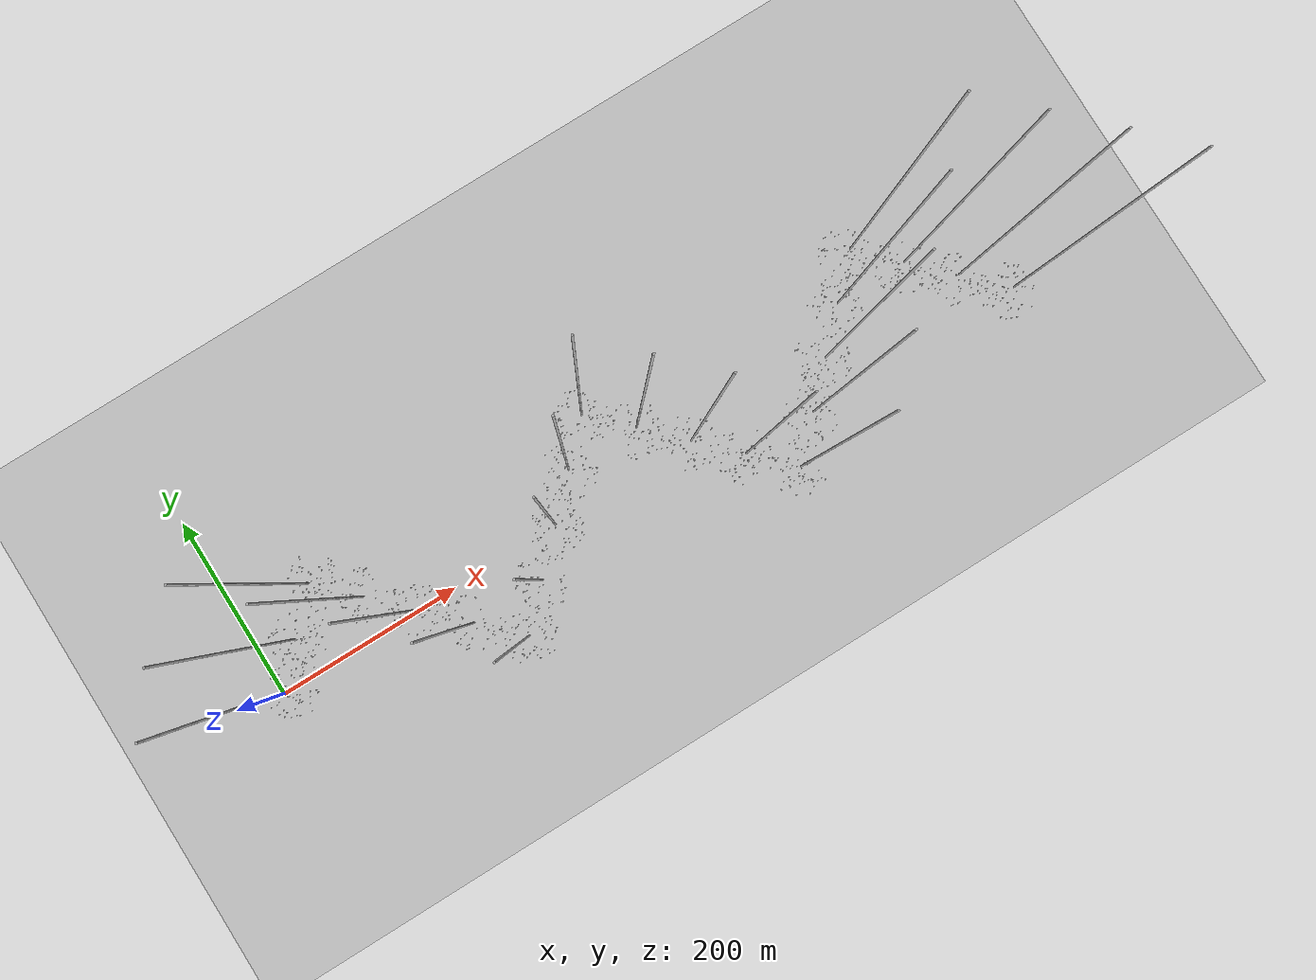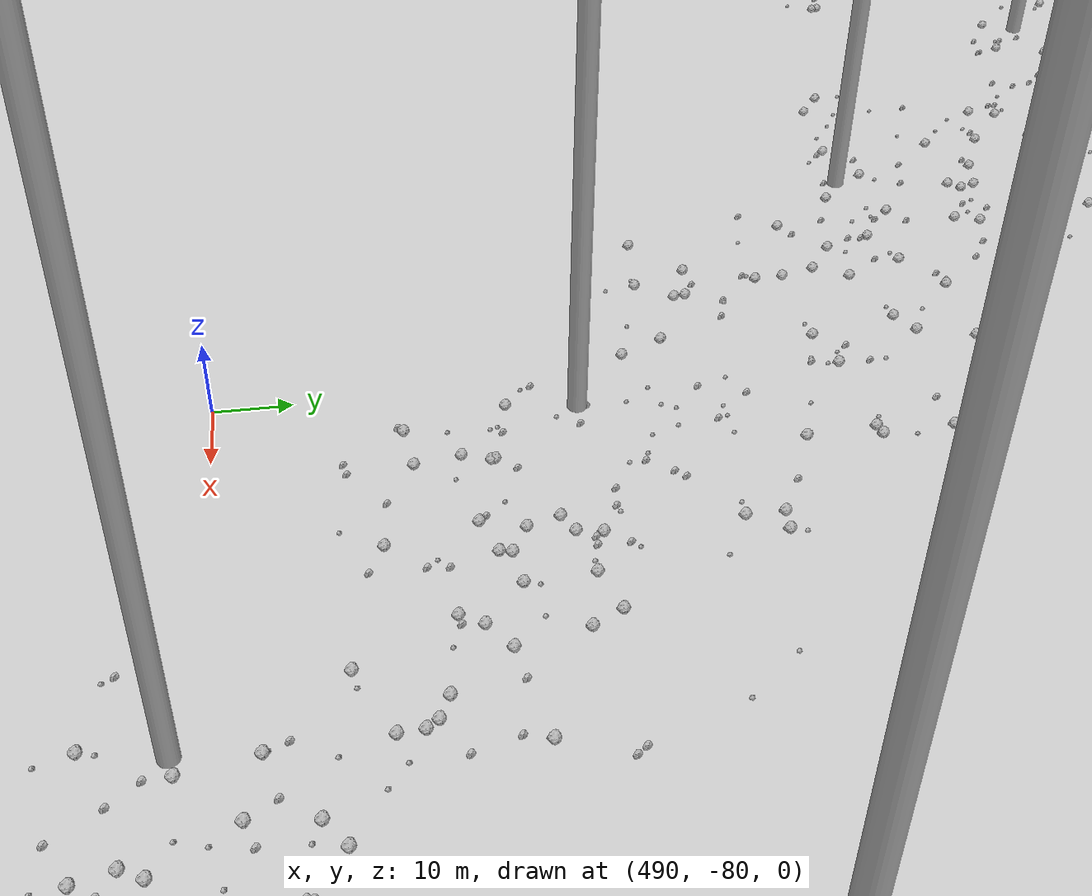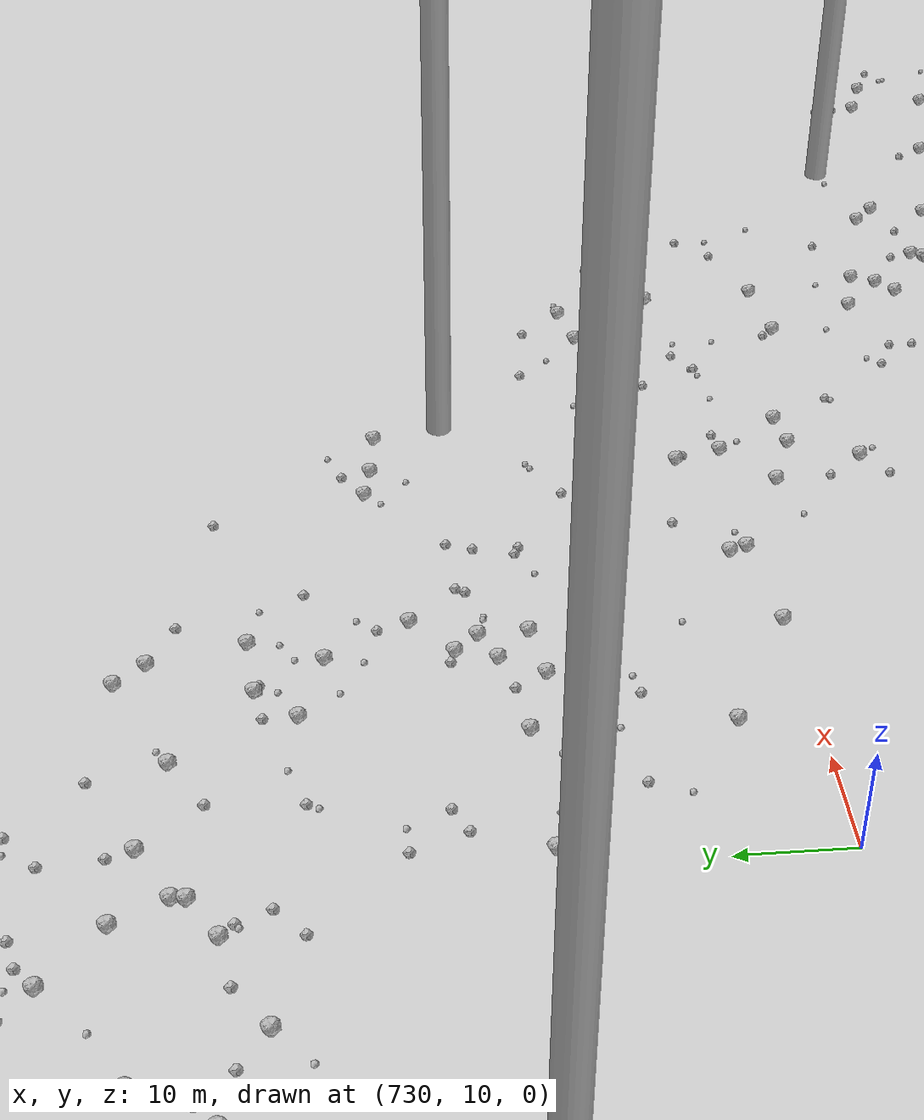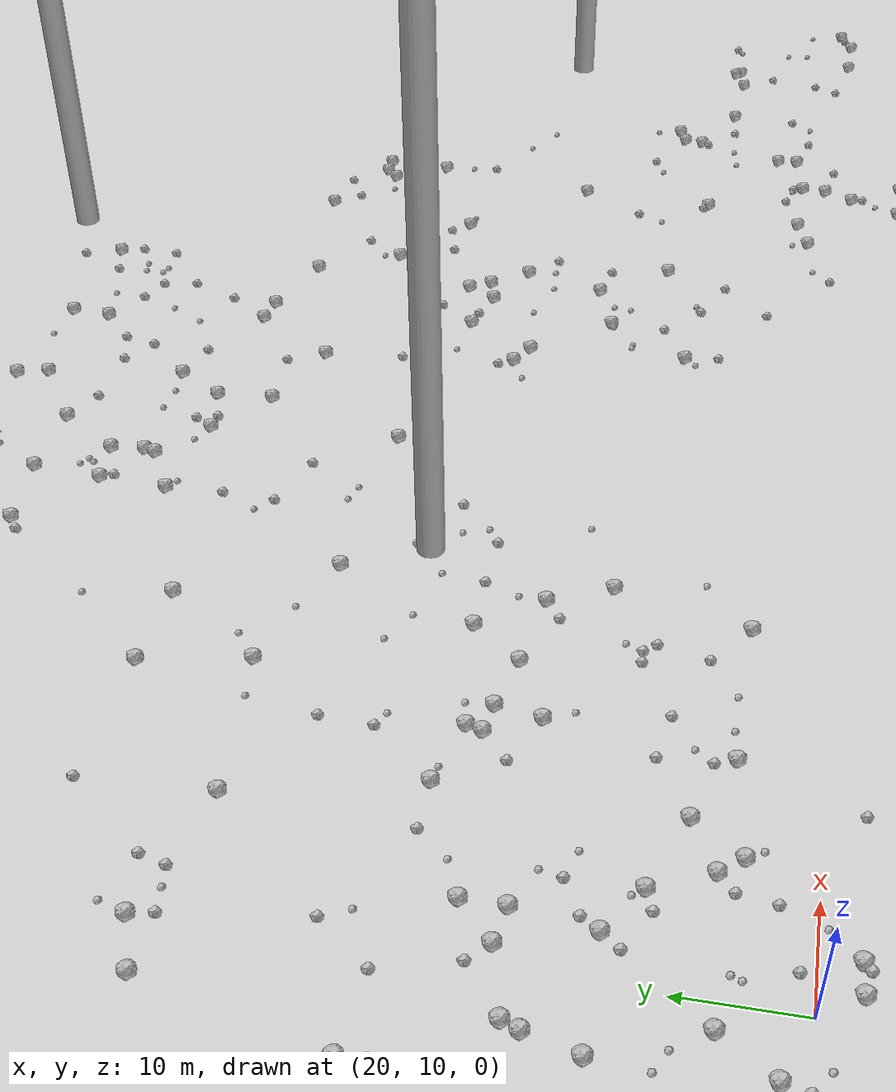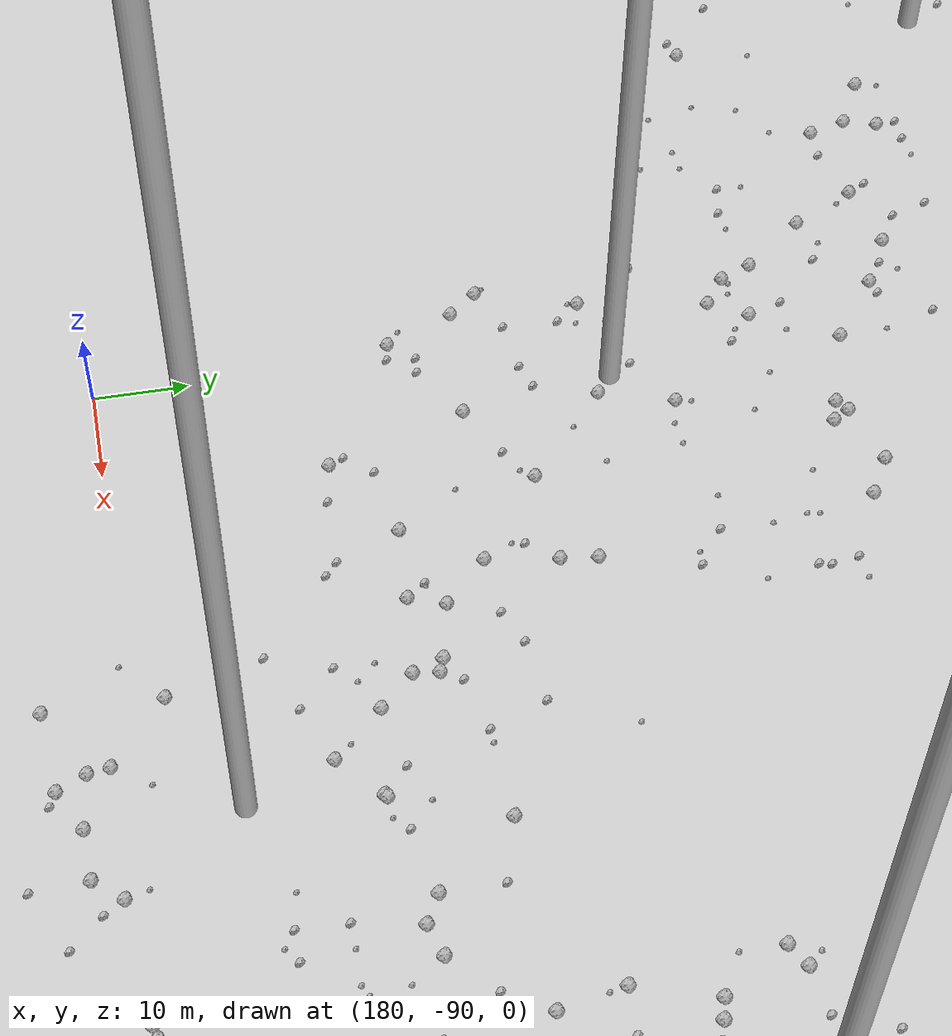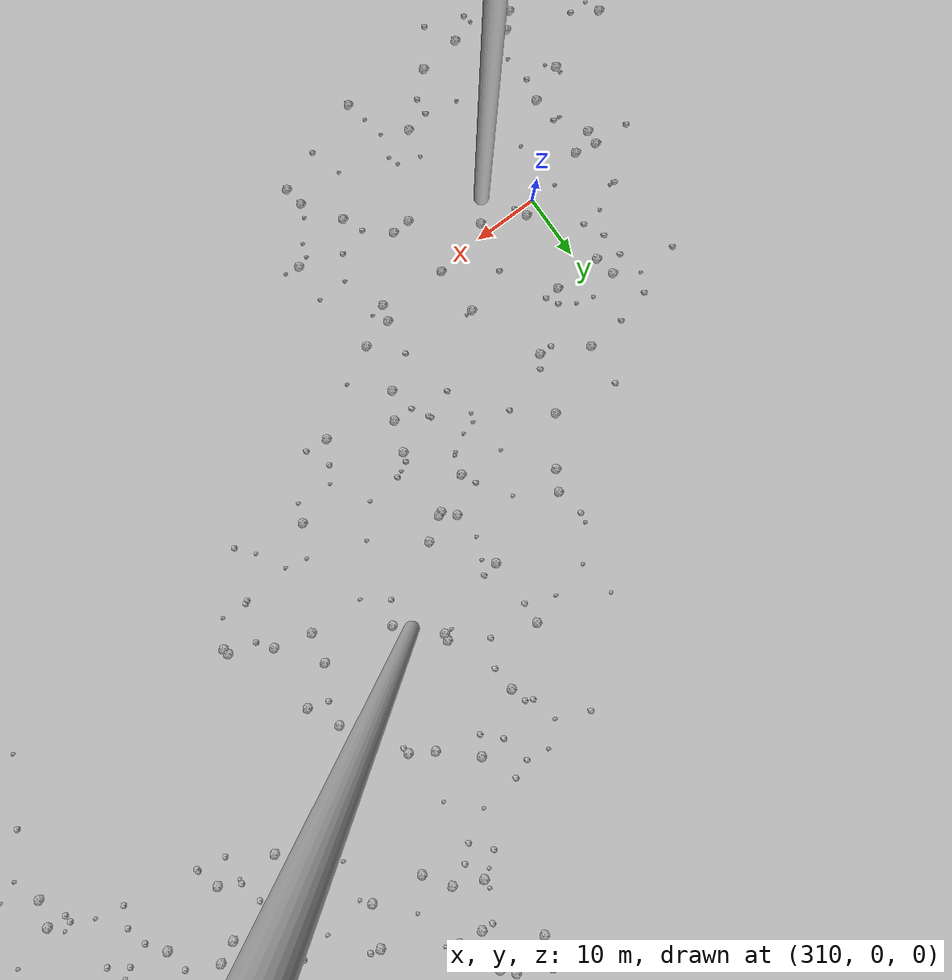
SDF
<sdf version="1.6">
 <world name="default">
  <include><uri>model://custom_ground</uri></include>
  <include><uri>model://sun</uri></include>
  <spherical_coordinates>
   <surface_model>EARTH_WGS84</surface_model>
   <latitude_deg>38.161479</latitude_deg>
   <longitude_deg>-122.454630</longitude_deg>
   <elevation>488.0</elevation>
   <heading_deg>90</heading_deg>
  </spherical_coordinates>
  <model name="rock1_0_0">
   <include><uri>model://rock1</uri><pose>29.059063461837425 -16.462699022643832 0.5 0 0 0</pose></include>
  </model>
  <model name="rock1_0_1">
   <include><uri>model://rock1</uri><pose>31.089119189638232 17.47931736922417 0.5 0 0 0</pose></include>
  </model>
  <model name="rock1_0_2">
   <include><uri>model://rock1</uri><pose>4.420348112582573 19.430249538574195 0.5 0 0 0</pose></include>
  </model>
  <model name="rock1_0_3">
   <include><uri>model://rock1</uri><pose>1.8487295856868222 -27.171056192955714 0.5 0 0 0</pose></include>
  </model>
  <model name="rock1_0_4">
   <include><uri>model://rock1</uri><pose>3.710402980066796 5.883594964835176 0.5 0 0 0</pose></include>
  </model>
  <model name="rock1_0_5">
   <include><uri>model://rock1</uri><pose>22.31363023445499 6.829210135725411 0.5 0 0 0</pose></include>
  </model>
  <model name="rock1_0_6">
   <include><uri>model://rock1</uri><pose>23.840737223351006 1.7832460847529106 0.5 0 0 0</pose></include>
  </model>
  <model name="rock1_0_7">
   <include><uri>model://rock1</uri><pose>26.24897104157845 3.185752703556574 0.5 0 0 0</pose></include>
  </model>
  <model name="rock1_0_8">
   <include><uri>model://rock1</uri><pose>-11.943861887500924 -19.983453683427662 0.5 0 0 0</pose></include>
  </model>
  <model name="rock1_0_9">
   <include><uri>model://rock1</uri><pose>7.242347670424227 1.1409997131137715 0.5 0 0 0</pose></include>
  </model>
  <model name="rock1_0_10">
   <include><uri>model://rock1</uri><pose>17.747404276811224 16.681608058786153 0.5 0 0 0</pose></include>
  </model>
  <model name="rock1_0_11">
   <include><uri>model://rock1</uri><pose>17.015834010433544 -21.717289930792354 0.5 0 0 0</pose></include>
  </model>
  <model name="rock1_0_12">
   <include><uri>model://rock1</uri><pose>9.847956789815505 -13.349562966110437 0.5 0 0 0</pose></include>
  </model>
  <model name="rock1_0_13">
   <include><uri>model://rock1</uri><pose>-9.33347560698663 -4.4387042215465335 0.5 0 0 0</pose></include>
  </model>
  <model name="rock1_0_14">
   <include><uri>model://rock1</uri><pose>-9.212783495404677 -13.740995031278803 0.5 0 0 0</pose></include>
  </model>
  <model name="rock1_0_15">
   <include><uri>model://rock1</uri><pose>1.3712645872022868 -4.4377695922704135 0.5 0 0 0</pose></include>
  </model>
  <model name="rock1_0_16">
   <include><uri>model://rock1</uri><pose>15.439551142951608 29.379708416784666 0.5 0 0 0</pose></include>
  </model>
  <model name="rock1_0_17">
   <include><uri>model://rock1</uri><pose>-18.348130232160976 4.746335159639955 0.5 0 0 0</pose></include>
  </model>
  <model name="rock1_0_18">
   <include><uri>model://rock1</uri><pose>14.473351402151692 -29.37377166498147 0.5 0 0 0</pose></include>
  </model>
  <model name="rock1_0_19">
   <include><uri>model://rock1</uri><pose>2.8325222322293975 6.088778664497752 0.5 0 0 0</pose></include>
  </model>
  <model name="rock1_0_20">
   <include><uri>model://rock1</uri><pose>4.9775000413560555 -7.882458926117838 0.5 0 0 0</pose></include>
  </model>
  <model name="rock1_0_21">
   <include><uri>model://rock1</uri><pose>14.206485260796285 25.009208192036155 0.5 0 0 0</pose></include>
  </model>
  <model name="rock1_0_22">
   <include><uri>model://rock1</uri><pose>14.617322873562046 12.223473128417567 0.5 0 0 0</pose></include>
  </model>
  <model name="rock1_0_23">
   <include><uri>model://rock1</uri><pose>10.581508734123013 3.1255079263052394 0.5 0 0 0</pose></include>
  </model>
  <model name="rock1_0_24">
   <include><uri>model://rock1</uri><pose>-15.23246195285207 -15.073760405289233 0.5 0 0 0</pose></include>
  </model>
  <model name="rock1_0_25">
   <include><uri>model://rock1</uri><pose>25.064511754472854 6.985243052871567 0.5 0 0 0</pose></include>
  </model>
  <model name="rock1_0_26">
   <include><uri>model://rock1</uri><pose>28.85140141515216 -13.433298885274997 0.5 0 0 0</pose></include>
  </model>
  <model name="rock2_0_0">
   <include><uri>model://rock2</uri><pose>24.363031763717984 6.3808704338235245 0.3 0 0 0</pose></include>
  </model>
  <model name="rock2_0_1">
   <include><uri>model://rock2</uri><pose>23.38427565199906 11.246991646517145 0.3 0 0 0</pose></include>
  </model>
  <model name="rock2_0_2">
   <include><uri>model://rock2</uri><pose>19.88808058510164 -16.216910463073106 0.3 0 0 0</pose></include>
  </model>
  <model name="rock2_0_3">
   <include><uri>model://rock2</uri><pose>8.539088701713823 -15.550422255641106 0.3 0 0 0</pose></include>
  </model>
  <model name="rock2_0_4">
   <include><uri>model://rock2</uri><pose>14.090621273524825 10.143477939732847 0.3 0 0 0</pose></include>
  </model>
  <model name="rock2_0_5">
   <include><uri>model://rock2</uri><pose>-19.073264352103724 -4.838616449588535 0.3 0 0 0</pose></include>
  </model>
  <model name="rock2_0_6">
   <include><uri>model://rock2</uri><pose>4.172494530581762 25.272423098809547 0.3 0 0 0</pose></include>
  </model>
  <model name="rock2_0_7">
   <include><uri>model://rock2</uri><pose>-6.725809600205466 -23.751025758789158 0.3 0 0 0</pose></include>
  </model>
  <model name="rock2_0_8">
   <include><uri>model://rock2</uri><pose>13.350696959432149 3.1046393661080316 0.3 0 0 0</pose></include>
  </model>
  <model name="rock2_0_9">
   <include><uri>model://rock2</uri><pose>-2.37008758760917 19.377249520785817 0.3 0 0 0</pose></include>
  </model>
  <model name="rock2_0_10">
   <include><uri>model://rock2</uri><pose>12.240065171645483 -9.228333097137057 0.3 0 0 0</pose></include>
  </model>
  <model name="rock2_0_11">
   <include><uri>model://rock2</uri><pose>10.973295370383351 -16.231222099024833 0.3 0 0 0</pose></include>
  </model>
  <model name="rock2_0_12">
   <include><uri>model://rock2</uri><pose>-7.921361068796159 -17.39381523775994 0.3 0 0 0</pose></include>
  </model>
  <model name="rock2_0_13">
   <include><uri>model://rock2</uri><pose>7.877449373799411 24.830635693596243 0.3 0 0 0</pose></include>
  </model>
  <model name="rock2_0_14">
   <include><uri>model://rock2</uri><pose>29.408936433607856 16.04507847560029 0.3 0 0 0</pose></include>
  </model>
  <model name="rock2_0_15">
   <include><uri>model://rock2</uri><pose>34.888653293776336 4.231139722465201 0.3 0 0 0</pose></include>
  </model>
  <model name="rock2_0_16">
   <include><uri>model://rock2</uri><pose>23.089597286585338 23.560352084132134 0.3 0 0 0</pose></include>
  </model>
  <model name="rock2_0_17">
   <include><uri>model://rock2</uri><pose>-4.919197279808078 20.774983271151584 0.3 0 0 0</pose></include>
  </model>
  <model name="rock2_0_18">
   <include><uri>model://rock2</uri><pose>27.08787757607184 1.6877094718921626 0.3 0 0 0</pose></include>
  </model>
  <model name="rock2_0_19">
   <include><uri>model://rock2</uri><pose>-0.936183451437703 -24.73164447259543 0.3 0 0 0</pose></include>
  </model>
  <model name="rock2_0_20">
   <include><uri>model://rock2</uri><pose>9.640628504845829 -15.924617782497975 0.3 0 0 0</pose></include>
  </model>
  <model name="rock2_0_21">
   <include><uri>model://rock2</uri><pose>0.6779966300929132 -18.59264329067997 0.3 0 0 0</pose></include>
  </model>
  <model name="rock2_0_22">
   <include><uri>model://rock2</uri><pose>-9.622307605148597 -3.9217907868616138 0.3 0 0 0</pose></include>
  </model>
  <model name="rock2_0_23">
   <include><uri>model://rock2</uri><pose>-3.719075723429281 19.749213069380836 0.3 0 0 0</pose></include>
  </model>
  <model name="rock2_0_24">
   <include><uri>model://rock2</uri><pose>2.131725640403232 -5.220415735167769 0.3 0 0 0</pose></include>
  </model>
  <model name="rock2_0_25">
   <include><uri>model://rock2</uri><pose>0.9247041682114556 -18.30331851750315 0.3 0 0 0</pose></include>
  </model>
  <model name="rock2_0_26">
   <include><uri>model://rock2</uri><pose>38.29036251289214 6.845331668849681 0.3 0 0 0</pose></include>
  </model>
  <model name="rock3_0_0">
   <include><uri>model://rock3</uri><pose>22.347307419028922 15.879065498094292 0.2 0 0 0</pose></include>
  </model>
  <model name="rock3_0_1">
   <include><uri>model://rock3</uri><pose>23.187783085456523 -11.404438802656028 0.2 0 0 0</pose></include>
  </model>
  <model name="rock3_0_2">
   <include><uri>model://rock3</uri><pose>9.675477758764806 -7.147465325530614 0.2 0 0 0</pose></include>
  </model>
  <model name="rock3_0_3">
   <include><uri>model://rock3</uri><pose>13.503300342796962 -20.56095196759923 0.2 0 0 0</pose></include>
  </model>
  <model name="rock3_0_4">
   <include><uri>model://rock3</uri><pose>5.614300630042198 -7.51786337604662 0.2 0 0 0</pose></include>
  </model>
  <model name="rock3_0_5">
   <include><uri>model://rock3</uri><pose>-9.133794736026712 0.22602313132039953 0.2 0 0 0</pose></include>
  </model>
  <model name="rock3_0_6">
   <include><uri>model://rock3</uri><pose>22.01020141520906 15.048910327240819 0.2 0 0 0</pose></include>
  </model>
  <model name="rock3_0_7">
   <include><uri>model://rock3</uri><pose>26.936928256466487 -23.42193254433988 0.2 0 0 0</pose></include>
  </model>
  <model name="rock3_0_8">
   <include><uri>model://rock3</uri><pose>2.738829809984786 14.683381202929837 0.2 0 0 0</pose></include>
  </model>
  <model name="rock3_0_9">
   <include><uri>model://rock3</uri><pose>16.70277939576085 -4.585411613491065 0.2 0 0 0</pose></include>
  </model>
  <model name="rock3_0_10">
   <include><uri>model://rock3</uri><pose>-9.127446461355131 -7.390728999188433 0.2 0 0 0</pose></include>
  </model>
  <model name="rock3_0_11">
   <include><uri>model://rock3</uri><pose>5.0777686300056715 5.782744277955359 0.2 0 0 0</pose></include>
  </model>
  <model name="rock3_0_12">
   <include><uri>model://rock3</uri><pose>33.66579509480375 14.128463958294077 0.2 0 0 0</pose></include>
  </model>
  <model name="rock3_0_13">
   <include><uri>model://rock3</uri><pose>15.707378301049673 19.44683218265734 0.2 0 0 0</pose></include>
  </model>
  <model name="rock3_0_14">
   <include><uri>model://rock3</uri><pose>35.05034899748857 -5.141775120692657 0.2 0 0 0</pose></include>
  </model>
  <model name="rock3_0_15">
   <include><uri>model://rock3</uri><pose>3.129782267223309 12.143266023885246 0.2 0 0 0</pose></include>
  </model>
  <model name="rock3_0_16">
   <include><uri>model://rock3</uri><pose>27.432908337867467 9.339636402889084 0.2 0 0 0</pose></include>
  </model>
  <model name="rock3_0_17">
   <include><uri>model://rock3</uri><pose>-12.50360436053417 -6.044801351841144 0.2 0 0 0</pose></include>
  </model>
  <model name="rock3_0_18">
   <include><uri>model://rock3</uri><pose>15.965992602569202 8.770658317574686 0.2 0 0 0</pose></include>
  </model>
  <model name="rock3_0_19">
   <include><uri>model://rock3</uri><pose>22.394559546873303 -12.108647833751569 0.2 0 0 0</pose></include>
  </model>
  <model name="rock3_0_20">
   <include><uri>model://rock3</uri><pose>-10.782337247444087 7.180273459891289 0.2 0 0 0</pose></include>
  </model>
  <model name="rock3_0_21">
   <include><uri>model://rock3</uri><pose>12.514338929527781 -20.95178479881934 0.2 0 0 0</pose></include>
  </model>
  <model name="rock3_0_22">
   <include><uri>model://rock3</uri><pose>6.235535572090985 -11.798988322531322 0.2 0 0 0</pose></include>
  </model>
  <model name="rock3_0_23">
   <include><uri>model://rock3</uri><pose>27.956466096827185 23.312636130097566 0.2 0 0 0</pose></include>
  </model>
  <model name="rock3_0_24">
   <include><uri>model://rock3</uri><pose>7.2122436283047975 -15.771266024305392 0.2 0 0 0</pose></include>
  </model>
  <model name="rock3_0_25">
   <include><uri>model://rock3</uri><pose>13.844563392820334 20.37819343996354 0.2 0 0 0</pose></include>
  </model>
  <model name="rock3_0_26">
   <include><uri>model://rock3</uri><pose>-15.396098061516188 9.970030827256487 0.2 0 0 0</pose></include>
  </model>
  <model name="rock1_1_0">
   <include><uri>model://rock1</uri><pose>50.37438476636102 35.12007920774259 0.5 0 0 0</pose></include>
  </model>
  <model name="rock1_1_1">
   <include><uri>model://rock1</uri><pose>11.301421943001895 40.999397663169525 0.5 0 0 0</pose></include>
  </model>
  <model name="rock1_1_2">
   <include><uri>model://rock1</uri><pose>44.15251315426354 32.23310955666062 0.5 0 0 0</pose></include>
  </model>
  <model name="rock1_1_3">
   <include><uri>model://rock1</uri><pose>59.49255629830463 52.48868494269871 0.5 0 0 0</pose></include>
  </model>
  <model name="rock1_1_4">
   <include><uri>model://rock1</uri><pose>19.935248914834123 58.27365048285641 0.5 0 0 0</pose></include>
  </model>
  <model name="rock1_1_5">
   <include><uri>model://rock1</uri><pose>53.48373795356073 65.8058244867168 0.5 0 0 0</pose></include>
  </model>
  <model name="rock1_1_6">
   <include><uri>model://rock1</uri><pose>28.74563469787844 22.423971936546163 0.5 0 0 0</pose></include>
  </model>
  <model name="rock1_1_7">
   <include><uri>model://rock1</uri><pose>25.476363413511898 35.4727031647047 0.5 0 0 0</pose></include>
  </model>
  <model name="rock1_1_8">
   <include><uri>model://rock1</uri><pose>35.92418427521547 19.850375926358197 0.5 0 0 0</pose></include>
  </model>
  <model name="rock1_1_9">
   <include><uri>model://rock1</uri><pose>46.75886629390459 56.729225121212764 0.5 0 0 0</pose></include>
  </model>
  <model name="rock1_1_10">
   <include><uri>model://rock1</uri><pose>41.962014428600206 36.69741631125392 0.5 0 0 0</pose></include>
  </model>
  <model name="rock1_1_11">
   <include><uri>model://rock1</uri><pose>16.046575935749523 30.8147430460972 0.5 0 0 0</pose></include>
  </model>
  <model name="rock1_1_12">
   <include><uri>model://rock1</uri><pose>22.071951627836942 32.399003725941306 0.5 0 0 0</pose></include>
  </model>
  <model name="rock1_1_13">
   <include><uri>model://rock1</uri><pose>60.690710359745445 28.510810830326136 0.5 0 0 0</pose></include>
  </model>
  <model name="rock1_1_14">
   <include><uri>model://rock1</uri><pose>25.423307145455837 31.860523341487596 0.5 0 0 0</pose></include>
  </model>
  <model name="rock1_1_15">
   <include><uri>model://rock1</uri><pose>58.089522959979554 34.04750190757356 0.5 0 0 0</pose></include>
  </model>
  <model name="rock1_1_16">
   <include><uri>model://rock1</uri><pose>42.40179965683329 38.08136748265423 0.5 0 0 0</pose></include>
  </model>
  <model name="rock1_1_17">
   <include><uri>model://rock1</uri><pose>57.51304584722556 16.52582507640098 0.5 0 0 0</pose></include>
  </model>
  <model name="rock1_1_18">
   <include><uri>model://rock1</uri><pose>32.764866691569694 15.553193184981506 0.5 0 0 0</pose></include>
  </model>
  <model name="rock1_1_19">
   <include><uri>model://rock1</uri><pose>24.39173336701764 25.16644157435818 0.5 0 0 0</pose></include>
  </model>
  <model name="rock1_1_20">
   <include><uri>model://rock1</uri><pose>32.231756880859045 55.302765032081666 0.5 0 0 0</pose></include>
  </model>
  <model name="rock1_1_21">
   <include><uri>model://rock1</uri><pose>54.00008122979492 39.60419835709769 0.5 0 0 0</pose></include>
  </model>
  <model name="rock1_1_22">
   <include><uri>model://rock1</uri><pose>42.4284021370872 16.78251241693343 0.5 0 0 0</pose></include>
  </model>
  <model name="rock1_1_23">
   <include><uri>model://rock1</uri><pose>15.28430288948126 56.52994554284955 0.5 0 0 0</pose></include>
  </model>
  <model name="rock1_1_24">
   <include><uri>model://rock1</uri><pose>36.10051391536938 39.64087977671494 0.5 0 0 0</pose></include>
  </model>
  <model name="rock1_1_25">
   <include><uri>model://rock1</uri><pose>44.94312193140853 36.26650865825415 0.5 0 0 0</pose></include>
  </model>
  <model name="rock1_1_26">
   <include><uri>model://rock1</uri><pose>44.89080601732622 66.21040905318642 0.5 0 0 0</pose></include>
  </model>
  <model name="rock2_1_0">
   <include><uri>model://rock2</uri><pose>51.895127502079006 25.17431630030475 0.3 0 0 0</pose></include>
  </model>
  <model name="rock2_1_1">
   <include><uri>model://rock2</uri><pose>25.43962307544345 26.714296273449392 0.3 0 0 0</pose></include>
  </model>
  <model name="rock2_1_2">
   <include><uri>model://rock2</uri><pose>55.93168094042724 32.5962089073911 0.3 0 0 0</pose></include>
  </model>
  <model name="rock2_1_3">
   <include><uri>model://rock2</uri><pose>24.608143229067124 56.89776969676234 0.3 0 0 0</pose></include>
  </model>
  <model name="rock2_1_4">
   <include><uri>model://rock2</uri><pose>25.295223113820253 59.2231041012314 0.3 0 0 0</pose></include>
  </model>
  <model name="rock2_1_5">
   <include><uri>model://rock2</uri><pose>26.760523482922775 21.679577198270863 0.3 0 0 0</pose></include>
  </model>
  <model name="rock2_1_6">
   <include><uri>model://rock2</uri><pose>22.07048202707818 44.91441668131586 0.3 0 0 0</pose></include>
  </model>
  <model name="rock2_1_7">
   <include><uri>model://rock2</uri><pose>41.51676655935491 22.959666383491488 0.3 0 0 0</pose></include>
  </model>
  <model name="rock2_1_8">
   <include><uri>model://rock2</uri><pose>64.83308451309274 39.426195333474354 0.3 0 0 0</pose></include>
  </model>
  <model name="rock2_1_9">
   <include><uri>model://rock2</uri><pose>53.249348194751725 25.24882991935995 0.3 0 0 0</pose></include>
  </model>
  <model name="rock2_1_10">
   <include><uri>model://rock2</uri><pose>53.11066445900259 19.647959728101288 0.3 0 0 0</pose></include>
  </model>
  <model name="rock2_1_11">
   <include><uri>model://rock2</uri><pose>59.44248825816731 39.59031048972372 0.3 0 0 0</pose></include>
  </model>
  <model name="rock2_1_12">
   <include><uri>model://rock2</uri><pose>69.66130633472088 43.44214725876453 0.3 0 0 0</pose></include>
  </model>
  <model name="rock2_1_13">
   <include><uri>model://rock2</uri><pose>41.006677017872335 45.202146751557436 0.3 0 0 0</pose></include>
  </model>
  <model name="rock2_1_14">
   <include><uri>model://rock2</uri><pose>63.519618415996135 46.4036555926973 0.3 0 0 0</pose></include>
  </model>
  <model name="rock2_1_15">
   <include><uri>model://rock2</uri><pose>28.89706192815915 12.912933895581373 0.3 0 0 0</pose></include>
  </model>
  <model name="rock2_1_16">
   <include><uri>model://rock2</uri><pose>31.60887602288596 66.63427832075041 0.3 0 0 0</pose></include>
  </model>
  <model name="rock2_1_17">
   <include><uri>model://rock2</uri><pose>28.608602423538056 28.34411736140709 0.3 0 0 0</pose></include>
  </model>
  <model name="rock2_1_18">
   <include><uri>model://rock2</uri><pose>18.404845967130093 40.380889945757716 0.3 0 0 0</pose></include>
  </model>
  <model name="rock2_1_19">
   <include><uri>model://rock2</uri><pose>20.36528721411976 56.27730803245191 0.3 0 0 0</pose></include>
  </model>
  <model name="rock2_1_20">
   <include><uri>model://rock2</uri><pose>20.24142747094592 34.026921078853995 0.3 0 0 0</pose></include>
  </model>
  <model name="rock2_1_21">
   <include><uri>model://rock2</uri><pose>54.21173838492262 24.141142616665924 0.3 0 0 0</pose></include>
  </model>
  <model name="rock2_1_22">
   <include><uri>model://rock2</uri><pose>39.15196477500251 34.286721316533985 0.3 0 0 0</pose></include>
  </model>
  <model name="rock2_1_23">
   <include><uri>model://rock2</uri><pose>41.69607841281105 18.496971667394728 0.3 0 0 0</pose></include>
  </model>
  <model name="rock2_1_24">
   <include><uri>model://rock2</uri><pose>31.21407889218019 39.66534670042988 0.3 0 0 0</pose></include>
  </model>
  <model name="rock2_1_25">
   <include><uri>model://rock2</uri><pose>46.17085877689709 22.184004169173736 0.3 0 0 0</pose></include>
  </model>
  <model name="rock2_1_26">
   <include><uri>model://rock2</uri><pose>41.30158062026526 49.868431599567856 0.3 0 0 0</pose></include>
  </model>
  <model name="rock3_1_0">
   <include><uri>model://rock3</uri><pose>53.956610251247334 26.69743345890523 0.2 0 0 0</pose></include>
  </model>
  <model name="rock3_1_1">
   <include><uri>model://rock3</uri><pose>49.31648132605225 17.085055967652792 0.2 0 0 0</pose></include>
  </model>
  <model name="rock3_1_2">
   <include><uri>model://rock3</uri><pose>11.723033836672148 38.83129916987485 0.2 0 0 0</pose></include>
  </model>
  <model name="rock3_1_3">
   <include><uri>model://rock3</uri><pose>49.474559678433025 58.7902674637091 0.2 0 0 0</pose></include>
  </model>
  <model name="rock3_1_4">
   <include><uri>model://rock3</uri><pose>53.509267063115196 54.93495106009519 0.2 0 0 0</pose></include>
  </model>
  <model name="rock3_1_5">
   <include><uri>model://rock3</uri><pose>58.19043680794841 36.422382271238284 0.2 0 0 0</pose></include>
  </model>
  <model name="rock3_1_6">
   <include><uri>model://rock3</uri><pose>45.27249413303977 29.709561607465986 0.2 0 0 0</pose></include>
  </model>
  <model name="rock3_1_7">
   <include><uri>model://rock3</uri><pose>50.95275382924881 46.63955644071519 0.2 0 0 0</pose></include>
  </model>
  <model name="rock3_1_8">
   <include><uri>model://rock3</uri><pose>59.98152946928035 43.49543967573454 0.2 0 0 0</pose></include>
  </model>
  <model name="rock3_1_9">
   <include><uri>model://rock3</uri><pose>23.19655057948855 42.608884738440125 0.2 0 0 0</pose></include>
  </model>
  <model name="rock3_1_10">
   <include><uri>model://rock3</uri><pose>28.833831253633637 36.87134728932397 0.2 0 0 0</pose></include>
  </model>
  <model name="rock3_1_11">
   <include><uri>model://rock3</uri><pose>22.643804338454423 56.538357731437905 0.2 0 0 0</pose></include>
  </model>
  <model name="rock3_1_12">
   <include><uri>model://rock3</uri><pose>42.41011703746012 56.15197606929804 0.2 0 0 0</pose></include>
  </model>
  <model name="rock3_1_13">
   <include><uri>model://rock3</uri><pose>62.40778101296422 20.637875095955767 0.2 0 0 0</pose></include>
  </model>
  <model name="rock3_1_14">
   <include><uri>model://rock3</uri><pose>45.467467574711755 17.085667069630112 0.2 0 0 0</pose></include>
  </model>
  <model name="rock3_1_15">
   <include><uri>model://rock3</uri><pose>29.076524507232723 30.194603319880883 0.2 0 0 0</pose></include>
  </model>
  <model name="rock3_1_16">
   <include><uri>model://rock3</uri><pose>20.7111154618094 60.650132051649905 0.2 0 0 0</pose></include>
  </model>
  <model name="rock3_1_17">
   <include><uri>model://rock3</uri><pose>44.80909626812217 38.595687102567005 0.2 0 0 0</pose></include>
  </model>
  <model name="rock3_1_18">
   <include><uri>model://rock3</uri><pose>54.261029869037905 44.879063565351046 0.2 0 0 0</pose></include>
  </model>
  <model name="rock3_1_19">
   <include><uri>model://rock3</uri><pose>42.52050642609739 44.46969612610121 0.2 0 0 0</pose></include>
  </model>
  <model name="rock3_1_20">
   <include><uri>model://rock3</uri><pose>47.11401446264053 57.09508164809985 0.2 0 0 0</pose></include>
  </model>
  <model name="rock3_1_21">
   <include><uri>model://rock3</uri><pose>31.3054149542184 27.533256124835674 0.2 0 0 0</pose></include>
  </model>
  <model name="rock3_1_22">
   <include><uri>model://rock3</uri><pose>65.7813721622297 42.776568123050275 0.2 0 0 0</pose></include>
  </model>
  <model name="rock3_1_23">
   <include><uri>model://rock3</uri><pose>68.35436726552749 31.45913389205425 0.2 0 0 0</pose></include>
  </model>
  <model name="rock3_1_24">
   <include><uri>model://rock3</uri><pose>37.6406217625308 39.32377163007743 0.2 0 0 0</pose></include>
  </model>
  <model name="rock3_1_25">
   <include><uri>model://rock3</uri><pose>42.95069475642418 20.021118693752822 0.2 0 0 0</pose></include>
  </model>
  <model name="rock3_1_26">
   <include><uri>model://rock3</uri><pose>66.65011402538734 40.461105247703046 0.2 0 0 0</pose></include>
  </model>
  <model name="rock1_2_0">
   <include><uri>model://rock1</uri><pose>67.73830718485885 77.62833687520589 0.5 0 0 0</pose></include>
  </model>
  <model name="rock1_2_1">
   <include><uri>model://rock1</uri><pose>107.70245109146437 89.60065902142544 0.5 0 0 0</pose></include>
  </model>
  <model name="rock1_2_2">
   <include><uri>model://rock1</uri><pose>60.63241765455979 83.4577362500562 0.5 0 0 0</pose></include>
  </model>
  <model name="rock1_2_3">
   <include><uri>model://rock1</uri><pose>94.65796356092679 86.39942457327638 0.5 0 0 0</pose></include>
  </model>
  <model name="rock1_2_4">
   <include><uri>model://rock1</uri><pose>91.65053774621545 62.00306725481007 0.5 0 0 0</pose></include>
  </model>
  <model name="rock1_2_5">
   <include><uri>model://rock1</uri><pose>67.32725700417859 71.08249220970087 0.5 0 0 0</pose></include>
  </model>
  <model name="rock1_2_6">
   <include><uri>model://rock1</uri><pose>82.72541101314332 91.80602308743792 0.5 0 0 0</pose></include>
  </model>
  <model name="rock1_2_7">
   <include><uri>model://rock1</uri><pose>82.28880959906154 109.77841856834866 0.5 0 0 0</pose></include>
  </model>
  <model name="rock1_2_8">
   <include><uri>model://rock1</uri><pose>85.60953396674444 75.33856666934241 0.5 0 0 0</pose></include>
  </model>
  <model name="rock1_2_9">
   <include><uri>model://rock1</uri><pose>72.34516214393571 73.81023015308769 0.5 0 0 0</pose></include>
  </model>
  <model name="rock1_2_10">
   <include><uri>model://rock1</uri><pose>83.1080323598152 65.29272530103715 0.5 0 0 0</pose></include>
  </model>
  <model name="rock1_2_11">
   <include><uri>model://rock1</uri><pose>68.31419982687845 84.26939603026014 0.5 0 0 0</pose></include>
  </model>
  <model name="rock1_2_12">
   <include><uri>model://rock1</uri><pose>83.52802473562852 88.77170375794879 0.5 0 0 0</pose></include>
  </model>
  <model name="rock1_2_13">
   <include><uri>model://rock1</uri><pose>61.87934776923582 97.40874323455054 0.5 0 0 0</pose></include>
  </model>
  <model name="rock1_2_14">
   <include><uri>model://rock1</uri><pose>82.67167047182251 70.76030214945729 0.5 0 0 0</pose></include>
  </model>
  <model name="rock1_2_15">
   <include><uri>model://rock1</uri><pose>79.5417495417906 98.58160262873068 0.5 0 0 0</pose></include>
  </model>
  <model name="rock1_2_16">
   <include><uri>model://rock1</uri><pose>72.35447058669793 78.16125810130109 0.5 0 0 0</pose></include>
  </model>
  <model name="rock1_2_17">
   <include><uri>model://rock1</uri><pose>72.65144520720071 74.92619392328162 0.5 0 0 0</pose></include>
  </model>
  <model name="rock1_2_18">
   <include><uri>model://rock1</uri><pose>76.46714020939841 84.10690233350866 0.5 0 0 0</pose></include>
  </model>
  <model name="rock1_2_19">
   <include><uri>model://rock1</uri><pose>97.11109578601494 70.11983337671543 0.5 0 0 0</pose></include>
  </model>
  <model name="rock1_2_20">
   <include><uri>model://rock1</uri><pose>77.26302990569059 69.78376831410141 0.5 0 0 0</pose></include>
  </model>
  <model name="rock1_2_21">
   <include><uri>model://rock1</uri><pose>77.42041715377701 100.94490045420295 0.5 0 0 0</pose></include>
  </model>
  <model name="rock1_2_22">
   <include><uri>model://rock1</uri><pose>94.99449223720734 90.39784471731949 0.5 0 0 0</pose></include>
  </model>
  <model name="rock1_2_23">
   <include><uri>model://rock1</uri><pose>100.11369180716167 69.64959811838489 0.5 0 0 0</pose></include>
  </model>
  <model name="rock1_2_24">
   <include><uri>model://rock1</uri><pose>78.7652262086708 51.53859997576271 0.5 0 0 0</pose></include>
  </model>
  <model name="rock1_2_25">
   <include><uri>model://rock1</uri><pose>67.4478353949166 88.46890985964237 0.5 0 0 0</pose></include>
  </model>
  <model name="rock1_2_26">
   <include><uri>model://rock1</uri><pose>69.033109933742 102.27489024864408 0.5 0 0 0</pose></include>
  </model>
  <model name="rock2_2_0">
   <include><uri>model://rock2</uri><pose>108.13451709558846 83.39486802192734 0.3 0 0 0</pose></include>
  </model>
  <model name="rock2_2_1">
   <include><uri>model://rock2</uri><pose>73.30903355921748 58.63241909872704 0.3 0 0 0</pose></include>
  </model>
  <model name="rock2_2_2">
   <include><uri>model://rock2</uri><pose>108.37631448259452 87.20346453810967 0.3 0 0 0</pose></include>
  </model>
  <model name="rock2_2_3">
   <include><uri>model://rock2</uri><pose>68.26257286200665 76.46493436974643 0.3 0 0 0</pose></include>
  </model>
  <model name="rock2_2_4">
   <include><uri>model://rock2</uri><pose>67.52933996039137 65.68088629127581 0.3 0 0 0</pose></include>
  </model>
  <model name="rock2_2_5">
   <include><uri>model://rock2</uri><pose>72.28966389654231 97.54893695953294 0.3 0 0 0</pose></include>
  </model>
  <model name="rock2_2_6">
   <include><uri>model://rock2</uri><pose>106.40549799520522 93.32240142257943 0.3 0 0 0</pose></include>
  </model>
  <model name="rock2_2_7">
   <include><uri>model://rock2</uri><pose>87.0278532921088 82.05589389810794 0.3 0 0 0</pose></include>
  </model>
  <model name="rock2_2_8">
   <include><uri>model://rock2</uri><pose>101.7200956736259 82.64793212867832 0.3 0 0 0</pose></include>
  </model>
  <model name="rock2_2_9">
   <include><uri>model://rock2</uri><pose>72.73506737608466 90.0775505848425 0.3 0 0 0</pose></include>
  </model>
  <model name="rock2_2_10">
   <include><uri>model://rock2</uri><pose>98.75038962098066 83.91333675843958 0.3 0 0 0</pose></include>
  </model>
  <model name="rock2_2_11">
   <include><uri>model://rock2</uri><pose>80.2023304665464 82.33609870275893 0.3 0 0 0</pose></include>
  </model>
  <model name="rock2_2_12">
   <include><uri>model://rock2</uri><pose>90.93403063180098 83.17346483279537 0.3 0 0 0</pose></include>
  </model>
  <model name="rock2_2_13">
   <include><uri>model://rock2</uri><pose>59.09910333605859 82.46856127213721 0.3 0 0 0</pose></include>
  </model>
  <model name="rock2_2_14">
   <include><uri>model://rock2</uri><pose>92.42113561883139 54.147446848940206 0.3 0 0 0</pose></include>
  </model>
  <model name="rock2_2_15">
   <include><uri>model://rock2</uri><pose>90.08148729909493 74.0948515448051 0.3 0 0 0</pose></include>
  </model>
  <model name="rock2_2_16">
   <include><uri>model://rock2</uri><pose>71.81594770991626 105.75561316743172 0.3 0 0 0</pose></include>
  </model>
  <model name="rock2_2_17">
   <include><uri>model://rock2</uri><pose>100.23214817138452 74.3466873025221 0.3 0 0 0</pose></include>
  </model>
  <model name="rock2_2_18">
   <include><uri>model://rock2</uri><pose>89.8030347259322 65.59946601918907 0.3 0 0 0</pose></include>
  </model>
  <model name="rock2_2_19">
   <include><uri>model://rock2</uri><pose>79.01877827598867 69.66078087627695 0.3 0 0 0</pose></include>
  </model>
  <model name="rock2_2_20">
   <include><uri>model://rock2</uri><pose>90.10901903892204 79.89963444853298 0.3 0 0 0</pose></include>
  </model>
  <model name="rock2_2_21">
   <include><uri>model://rock2</uri><pose>76.9112211372726 95.75841599605818 0.3 0 0 0</pose></include>
  </model>
  <model name="rock2_2_22">
   <include><uri>model://rock2</uri><pose>78.4025031810132 71.63662710939768 0.3 0 0 0</pose></include>
  </model>
  <model name="rock2_2_23">
   <include><uri>model://rock2</uri><pose>102.35857194875092 79.1741079858822 0.3 0 0 0</pose></include>
  </model>
  <model name="rock2_2_24">
   <include><uri>model://rock2</uri><pose>103.86634780225549 88.58034754594121 0.3 0 0 0</pose></include>
  </model>
  <model name="rock2_2_25">
   <include><uri>model://rock2</uri><pose>86.46228751322178 101.00453070284904 0.3 0 0 0</pose></include>
  </model>
  <model name="rock2_2_26">
   <include><uri>model://rock2</uri><pose>67.27621596466551 60.69039608315695 0.3 0 0 0</pose></include>
  </model>
  <model name="rock3_2_0">
   <include><uri>model://rock3</uri><pose>68.43142527985852 70.33897904455362 0.2 0 0 0</pose></include>
  </model>
  <model name="rock3_2_1">
   <include><uri>model://rock3</uri><pose>70.3254128079769 79.62418849336512 0.2 0 0 0</pose></include>
  </model>
  <model name="rock3_2_2">
   <include><uri>model://rock3</uri><pose>79.53174930816914 75.3900990221908 0.2 0 0 0</pose></include>
  </model>
  <model name="rock3_2_3">
   <include><uri>model://rock3</uri><pose>82.48554660253205 75.08978896529675 0.2 0 0 0</pose></include>
  </model>
  <model name="rock3_2_4">
   <include><uri>model://rock3</uri><pose>67.5766734757013 94.34897108458661 0.2 0 0 0</pose></include>
  </model>
  <model name="rock3_2_5">
   <include><uri>model://rock3</uri><pose>88.37785376935956 102.852523827878 0.2 0 0 0</pose></include>
  </model>
  <model name="rock3_2_6">
   <include><uri>model://rock3</uri><pose>105.54740817123772 85.75455948047778 0.2 0 0 0</pose></include>
  </model>
  <model name="rock3_2_7">
   <include><uri>model://rock3</uri><pose>69.41662053538022 80.20299104986707 0.2 0 0 0</pose></include>
  </model>
  <model name="rock3_2_8">
   <include><uri>model://rock3</uri><pose>95.2707464120108 76.62016892955714 0.2 0 0 0</pose></include>
  </model>
  <model name="rock3_2_9">
   <include><uri>model://rock3</uri><pose>81.27253192688102 99.48271101641777 0.2 0 0 0</pose></include>
  </model>
  <model name="rock3_2_10">
   <include><uri>model://rock3</uri><pose>60.59314586937625 101.06799534750743 0.2 0 0 0</pose></include>
  </model>
  <model name="rock3_2_11">
   <include><uri>model://rock3</uri><pose>75.03111281884274 70.77563360624056 0.2 0 0 0</pose></include>
  </model>
  <model name="rock3_2_12">
   <include><uri>model://rock3</uri><pose>90.24792619659706 90.88612597119271 0.2 0 0 0</pose></include>
  </model>
  <model name="rock3_2_13">
   <include><uri>model://rock3</uri><pose>77.43218751841026 109.69485124868652 0.2 0 0 0</pose></include>
  </model>
  <model name="rock3_2_14">
   <include><uri>model://rock3</uri><pose>105.0262020297909 83.28721994779345 0.2 0 0 0</pose></include>
  </model>
  <model name="rock3_2_15">
   <include><uri>model://rock3</uri><pose>99.05226969461266 87.15759947114304 0.2 0 0 0</pose></include>
  </model>
  <model name="rock3_2_16">
   <include><uri>model://rock3</uri><pose>85.60603237039389 101.43356107705971 0.2 0 0 0</pose></include>
  </model>
  <model name="rock3_2_17">
   <include><uri>model://rock3</uri><pose>69.86722483724998 79.01174584308865 0.2 0 0 0</pose></include>
  </model>
  <model name="rock3_2_18">
   <include><uri>model://rock3</uri><pose>71.1268009222767 88.95439108091833 0.2 0 0 0</pose></include>
  </model>
  <model name="rock3_2_19">
   <include><uri>model://rock3</uri><pose>68.67249604219353 54.0654479484759 0.2 0 0 0</pose></include>
  </model>
  <model name="rock3_2_20">
   <include><uri>model://rock3</uri><pose>81.79594211909595 107.65811276692801 0.2 0 0 0</pose></include>
  </model>
  <model name="rock3_2_21">
   <include><uri>model://rock3</uri><pose>65.6834200898376 62.143787307656005 0.2 0 0 0</pose></include>
  </model>
  <model name="rock3_2_22">
   <include><uri>model://rock3</uri><pose>52.036030979616555 73.54265035487145 0.2 0 0 0</pose></include>
  </model>
  <model name="rock3_2_23">
   <include><uri>model://rock3</uri><pose>104.10743364841952 85.479529276213 0.2 0 0 0</pose></include>
  </model>
  <model name="rock3_2_24">
   <include><uri>model://rock3</uri><pose>97.234767071829 80.01175231196503 0.2 0 0 0</pose></include>
  </model>
  <model name="rock3_2_25">
   <include><uri>model://rock3</uri><pose>70.55642800340428 53.484957659497574 0.2 0 0 0</pose></include>
  </model>
  <model name="rock3_2_26">
   <include><uri>model://rock3</uri><pose>104.10006070934722 83.62743803104365 0.2 0 0 0</pose></include>
  </model>
  <model name="rock1_3_0">
   <include><uri>model://rock1</uri><pose>111.11279820671162 44.028768118318084 0.5 0 0 0</pose></include>
  </model>
  <model name="rock1_3_1">
   <include><uri>model://rock1</uri><pose>122.9110524406609 14.217034943919993 0.5 0 0 0</pose></include>
  </model>
  <model name="rock1_3_2">
   <include><uri>model://rock1</uri><pose>145.78319225052843 29.937542345200644 0.5 0 0 0</pose></include>
  </model>
  <model name="rock1_3_3">
   <include><uri>model://rock1</uri><pose>133.3606733247297 57.59734749094601 0.5 0 0 0</pose></include>
  </model>
  <model name="rock1_3_4">
   <include><uri>model://rock1</uri><pose>107.0240032048959 49.88372766352244 0.5 0 0 0</pose></include>
  </model>
  <model name="rock1_3_5">
   <include><uri>model://rock1</uri><pose>148.01381718261263 30.734687249652136 0.5 0 0 0</pose></include>
  </model>
  <model name="rock1_3_6">
   <include><uri>model://rock1</uri><pose>114.15614792568023 29.047431099759173 0.5 0 0 0</pose></include>
  </model>
  <model name="rock1_3_7">
   <include><uri>model://rock1</uri><pose>96.38362425219212 41.54504696445886 0.5 0 0 0</pose></include>
  </model>
  <model name="rock1_3_8">
   <include><uri>model://rock1</uri><pose>108.2535492680401 47.71098809861467 0.5 0 0 0</pose></include>
  </model>
  <model name="rock1_3_9">
   <include><uri>model://rock1</uri><pose>93.83591149728231 42.86943455211405 0.5 0 0 0</pose></include>
  </model>
  <model name="rock1_3_10">
   <include><uri>model://rock1</uri><pose>108.10235036633543 66.95447434503754 0.5 0 0 0</pose></include>
  </model>
  <model name="rock1_3_11">
   <include><uri>model://rock1</uri><pose>135.74571910300233 15.218562221193306 0.5 0 0 0</pose></include>
  </model>
  <model name="rock1_3_12">
   <include><uri>model://rock1</uri><pose>105.28257556454925 46.93259275802378 0.5 0 0 0</pose></include>
  </model>
  <model name="rock1_3_13">
   <include><uri>model://rock1</uri><pose>131.56811078227287 64.37913020733097 0.5 0 0 0</pose></include>
  </model>
  <model name="rock1_3_14">
   <include><uri>model://rock1</uri><pose>130.11752595334164 63.10044885627386 0.5 0 0 0</pose></include>
  </model>
  <model name="rock1_3_15">
   <include><uri>model://rock1</uri><pose>133.75020530834848 64.41271670313893 0.5 0 0 0</pose></include>
  </model>
  <model name="rock1_3_16">
   <include><uri>model://rock1</uri><pose>130.61396913270588 40.19372723492566 0.5 0 0 0</pose></include>
  </model>
  <model name="rock1_3_17">
   <include><uri>model://rock1</uri><pose>108.77222897113133 35.87509961699365 0.5 0 0 0</pose></include>
  </model>
  <model name="rock1_3_18">
   <include><uri>model://rock1</uri><pose>126.99455003644006 15.468287066111387 0.5 0 0 0</pose></include>
  </model>
  <model name="rock1_3_19">
   <include><uri>model://rock1</uri><pose>129.7896860014148 25.8474019332545 0.5 0 0 0</pose></include>
  </model>
  <model name="rock1_3_20">
   <include><uri>model://rock1</uri><pose>120.38805447662399 52.29085340861709 0.5 0 0 0</pose></include>
  </model>
  <model name="rock1_3_21">
   <include><uri>model://rock1</uri><pose>100.11769533058836 48.374988387348225 0.5 0 0 0</pose></include>
  </model>
  <model name="rock1_3_22">
   <include><uri>model://rock1</uri><pose>102.51140590633158 33.88288193263239 0.5 0 0 0</pose></include>
  </model>
  <model name="rock1_3_23">
   <include><uri>model://rock1</uri><pose>145.4848789988425 27.878658519771196 0.5 0 0 0</pose></include>
  </model>
  <model name="rock1_3_24">
   <include><uri>model://rock1</uri><pose>97.26747741567756 25.737119230964495 0.5 0 0 0</pose></include>
  </model>
  <model name="rock1_3_25">
   <include><uri>model://rock1</uri><pose>112.14736425518083 58.69934440816722 0.5 0 0 0</pose></include>
  </model>
  <model name="rock1_3_26">
   <include><uri>model://rock1</uri><pose>122.88922295658486 68.89933992666857 0.5 0 0 0</pose></include>
  </model>
  <model name="rock2_3_0">
   <include><uri>model://rock2</uri><pose>97.7565154037115 22.320672256930678 0.3 0 0 0</pose></include>
  </model>
  <model name="rock2_3_1">
   <include><uri>model://rock2</uri><pose>139.56083238881502 32.89443989539964 0.3 0 0 0</pose></include>
  </model>
  <model name="rock2_3_2">
   <include><uri>model://rock2</uri><pose>92.96372759876844 44.31084996482483 0.3 0 0 0</pose></include>
  </model>
  <model name="rock2_3_3">
   <include><uri>model://rock2</uri><pose>114.75455303474111 62.642630191931275 0.3 0 0 0</pose></include>
  </model>
  <model name="rock2_3_4">
   <include><uri>model://rock2</uri><pose>145.11874414289355 27.035922776676585 0.3 0 0 0</pose></include>
  </model>
  <model name="rock2_3_5">
   <include><uri>model://rock2</uri><pose>118.73498443433093 54.101707433152875 0.3 0 0 0</pose></include>
  </model>
  <model name="rock2_3_6">
   <include><uri>model://rock2</uri><pose>112.7374929821751 35.03775495027082 0.3 0 0 0</pose></include>
  </model>
  <model name="rock2_3_7">
   <include><uri>model://rock2</uri><pose>134.1190445967517 51.64736029396064 0.3 0 0 0</pose></include>
  </model>
  <model name="rock2_3_8">
   <include><uri>model://rock2</uri><pose>106.33657319528658 24.805438025088602 0.3 0 0 0</pose></include>
  </model>
  <model name="rock2_3_9">
   <include><uri>model://rock2</uri><pose>128.37693521732632 67.93726307105513 0.3 0 0 0</pose></include>
  </model>
  <model name="rock2_3_10">
   <include><uri>model://rock2</uri><pose>106.83833427619638 17.893613095382666 0.3 0 0 0</pose></include>
  </model>
  <model name="rock2_3_11">
   <include><uri>model://rock2</uri><pose>126.2984122850165 33.55138041007619 0.3 0 0 0</pose></include>
  </model>
  <model name="rock2_3_12">
   <include><uri>model://rock2</uri><pose>102.01981638896581 47.950413997227905 0.3 0 0 0</pose></include>
  </model>
  <model name="rock2_3_13">
   <include><uri>model://rock2</uri><pose>107.5642553201162 50.24667746771945 0.3 0 0 0</pose></include>
  </model>
  <model name="rock2_3_14">
   <include><uri>model://rock2</uri><pose>124.83959139350372 66.1725840396789 0.3 0 0 0</pose></include>
  </model>
  <model name="rock2_3_15">
   <include><uri>model://rock2</uri><pose>125.30696371344445 57.565216966289164 0.3 0 0 0</pose></include>
  </model>
  <model name="rock2_3_16">
   <include><uri>model://rock2</uri><pose>114.92087892321373 11.522307647009779 0.3 0 0 0</pose></include>
  </model>
  <model name="rock2_3_17">
   <include><uri>model://rock2</uri><pose>132.32223626131096 16.99418100243046 0.3 0 0 0</pose></include>
  </model>
  <model name="rock2_3_18">
   <include><uri>model://rock2</uri><pose>111.50020079386033 22.59895717076793 0.3 0 0 0</pose></include>
  </model>
  <model name="rock2_3_19">
   <include><uri>model://rock2</uri><pose>102.25581497905932 28.290417540922 0.3 0 0 0</pose></include>
  </model>
  <model name="rock2_3_20">
   <include><uri>model://rock2</uri><pose>129.05343814847419 26.364960936329766 0.3 0 0 0</pose></include>
  </model>
  <model name="rock2_3_21">
   <include><uri>model://rock2</uri><pose>114.05506967220956 41.12114482267913 0.3 0 0 0</pose></include>
  </model>
  <model name="rock2_3_22">
   <include><uri>model://rock2</uri><pose>116.69490743761337 57.3737673708986 0.3 0 0 0</pose></include>
  </model>
  <model name="rock2_3_23">
   <include><uri>model://rock2</uri><pose>135.36014824870026 16.277531307967223 0.3 0 0 0</pose></include>
  </model>
  <model name="rock2_3_24">
   <include><uri>model://rock2</uri><pose>102.93956238874136 52.0214966604489 0.3 0 0 0</pose></include>
  </model>
  <model name="rock2_3_25">
   <include><uri>model://rock2</uri><pose>127.98282458818366 59.463710335702096 0.3 0 0 0</pose></include>
  </model>
  <model name="rock2_3_26">
   <include><uri>model://rock2</uri><pose>114.48371699611397 53.029940283092536 0.3 0 0 0</pose></include>
  </model>
  <model name="rock3_3_0">
   <include><uri>model://rock3</uri><pose>105.79313285631667 33.899304997668565 0.2 0 0 0</pose></include>
  </model>
  <model name="rock3_3_1">
   <include><uri>model://rock3</uri><pose>94.92594634954195 48.93588628903294 0.2 0 0 0</pose></include>
  </model>
  <model name="rock3_3_2">
   <include><uri>model://rock3</uri><pose>112.04016790221209 60.36912224677661 0.2 0 0 0</pose></include>
  </model>
  <model name="rock3_3_3">
   <include><uri>model://rock3</uri><pose>137.16522385892142 31.772377339481167 0.2 0 0 0</pose></include>
  </model>
  <model name="rock3_3_4">
   <include><uri>model://rock3</uri><pose>105.55257899907942 32.13552013381121 0.2 0 0 0</pose></include>
  </model>
  <model name="rock3_3_5">
   <include><uri>model://rock3</uri><pose>144.68603072285418 45.81005461110363 0.2 0 0 0</pose></include>
  </model>
  <model name="rock3_3_6">
   <include><uri>model://rock3</uri><pose>111.69457337614571 41.11761660584466 0.2 0 0 0</pose></include>
  </model>
  <model name="rock3_3_7">
   <include><uri>model://rock3</uri><pose>90.94453506057421 41.51095074100547 0.2 0 0 0</pose></include>
  </model>
  <model name="rock3_3_8">
   <include><uri>model://rock3</uri><pose>125.13614231248059 30.787945645472963 0.2 0 0 0</pose></include>
  </model>
  <model name="rock3_3_9">
   <include><uri>model://rock3</uri><pose>101.97255111660674 33.4899720389313 0.2 0 0 0</pose></include>
  </model>
  <model name="rock3_3_10">
   <include><uri>model://rock3</uri><pose>127.2907484800721 62.67258722575559 0.2 0 0 0</pose></include>
  </model>
  <model name="rock3_3_11">
   <include><uri>model://rock3</uri><pose>116.91953243769436 13.381432799065427 0.2 0 0 0</pose></include>
  </model>
  <model name="rock3_3_12">
   <include><uri>model://rock3</uri><pose>140.5676825788612 23.267805430172135 0.2 0 0 0</pose></include>
  </model>
  <model name="rock3_3_13">
   <include><uri>model://rock3</uri><pose>98.90778601705765 31.198188908771968 0.2 0 0 0</pose></include>
  </model>
  <model name="rock3_3_14">
   <include><uri>model://rock3</uri><pose>107.48127365925451 25.326175145746745 0.2 0 0 0</pose></include>
  </model>
  <model name="rock3_3_15">
   <include><uri>model://rock3</uri><pose>100.15681621582598 54.29136114380529 0.2 0 0 0</pose></include>
  </model>
  <model name="rock3_3_16">
   <include><uri>model://rock3</uri><pose>114.63864218347435 57.31513422020968 0.2 0 0 0</pose></include>
  </model>
  <model name="rock3_3_17">
   <include><uri>model://rock3</uri><pose>108.40866946672065 40.80348733059997 0.2 0 0 0</pose></include>
  </model>
  <model name="rock3_3_18">
   <include><uri>model://rock3</uri><pose>122.44353291470867 15.806364356893937 0.2 0 0 0</pose></include>
  </model>
  <model name="rock3_3_19">
   <include><uri>model://rock3</uri><pose>140.48549723277182 48.22513360374417 0.2 0 0 0</pose></include>
  </model>
  <model name="rock3_3_20">
   <include><uri>model://rock3</uri><pose>147.58611399835806 33.30423899875424 0.2 0 0 0</pose></include>
  </model>
  <model name="rock3_3_21">
   <include><uri>model://rock3</uri><pose>103.28506614425903 42.23713467661517 0.2 0 0 0</pose></include>
  </model>
  <model name="rock3_3_22">
   <include><uri>model://rock3</uri><pose>134.97195540142678 16.334272587127685 0.2 0 0 0</pose></include>
  </model>
  <model name="rock3_3_23">
   <include><uri>model://rock3</uri><pose>133.919084775671 54.312236291265116 0.2 0 0 0</pose></include>
  </model>
  <model name="rock3_3_24">
   <include><uri>model://rock3</uri><pose>98.36878781345168 31.2413531566691 0.2 0 0 0</pose></include>
  </model>
  <model name="rock3_3_25">
   <include><uri>model://rock3</uri><pose>96.2999056498538 24.5042852281509 0.2 0 0 0</pose></include>
  </model>
  <model name="rock3_3_26">
   <include><uri>model://rock3</uri><pose>121.98494852668358 51.92215352492898 0.2 0 0 0</pose></include>
  </model>
  <model name="rock1_4_0">
   <include><uri>model://rock1</uri><pose>162.7398871151138 23.789314633224492 0.5 0 0 0</pose></include>
  </model>
  <model name="rock1_4_1">
   <include><uri>model://rock1</uri><pose>174.37165023832267 -18.558667052186035 0.5 0 0 0</pose></include>
  </model>
  <model name="rock1_4_2">
   <include><uri>model://rock1</uri><pose>133.1798849046479 -3.6449284830788784 0.5 0 0 0</pose></include>
  </model>
  <model name="rock1_4_3">
   <include><uri>model://rock1</uri><pose>153.33908492787077 24.33479962364516 0.5 0 0 0</pose></include>
  </model>
  <model name="rock1_4_4">
   <include><uri>model://rock1</uri><pose>170.71129348847742 10.444875814744705 0.5 0 0 0</pose></include>
  </model>
  <model name="rock1_4_5">
   <include><uri>model://rock1</uri><pose>185.1485997592257 -11.116103208439277 0.5 0 0 0</pose></include>
  </model>
  <model name="rock1_4_6">
   <include><uri>model://rock1</uri><pose>133.98001587778992 9.54425398393115 0.5 0 0 0</pose></include>
  </model>
  <model name="rock1_4_7">
   <include><uri>model://rock1</uri><pose>157.1361436836641 0.003828110035975385 0.5 0 0 0</pose></include>
  </model>
  <model name="rock1_4_8">
   <include><uri>model://rock1</uri><pose>166.50857847769112 24.40895471640939 0.5 0 0 0</pose></include>
  </model>
  <model name="rock1_4_9">
   <include><uri>model://rock1</uri><pose>131.60498940837164 4.248841295028242 0.5 0 0 0</pose></include>
  </model>
  <model name="rock1_4_10">
   <include><uri>model://rock1</uri><pose>142.37339317495108 16.178938992351895 0.5 0 0 0</pose></include>
  </model>
  <model name="rock1_4_11">
   <include><uri>model://rock1</uri><pose>143.36089185112226 -19.910751617116038 0.5 0 0 0</pose></include>
  </model>
  <model name="rock1_4_12">
   <include><uri>model://rock1</uri><pose>137.59548534995218 3.979906578747304 0.5 0 0 0</pose></include>
  </model>
  <model name="rock1_4_13">
   <include><uri>model://rock1</uri><pose>142.2315694721012 18.407963485132903 0.5 0 0 0</pose></include>
  </model>
  <model name="rock1_4_14">
   <include><uri>model://rock1</uri><pose>150.9759702088221 -0.9015158536697143 0.5 0 0 0</pose></include>
  </model>
  <model name="rock1_4_15">
   <include><uri>model://rock1</uri><pose>156.16331991715802 -3.5777344657616226 0.5 0 0 0</pose></include>
  </model>
  <model name="rock1_4_16">
   <include><uri>model://rock1</uri><pose>134.6510398649278 -3.098797958081036 0.5 0 0 0</pose></include>
  </model>
  <model name="rock1_4_17">
   <include><uri>model://rock1</uri><pose>169.51951738470217 -12.147434463310695 0.5 0 0 0</pose></include>
  </model>
  <model name="rock1_4_18">
   <include><uri>model://rock1</uri><pose>157.20905716262615 -7.568862117616369 0.5 0 0 0</pose></include>
  </model>
  <model name="rock1_4_19">
   <include><uri>model://rock1</uri><pose>135.5543213169441 12.586044031795318 0.5 0 0 0</pose></include>
  </model>
  <model name="rock1_4_20">
   <include><uri>model://rock1</uri><pose>177.11278573835125 10.211032033815208 0.5 0 0 0</pose></include>
  </model>
  <model name="rock1_4_21">
   <include><uri>model://rock1</uri><pose>175.71740469068635 -21.918335928144067 0.5 0 0 0</pose></include>
  </model>
  <model name="rock1_4_22">
   <include><uri>model://rock1</uri><pose>178.62053116816082 -6.289231083969959 0.5 0 0 0</pose></include>
  </model>
  <model name="rock1_4_23">
   <include><uri>model://rock1</uri><pose>165.99785981146786 25.02435370129112 0.5 0 0 0</pose></include>
  </model>
  <model name="rock1_4_24">
   <include><uri>model://rock1</uri><pose>166.2588295671342 -5.4293270368988225 0.5 0 0 0</pose></include>
  </model>
  <model name="rock1_4_25">
   <include><uri>model://rock1</uri><pose>173.3752157292414 -3.489985609723586 0.5 0 0 0</pose></include>
  </model>
  <model name="rock1_4_26">
   <include><uri>model://rock1</uri><pose>180.3850095500498 11.57663421921935 0.5 0 0 0</pose></include>
  </model>
  <model name="rock2_4_0">
   <include><uri>model://rock2</uri><pose>165.0689301833383 20.121299199557697 0.3 0 0 0</pose></include>
  </model>
  <model name="rock2_4_1">
   <include><uri>model://rock2</uri><pose>141.26779845847037 -20.576241097345232 0.3 0 0 0</pose></include>
  </model>
  <model name="rock2_4_2">
   <include><uri>model://rock2</uri><pose>159.43028539130637 2.3875142217911005 0.3 0 0 0</pose></include>
  </model>
  <model name="rock2_4_3">
   <include><uri>model://rock2</uri><pose>131.74379855837458 2.632674150478465 0.3 0 0 0</pose></include>
  </model>
  <model name="rock2_4_4">
   <include><uri>model://rock2</uri><pose>135.08641087602194 -2.2241561972883446 0.3 0 0 0</pose></include>
  </model>
  <model name="rock2_4_5">
   <include><uri>model://rock2</uri><pose>163.27753209187858 -19.629195797437426 0.3 0 0 0</pose></include>
  </model>
  <model name="rock2_4_6">
   <include><uri>model://rock2</uri><pose>179.65926124416902 -16.322680840012843 0.3 0 0 0</pose></include>
  </model>
  <model name="rock2_4_7">
   <include><uri>model://rock2</uri><pose>136.55850045971567 -15.273014882074023 0.3 0 0 0</pose></include>
  </model>
  <model name="rock2_4_8">
   <include><uri>model://rock2</uri><pose>147.21622117880855 14.896086812042618 0.3 0 0 0</pose></include>
  </model>
  <model name="rock2_4_9">
   <include><uri>model://rock2</uri><pose>178.94032722336516 11.005587527739337 0.3 0 0 0</pose></include>
  </model>
  <model name="rock2_4_10">
   <include><uri>model://rock2</uri><pose>173.81280833174486 25.231384697170455 0.3 0 0 0</pose></include>
  </model>
  <model name="rock2_4_11">
   <include><uri>model://rock2</uri><pose>156.87713185590445 2.223883650059122 0.3 0 0 0</pose></include>
  </model>
  <model name="rock2_4_12">
   <include><uri>model://rock2</uri><pose>163.96550302201135 14.559261993205062 0.3 0 0 0</pose></include>
  </model>
  <model name="rock2_4_13">
   <include><uri>model://rock2</uri><pose>180.08997863162668 -5.717425421601384 0.3 0 0 0</pose></include>
  </model>
  <model name="rock2_4_14">
   <include><uri>model://rock2</uri><pose>162.68744456006323 11.965938544747267 0.3 0 0 0</pose></include>
  </model>
  <model name="rock2_4_15">
   <include><uri>model://rock2</uri><pose>168.80696612613684 2.5122082784089628 0.3 0 0 0</pose></include>
  </model>
  <model name="rock2_4_16">
   <include><uri>model://rock2</uri><pose>183.28522153429608 -0.4435973486976188 0.3 0 0 0</pose></include>
  </model>
  <model name="rock2_4_17">
   <include><uri>model://rock2</uri><pose>160.35363869801458 -7.450638472703492 0.3 0 0 0</pose></include>
  </model>
  <model name="rock2_4_18">
   <include><uri>model://rock2</uri><pose>140.30878270253643 11.65863614330739 0.3 0 0 0</pose></include>
  </model>
  <model name="rock2_4_19">
   <include><uri>model://rock2</uri><pose>134.14175335094015 8.240823696829608 0.3 0 0 0</pose></include>
  </model>
  <model name="rock2_4_20">
   <include><uri>model://rock2</uri><pose>174.5772718380412 -11.498146006925417 0.3 0 0 0</pose></include>
  </model>
  <model name="rock2_4_21">
   <include><uri>model://rock2</uri><pose>166.59891261008858 -20.212105518547 0.3 0 0 0</pose></include>
  </model>
  <model name="rock2_4_22">
   <include><uri>model://rock2</uri><pose>165.12475533047075 -3.431017201416207 0.3 0 0 0</pose></include>
  </model>
  <model name="rock2_4_23">
   <include><uri>model://rock2</uri><pose>176.14235465777287 -4.523403299638552 0.3 0 0 0</pose></include>
  </model>
  <model name="rock2_4_24">
   <include><uri>model://rock2</uri><pose>170.03747938287688 -1.4240600023617027 0.3 0 0 0</pose></include>
  </model>
  <model name="rock2_4_25">
   <include><uri>model://rock2</uri><pose>148.68125147413505 24.010962819491645 0.3 0 0 0</pose></include>
  </model>
  <model name="rock2_4_26">
   <include><uri>model://rock2</uri><pose>152.9146525334784 17.102808544755106 0.3 0 0 0</pose></include>
  </model>
  <model name="rock3_4_0">
   <include><uri>model://rock3</uri><pose>157.17226203369162 -23.343513479163104 0.2 0 0 0</pose></include>
  </model>
  <model name="rock3_4_1">
   <include><uri>model://rock3</uri><pose>179.55195993759327 15.342294545358278 0.2 0 0 0</pose></include>
  </model>
  <model name="rock3_4_2">
   <include><uri>model://rock3</uri><pose>168.79875263871483 -19.856356936251984 0.2 0 0 0</pose></include>
  </model>
  <model name="rock3_4_3">
   <include><uri>model://rock3</uri><pose>163.24695025786332 -16.9078874165562 0.2 0 0 0</pose></include>
  </model>
  <model name="rock3_4_4">
   <include><uri>model://rock3</uri><pose>156.0657154199488 -12.020137569811371 0.2 0 0 0</pose></include>
  </model>
  <model name="rock3_4_5">
   <include><uri>model://rock3</uri><pose>143.77571588325665 23.751834373286805 0.2 0 0 0</pose></include>
  </model>
  <model name="rock3_4_6">
   <include><uri>model://rock3</uri><pose>172.93415133138524 24.532312905723415 0.2 0 0 0</pose></include>
  </model>
  <model name="rock3_4_7">
   <include><uri>model://rock3</uri><pose>159.58329073712127 -23.013092712929257 0.2 0 0 0</pose></include>
  </model>
  <model name="rock3_4_8">
   <include><uri>model://rock3</uri><pose>152.26920371025486 -14.99306939554765 0.2 0 0 0</pose></include>
  </model>
  <model name="rock3_4_9">
   <include><uri>model://rock3</uri><pose>151.3339338252739 14.786178998672561 0.2 0 0 0</pose></include>
  </model>
  <model name="rock3_4_10">
   <include><uri>model://rock3</uri><pose>144.3789388800794 -11.851334962691237 0.2 0 0 0</pose></include>
  </model>
  <model name="rock3_4_11">
   <include><uri>model://rock3</uri><pose>132.93206655639892 6.671222194205868 0.2 0 0 0</pose></include>
  </model>
  <model name="rock3_4_12">
   <include><uri>model://rock3</uri><pose>151.24583270501964 1.5612956364358404 0.2 0 0 0</pose></include>
  </model>
  <model name="rock3_4_13">
   <include><uri>model://rock3</uri><pose>167.3015196759541 -7.060777642403295 0.2 0 0 0</pose></include>
  </model>
  <model name="rock3_4_14">
   <include><uri>model://rock3</uri><pose>138.5419656525969 1.4609468441476992 0.2 0 0 0</pose></include>
  </model>
  <model name="rock3_4_15">
   <include><uri>model://rock3</uri><pose>132.91323557839598 2.10046678618437 0.2 0 0 0</pose></include>
  </model>
  <model name="rock3_4_16">
   <include><uri>model://rock3</uri><pose>176.2095664331615 -21.25688574758282 0.2 0 0 0</pose></include>
  </model>
  <model name="rock3_4_17">
   <include><uri>model://rock3</uri><pose>173.07119847641877 18.364492423471845 0.2 0 0 0</pose></include>
  </model>
  <model name="rock3_4_18">
   <include><uri>model://rock3</uri><pose>184.78560785114385 -5.869551911550882 0.2 0 0 0</pose></include>
  </model>
  <model name="rock3_4_19">
   <include><uri>model://rock3</uri><pose>159.00722566907268 -27.347038513764737 0.2 0 0 0</pose></include>
  </model>
  <model name="rock3_4_20">
   <include><uri>model://rock3</uri><pose>183.1910640617345 -16.44838808459388 0.2 0 0 0</pose></include>
  </model>
  <model name="rock3_4_21">
   <include><uri>model://rock3</uri><pose>172.30413164741844 -10.383150575131232 0.2 0 0 0</pose></include>
  </model>
  <model name="rock3_4_22">
   <include><uri>model://rock3</uri><pose>177.17438708482507 -2.714406752861688 0.2 0 0 0</pose></include>
  </model>
  <model name="rock3_4_23">
   <include><uri>model://rock3</uri><pose>152.0509710471016 -24.99087247108302 0.2 0 0 0</pose></include>
  </model>
  <model name="rock3_4_24">
   <include><uri>model://rock3</uri><pose>161.78773417681393 2.8620993342840393 0.2 0 0 0</pose></include>
  </model>
  <model name="rock3_4_25">
   <include><uri>model://rock3</uri><pose>151.00790313078807 -19.821419973189993 0.2 0 0 0</pose></include>
  </model>
  <model name="rock3_4_26">
   <include><uri>model://rock3</uri><pose>173.45099520461713 15.910583731056995 0.2 0 0 0</pose></include>
  </model>
  <model name="rock1_5_0">
   <include><uri>model://rock1</uri><pose>206.51637210896249 -53.149535060935044 0.5 0 0 0</pose></include>
  </model>
  <model name="rock1_5_1">
   <include><uri>model://rock1</uri><pose>201.19419552821637 -10.35555622728959 0.5 0 0 0</pose></include>
  </model>
  <model name="rock1_5_2">
   <include><uri>model://rock1</uri><pose>195.6796522954331 -14.364401041738667 0.5 0 0 0</pose></include>
  </model>
  <model name="rock1_5_3">
   <include><uri>model://rock1</uri><pose>211.01302434822782 -57.675763979751835 0.5 0 0 0</pose></include>
  </model>
  <model name="rock1_5_4">
   <include><uri>model://rock1</uri><pose>208.1264137435964 -41.73109527736519 0.5 0 0 0</pose></include>
  </model>
  <model name="rock1_5_5">
   <include><uri>model://rock1</uri><pose>178.51049429077878 -58.7133707350638 0.5 0 0 0</pose></include>
  </model>
  <model name="rock1_5_6">
   <include><uri>model://rock1</uri><pose>188.2590937438863 -37.89124308830227 0.5 0 0 0</pose></include>
  </model>
  <model name="rock1_5_7">
   <include><uri>model://rock1</uri><pose>188.33130419361876 -52.23944166137002 0.5 0 0 0</pose></include>
  </model>
  <model name="rock1_5_8">
   <include><uri>model://rock1</uri><pose>192.74919428548938 -66.92709350101657 0.5 0 0 0</pose></include>
  </model>
  <model name="rock1_5_9">
   <include><uri>model://rock1</uri><pose>176.47287911094105 -37.88223865213016 0.5 0 0 0</pose></include>
  </model>
  <model name="rock1_5_10">
   <include><uri>model://rock1</uri><pose>205.15648417007174 -12.553587514091006 0.5 0 0 0</pose></include>
  </model>
  <model name="rock1_5_11">
   <include><uri>model://rock1</uri><pose>180.87618920139624 -20.05992033610135 0.5 0 0 0</pose></include>
  </model>
  <model name="rock1_5_12">
   <include><uri>model://rock1</uri><pose>179.31184494124523 -34.83462174835091 0.5 0 0 0</pose></include>
  </model>
  <model name="rock1_5_13">
   <include><uri>model://rock1</uri><pose>194.65720513942415 -12.609247831422088 0.5 0 0 0</pose></include>
  </model>
  <model name="rock1_5_14">
   <include><uri>model://rock1</uri><pose>173.34890587404266 -48.51731381341163 0.5 0 0 0</pose></include>
  </model>
  <model name="rock1_5_15">
   <include><uri>model://rock1</uri><pose>209.7276795463335 -61.44639725503646 0.5 0 0 0</pose></include>
  </model>
  <model name="rock1_5_16">
   <include><uri>model://rock1</uri><pose>172.66755927856087 -31.824819370432714 0.5 0 0 0</pose></include>
  </model>
  <model name="rock1_5_17">
   <include><uri>model://rock1</uri><pose>218.2680237727373 -62.27091521873134 0.5 0 0 0</pose></include>
  </model>
  <model name="rock1_5_18">
   <include><uri>model://rock1</uri><pose>190.54882877207334 -30.12162144372075 0.5 0 0 0</pose></include>
  </model>
  <model name="rock1_5_19">
   <include><uri>model://rock1</uri><pose>175.64961138841284 -51.48620972820768 0.5 0 0 0</pose></include>
  </model>
  <model name="rock1_5_20">
   <include><uri>model://rock1</uri><pose>218.57618269436082 -59.58245000743381 0.5 0 0 0</pose></include>
  </model>
  <model name="rock1_5_21">
   <include><uri>model://rock1</uri><pose>178.68724400449616 -24.123452084832266 0.5 0 0 0</pose></include>
  </model>
  <model name="rock1_5_22">
   <include><uri>model://rock1</uri><pose>197.46813295571178 -46.29363006222596 0.5 0 0 0</pose></include>
  </model>
  <model name="rock1_5_23">
   <include><uri>model://rock1</uri><pose>207.6469257140816 -45.593637279960674 0.5 0 0 0</pose></include>
  </model>
  <model name="rock1_5_24">
   <include><uri>model://rock1</uri><pose>201.71698016742153 -61.03559742161094 0.5 0 0 0</pose></include>
  </model>
  <model name="rock1_5_25">
   <include><uri>model://rock1</uri><pose>217.07233575487774 -59.0321650385756 0.5 0 0 0</pose></include>
  </model>
  <model name="rock1_5_26">
   <include><uri>model://rock1</uri><pose>193.38668801439636 -13.637423281868784 0.5 0 0 0</pose></include>
  </model>
  <model name="rock2_5_0">
   <include><uri>model://rock2</uri><pose>180.3348097881996 -59.044012860895066 0.3 0 0 0</pose></include>
  </model>
  <model name="rock2_5_1">
   <include><uri>model://rock2</uri><pose>210.58938611463964 -31.58380627324047 0.3 0 0 0</pose></include>
  </model>
  <model name="rock2_5_2">
   <include><uri>model://rock2</uri><pose>178.0666506745163 -46.198402658730984 0.3 0 0 0</pose></include>
  </model>
  <model name="rock2_5_3">
   <include><uri>model://rock2</uri><pose>193.8785042843923 -49.03150445469406 0.3 0 0 0</pose></include>
  </model>
  <model name="rock2_5_4">
   <include><uri>model://rock2</uri><pose>186.15904213242672 -44.431905787753465 0.3 0 0 0</pose></include>
  </model>
  <model name="rock2_5_5">
   <include><uri>model://rock2</uri><pose>204.3212424038473 -67.76186044632932 0.3 0 0 0</pose></include>
  </model>
  <model name="rock2_5_6">
   <include><uri>model://rock2</uri><pose>197.02595032803612 -67.65613757079049 0.3 0 0 0</pose></include>
  </model>
  <model name="rock2_5_7">
   <include><uri>model://rock2</uri><pose>205.73789744346732 -69.05753438327811 0.3 0 0 0</pose></include>
  </model>
  <model name="rock2_5_8">
   <include><uri>model://rock2</uri><pose>212.66298673322393 -18.721526730593887 0.3 0 0 0</pose></include>
  </model>
  <model name="rock2_5_9">
   <include><uri>model://rock2</uri><pose>178.272019034327 -40.322142304150034 0.3 0 0 0</pose></include>
  </model>
  <model name="rock2_5_10">
   <include><uri>model://rock2</uri><pose>216.424323605196 -50.75527970399885 0.3 0 0 0</pose></include>
  </model>
  <model name="rock2_5_11">
   <include><uri>model://rock2</uri><pose>206.7400968507282 -28.876518557884403 0.3 0 0 0</pose></include>
  </model>
  <model name="rock2_5_12">
   <include><uri>model://rock2</uri><pose>205.17764247229118 -48.718149802826815 0.3 0 0 0</pose></include>
  </model>
  <model name="rock2_5_13">
   <include><uri>model://rock2</uri><pose>208.13137459816687 -59.43421717512749 0.3 0 0 0</pose></include>
  </model>
  <model name="rock2_5_14">
   <include><uri>model://rock2</uri><pose>182.40402210558875 -56.17624655939122 0.3 0 0 0</pose></include>
  </model>
  <model name="rock2_5_15">
   <include><uri>model://rock2</uri><pose>225.50248140456955 -55.787496977016204 0.3 0 0 0</pose></include>
  </model>
  <model name="rock2_5_16">
   <include><uri>model://rock2</uri><pose>212.73402896771503 -52.48484867257913 0.3 0 0 0</pose></include>
  </model>
  <model name="rock2_5_17">
   <include><uri>model://rock2</uri><pose>212.1906834461866 -15.843158673678907 0.3 0 0 0</pose></include>
  </model>
  <model name="rock2_5_18">
   <include><uri>model://rock2</uri><pose>180.59498473785243 -56.0119948087181 0.3 0 0 0</pose></include>
  </model>
  <model name="rock2_5_19">
   <include><uri>model://rock2</uri><pose>194.18327977842722 -62.45135196370746 0.3 0 0 0</pose></include>
  </model>
  <model name="rock2_5_20">
   <include><uri>model://rock2</uri><pose>219.6557595960578 -57.36352538009731 0.3 0 0 0</pose></include>
  </model>
  <model name="rock2_5_21">
   <include><uri>model://rock2</uri><pose>212.3916285166739 -20.023975785084176 0.3 0 0 0</pose></include>
  </model>
  <model name="rock2_5_22">
   <include><uri>model://rock2</uri><pose>184.9081567879401 -33.8003011751502 0.3 0 0 0</pose></include>
  </model>
  <model name="rock2_5_23">
   <include><uri>model://rock2</uri><pose>191.9317519150079 -65.35043766561597 0.3 0 0 0</pose></include>
  </model>
  <model name="rock2_5_24">
   <include><uri>model://rock2</uri><pose>183.8412766153507 -22.557915296097555 0.3 0 0 0</pose></include>
  </model>
  <model name="rock2_5_25">
   <include><uri>model://rock2</uri><pose>183.42439964771495 -45.416365156286034 0.3 0 0 0</pose></include>
  </model>
  <model name="rock2_5_26">
   <include><uri>model://rock2</uri><pose>223.2611366996173 -49.79105084308709 0.3 0 0 0</pose></include>
  </model>
  <model name="rock3_5_0">
   <include><uri>model://rock3</uri><pose>191.87814418935648 -41.19257126676033 0.2 0 0 0</pose></include>
  </model>
  <model name="rock3_5_1">
   <include><uri>model://rock3</uri><pose>182.28614959593142 -21.82974699270904 0.2 0 0 0</pose></include>
  </model>
  <model name="rock3_5_2">
   <include><uri>model://rock3</uri><pose>176.07984759724468 -38.83217274044876 0.2 0 0 0</pose></include>
  </model>
  <model name="rock3_5_3">
   <include><uri>model://rock3</uri><pose>197.54460753128166 -54.550812776149 0.2 0 0 0</pose></include>
  </model>
  <model name="rock3_5_4">
   <include><uri>model://rock3</uri><pose>190.63470817492416 -28.416403070182746 0.2 0 0 0</pose></include>
  </model>
  <model name="rock3_5_5">
   <include><uri>model://rock3</uri><pose>188.38688706521128 -19.471245954642818 0.2 0 0 0</pose></include>
  </model>
  <model name="rock3_5_6">
   <include><uri>model://rock3</uri><pose>206.24428378100205 -19.75032980581129 0.2 0 0 0</pose></include>
  </model>
  <model name="rock3_5_7">
   <include><uri>model://rock3</uri><pose>176.82743014340497 -57.35047370117961 0.2 0 0 0</pose></include>
  </model>
  <model name="rock3_5_8">
   <include><uri>model://rock3</uri><pose>214.64751341147107 -15.432794032535242 0.2 0 0 0</pose></include>
  </model>
  <model name="rock3_5_9">
   <include><uri>model://rock3</uri><pose>196.31648616031066 -47.63520736668387 0.2 0 0 0</pose></include>
  </model>
  <model name="rock3_5_10">
   <include><uri>model://rock3</uri><pose>204.8861615353106 -50.0333851662026 0.2 0 0 0</pose></include>
  </model>
  <model name="rock3_5_11">
   <include><uri>model://rock3</uri><pose>172.6290701774089 -47.62981263647403 0.2 0 0 0</pose></include>
  </model>
  <model name="rock3_5_12">
   <include><uri>model://rock3</uri><pose>192.4089402647773 -13.32156602671538 0.2 0 0 0</pose></include>
  </model>
  <model name="rock3_5_13">
   <include><uri>model://rock3</uri><pose>192.78934913285252 -22.11596951379029 0.2 0 0 0</pose></include>
  </model>
  <model name="rock3_5_14">
   <include><uri>model://rock3</uri><pose>213.1706020889922 -25.46551252467082 0.2 0 0 0</pose></include>
  </model>
  <model name="rock3_5_15">
   <include><uri>model://rock3</uri><pose>195.7241370099468 -30.37819751373241 0.2 0 0 0</pose></include>
  </model>
  <model name="rock3_5_16">
   <include><uri>model://rock3</uri><pose>177.53518284980464 -21.59551808830279 0.2 0 0 0</pose></include>
  </model>
  <model name="rock3_5_17">
   <include><uri>model://rock3</uri><pose>227.01534848432777 -41.21759719555378 0.2 0 0 0</pose></include>
  </model>
  <model name="rock3_5_18">
   <include><uri>model://rock3</uri><pose>206.4385597215541 -18.470809252002226 0.2 0 0 0</pose></include>
  </model>
  <model name="rock3_5_19">
   <include><uri>model://rock3</uri><pose>196.6294590569397 -38.590300103458816 0.2 0 0 0</pose></include>
  </model>
  <model name="rock3_5_20">
   <include><uri>model://rock3</uri><pose>208.9867213534976 -31.498222071123074 0.2 0 0 0</pose></include>
  </model>
  <model name="rock3_5_21">
   <include><uri>model://rock3</uri><pose>201.18595497305407 -17.945748727945755 0.2 0 0 0</pose></include>
  </model>
  <model name="rock3_5_22">
   <include><uri>model://rock3</uri><pose>208.4072621520462 -59.383279602229315 0.2 0 0 0</pose></include>
  </model>
  <model name="rock3_5_23">
   <include><uri>model://rock3</uri><pose>178.71985596344044 -38.42550630425134 0.2 0 0 0</pose></include>
  </model>
  <model name="rock3_5_24">
   <include><uri>model://rock3</uri><pose>193.1404327508198 -30.719337127308876 0.2 0 0 0</pose></include>
  </model>
  <model name="rock3_5_25">
   <include><uri>model://rock3</uri><pose>202.64222914772927 -28.238205100467333 0.2 0 0 0</pose></include>
  </model>
  <model name="rock3_5_26">
   <include><uri>model://rock3</uri><pose>206.80138851022684 -23.403985877099856 0.2 0 0 0</pose></include>
  </model>
  <model name="rock1_6_0">
   <include><uri>model://rock1</uri><pose>230.87459227002626 -66.92742861275806 0.5 0 0 0</pose></include>
  </model>
  <model name="rock1_6_1">
   <include><uri>model://rock1</uri><pose>256.4522338241006 -95.35747088518075 0.5 0 0 0</pose></include>
  </model>
  <model name="rock1_6_2">
   <include><uri>model://rock1</uri><pose>229.87601145672318 -95.47826833761815 0.5 0 0 0</pose></include>
  </model>
  <model name="rock1_6_3">
   <include><uri>model://rock1</uri><pose>258.9136018891505 -59.44690468516168 0.5 0 0 0</pose></include>
  </model>
  <model name="rock1_6_4">
   <include><uri>model://rock1</uri><pose>260.48261664107514 -77.38081923591442 0.5 0 0 0</pose></include>
  </model>
  <model name="rock1_6_5">
   <include><uri>model://rock1</uri><pose>248.0545523474429 -63.98924845309617 0.5 0 0 0</pose></include>
  </model>
  <model name="rock1_6_6">
   <include><uri>model://rock1</uri><pose>223.75488075509315 -92.33021537184683 0.5 0 0 0</pose></include>
  </model>
  <model name="rock1_6_7">
   <include><uri>model://rock1</uri><pose>226.44461356357968 -71.09650959289034 0.5 0 0 0</pose></include>
  </model>
  <model name="rock1_6_8">
   <include><uri>model://rock1</uri><pose>237.66877620163015 -92.32368658212285 0.5 0 0 0</pose></include>
  </model>
  <model name="rock1_6_9">
   <include><uri>model://rock1</uri><pose>266.3089728327936 -87.88918875013692 0.5 0 0 0</pose></include>
  </model>
  <model name="rock1_6_10">
   <include><uri>model://rock1</uri><pose>251.82701986067835 -90.74174413383123 0.5 0 0 0</pose></include>
  </model>
  <model name="rock1_6_11">
   <include><uri>model://rock1</uri><pose>237.09839200897574 -104.98743629340159 0.5 0 0 0</pose></include>
  </model>
  <model name="rock1_6_12">
   <include><uri>model://rock1</uri><pose>235.12235487530953 -55.16720213795526 0.5 0 0 0</pose></include>
  </model>
  <model name="rock1_6_13">
   <include><uri>model://rock1</uri><pose>254.59671416143584 -84.72621468375279 0.5 0 0 0</pose></include>
  </model>
  <model name="rock1_6_14">
   <include><uri>model://rock1</uri><pose>244.70277729628606 -65.09435158155264 0.5 0 0 0</pose></include>
  </model>
  <model name="rock1_6_15">
   <include><uri>model://rock1</uri><pose>231.1815261957138 -66.70521783426292 0.5 0 0 0</pose></include>
  </model>
  <model name="rock1_6_16">
   <include><uri>model://rock1</uri><pose>225.5509077978232 -97.74348658152368 0.5 0 0 0</pose></include>
  </model>
  <model name="rock1_6_17">
   <include><uri>model://rock1</uri><pose>241.78368280589982 -63.496389844361545 0.5 0 0 0</pose></include>
  </model>
  <model name="rock1_6_18">
   <include><uri>model://rock1</uri><pose>263.73453766735224 -90.16452947719094 0.5 0 0 0</pose></include>
  </model>
  <model name="rock1_6_19">
   <include><uri>model://rock1</uri><pose>216.8521856948286 -98.46515330912872 0.5 0 0 0</pose></include>
  </model>
  <model name="rock1_6_20">
   <include><uri>model://rock1</uri><pose>257.4330901410593 -64.63621163736192 0.5 0 0 0</pose></include>
  </model>
  <model name="rock1_6_21">
   <include><uri>model://rock1</uri><pose>224.0956755340126 -94.65193025028678 0.5 0 0 0</pose></include>
  </model>
  <model name="rock1_6_22">
   <include><uri>model://rock1</uri><pose>266.93737000797285 -74.7292961584487 0.5 0 0 0</pose></include>
  </model>
  <model name="rock1_6_23">
   <include><uri>model://rock1</uri><pose>235.2484229823407 -95.25059811740977 0.5 0 0 0</pose></include>
  </model>
  <model name="rock1_6_24">
   <include><uri>model://rock1</uri><pose>250.40049895453186 -91.02927243381295 0.5 0 0 0</pose></include>
  </model>
  <model name="rock1_6_25">
   <include><uri>model://rock1</uri><pose>221.63494294708838 -65.86822925089331 0.5 0 0 0</pose></include>
  </model>
  <model name="rock1_6_26">
   <include><uri>model://rock1</uri><pose>217.0216103020245 -86.40793864133845 0.5 0 0 0</pose></include>
  </model>
  <model name="rock2_6_0">
   <include><uri>model://rock2</uri><pose>247.38335182255986 -101.59630238232768 0.3 0 0 0</pose></include>
  </model>
  <model name="rock2_6_1">
   <include><uri>model://rock2</uri><pose>228.0862726696858 -64.3195697501844 0.3 0 0 0</pose></include>
  </model>
  <model name="rock2_6_2">
   <include><uri>model://rock2</uri><pose>238.86677385389805 -94.42018101678647 0.3 0 0 0</pose></include>
  </model>
  <model name="rock2_6_3">
   <include><uri>model://rock2</uri><pose>258.32403558221324 -83.08255751950942 0.3 0 0 0</pose></include>
  </model>
  <model name="rock2_6_4">
   <include><uri>model://rock2</uri><pose>256.4160532888935 -72.16700854062736 0.3 0 0 0</pose></include>
  </model>
  <model name="rock2_6_5">
   <include><uri>model://rock2</uri><pose>246.63467608711863 -105.72151933281513 0.3 0 0 0</pose></include>
  </model>
  <model name="rock2_6_6">
   <include><uri>model://rock2</uri><pose>266.80245492343107 -74.94272040132716 0.3 0 0 0</pose></include>
  </model>
  <model name="rock2_6_7">
   <include><uri>model://rock2</uri><pose>241.65814167609656 -56.98469356111862 0.3 0 0 0</pose></include>
  </model>
  <model name="rock2_6_8">
   <include><uri>model://rock2</uri><pose>246.4252794989915 -77.1081971257516 0.3 0 0 0</pose></include>
  </model>
  <model name="rock2_6_9">
   <include><uri>model://rock2</uri><pose>262.5937606225042 -81.90235953141648 0.3 0 0 0</pose></include>
  </model>
  <model name="rock2_6_10">
   <include><uri>model://rock2</uri><pose>243.32464776932466 -71.97632868045297 0.3 0 0 0</pose></include>
  </model>
  <model name="rock2_6_11">
   <include><uri>model://rock2</uri><pose>235.51179737223282 -101.12306101816688 0.3 0 0 0</pose></include>
  </model>
  <model name="rock2_6_12">
   <include><uri>model://rock2</uri><pose>252.24014541059486 -59.492293819268916 0.3 0 0 0</pose></include>
  </model>
  <model name="rock2_6_13">
   <include><uri>model://rock2</uri><pose>220.34329471989045 -73.61198602965452 0.3 0 0 0</pose></include>
  </model>
  <model name="rock2_6_14">
   <include><uri>model://rock2</uri><pose>214.13152843873252 -76.399993068496 0.3 0 0 0</pose></include>
  </model>
  <model name="rock2_6_15">
   <include><uri>model://rock2</uri><pose>229.99290548404846 -107.01225193300107 0.3 0 0 0</pose></include>
  </model>
  <model name="rock2_6_16">
   <include><uri>model://rock2</uri><pose>226.8875347598035 -98.43193443951861 0.3 0 0 0</pose></include>
  </model>
  <model name="rock2_6_17">
   <include><uri>model://rock2</uri><pose>241.90123871964107 -97.8087916870052 0.3 0 0 0</pose></include>
  </model>
  <model name="rock2_6_18">
   <include><uri>model://rock2</uri><pose>216.32106868982888 -69.79826197821455 0.3 0 0 0</pose></include>
  </model>
  <model name="rock2_6_19">
   <include><uri>model://rock2</uri><pose>252.391055682071 -105.76330244839056 0.3 0 0 0</pose></include>
  </model>
  <model name="rock2_6_20">
   <include><uri>model://rock2</uri><pose>261.78804745722834 -73.73057704070322 0.3 0 0 0</pose></include>
  </model>
  <model name="rock2_6_21">
   <include><uri>model://rock2</uri><pose>257.99376107458266 -87.63965885461522 0.3 0 0 0</pose></include>
  </model>
  <model name="rock2_6_22">
   <include><uri>model://rock2</uri><pose>253.3438523575299 -81.84629146360355 0.3 0 0 0</pose></include>
  </model>
  <model name="rock2_6_23">
   <include><uri>model://rock2</uri><pose>262.54405964090097 -91.0239298764932 0.3 0 0 0</pose></include>
  </model>
  <model name="rock2_6_24">
   <include><uri>model://rock2</uri><pose>252.0773935298247 -77.83655268826868 0.3 0 0 0</pose></include>
  </model>
  <model name="rock2_6_25">
   <include><uri>model://rock2</uri><pose>234.76420641285105 -64.99585369649604 0.3 0 0 0</pose></include>
  </model>
  <model name="rock2_6_26">
   <include><uri>model://rock2</uri><pose>243.165172402686 -77.18723550791319 0.3 0 0 0</pose></include>
  </model>
  <model name="rock3_6_0">
   <include><uri>model://rock3</uri><pose>252.71224803787393 -85.89287290101962 0.2 0 0 0</pose></include>
  </model>
  <model name="rock3_6_1">
   <include><uri>model://rock3</uri><pose>255.70781177242156 -65.35023509132333 0.2 0 0 0</pose></include>
  </model>
  <model name="rock3_6_2">
   <include><uri>model://rock3</uri><pose>231.97871244553235 -62.52400569575998 0.2 0 0 0</pose></include>
  </model>
  <model name="rock3_6_3">
   <include><uri>model://rock3</uri><pose>250.66155277222765 -71.32044653993063 0.2 0 0 0</pose></include>
  </model>
  <model name="rock3_6_4">
   <include><uri>model://rock3</uri><pose>212.72522118460233 -90.51325163888183 0.2 0 0 0</pose></include>
  </model>
  <model name="rock3_6_5">
   <include><uri>model://rock3</uri><pose>265.8049500702301 -78.94315044237041 0.2 0 0 0</pose></include>
  </model>
  <model name="rock3_6_6">
   <include><uri>model://rock3</uri><pose>263.0793435017851 -85.1275045143804 0.2 0 0 0</pose></include>
  </model>
  <model name="rock3_6_7">
   <include><uri>model://rock3</uri><pose>226.04560043800717 -88.57703197549478 0.2 0 0 0</pose></include>
  </model>
  <model name="rock3_6_8">
   <include><uri>model://rock3</uri><pose>239.39124127528663 -76.53698279661256 0.2 0 0 0</pose></include>
  </model>
  <model name="rock3_6_9">
   <include><uri>model://rock3</uri><pose>249.54758209824203 -71.89970588994095 0.2 0 0 0</pose></include>
  </model>
  <model name="rock3_6_10">
   <include><uri>model://rock3</uri><pose>255.48427795166802 -80.50886601880785 0.2 0 0 0</pose></include>
  </model>
  <model name="rock3_6_11">
   <include><uri>model://rock3</uri><pose>218.15326513299723 -67.6500632266652 0.2 0 0 0</pose></include>
  </model>
  <model name="rock3_6_12">
   <include><uri>model://rock3</uri><pose>226.90789998390701 -55.701987242333445 0.2 0 0 0</pose></include>
  </model>
  <model name="rock3_6_13">
   <include><uri>model://rock3</uri><pose>255.11930911885327 -96.13198598551739 0.2 0 0 0</pose></include>
  </model>
  <model name="rock3_6_14">
   <include><uri>model://rock3</uri><pose>216.3502571341626 -65.72368597915076 0.2 0 0 0</pose></include>
  </model>
  <model name="rock3_6_15">
   <include><uri>model://rock3</uri><pose>245.90289949443545 -71.89395398239778 0.2 0 0 0</pose></include>
  </model>
  <model name="rock3_6_16">
   <include><uri>model://rock3</uri><pose>264.2608360223163 -76.8038570176742 0.2 0 0 0</pose></include>
  </model>
  <model name="rock3_6_17">
   <include><uri>model://rock3</uri><pose>255.49548176321355 -90.48139187357137 0.2 0 0 0</pose></include>
  </model>
  <model name="rock3_6_18">
   <include><uri>model://rock3</uri><pose>236.89170250883913 -89.94420475273377 0.2 0 0 0</pose></include>
  </model>
  <model name="rock3_6_19">
   <include><uri>model://rock3</uri><pose>233.27579736799538 -66.49473886893946 0.2 0 0 0</pose></include>
  </model>
  <model name="rock3_6_20">
   <include><uri>model://rock3</uri><pose>253.90152877165946 -60.74416951547259 0.2 0 0 0</pose></include>
  </model>
  <model name="rock3_6_21">
   <include><uri>model://rock3</uri><pose>224.83900449477966 -69.29297002979496 0.2 0 0 0</pose></include>
  </model>
  <model name="rock3_6_22">
   <include><uri>model://rock3</uri><pose>235.35072283413 -109.1103388186832 0.2 0 0 0</pose></include>
  </model>
  <model name="rock3_6_23">
   <include><uri>model://rock3</uri><pose>244.8671218904807 -78.34588896699763 0.2 0 0 0</pose></include>
  </model>
  <model name="rock3_6_24">
   <include><uri>model://rock3</uri><pose>258.0028181474987 -96.48728873657521 0.2 0 0 0</pose></include>
  </model>
  <model name="rock3_6_25">
   <include><uri>model://rock3</uri><pose>231.3881487876003 -104.81485467188138 0.2 0 0 0</pose></include>
  </model>
  <model name="rock3_6_26">
   <include><uri>model://rock3</uri><pose>250.2390912797784 -67.35074039698327 0.2 0 0 0</pose></include>
  </model>
  <model name="rock1_7_0">
   <include><uri>model://rock1</uri><pose>292.42045992775405 -28.826659074146747 0.5 0 0 0</pose></include>
  </model>
  <model name="rock1_7_1">
   <include><uri>model://rock1</uri><pose>258.3225897034158 -40.09791237026287 0.5 0 0 0</pose></include>
  </model>
  <model name="rock1_7_2">
   <include><uri>model://rock1</uri><pose>261.2570393186796 -62.33097343215407 0.5 0 0 0</pose></include>
  </model>
  <model name="rock1_7_3">
   <include><uri>model://rock1</uri><pose>270.07367016236674 -66.51959607313178 0.5 0 0 0</pose></include>
  </model>
  <model name="rock1_7_4">
   <include><uri>model://rock1</uri><pose>262.2854675356485 -59.3195162741481 0.5 0 0 0</pose></include>
  </model>
  <model name="rock1_7_5">
   <include><uri>model://rock1</uri><pose>294.6939133444604 -50.915828629536264 0.5 0 0 0</pose></include>
  </model>
  <model name="rock1_7_6">
   <include><uri>model://rock1</uri><pose>295.6686029728214 -25.610809989018392 0.5 0 0 0</pose></include>
  </model>
  <model name="rock1_7_7">
   <include><uri>model://rock1</uri><pose>290.5712732034464 -58.279837226612365 0.5 0 0 0</pose></include>
  </model>
  <model name="rock1_7_8">
   <include><uri>model://rock1</uri><pose>273.76716603445107 -62.212880625870085 0.5 0 0 0</pose></include>
  </model>
  <model name="rock1_7_9">
   <include><uri>model://rock1</uri><pose>295.0135619991212 -14.487046265143036 0.5 0 0 0</pose></include>
  </model>
  <model name="rock1_7_10">
   <include><uri>model://rock1</uri><pose>272.14048211900393 -31.914217210391428 0.5 0 0 0</pose></include>
  </model>
  <model name="rock1_7_11">
   <include><uri>model://rock1</uri><pose>255.02529585467357 -54.86058869088484 0.5 0 0 0</pose></include>
  </model>
  <model name="rock1_7_12">
   <include><uri>model://rock1</uri><pose>252.08307050868777 -32.72626818348709 0.5 0 0 0</pose></include>
  </model>
  <model name="rock1_7_13">
   <include><uri>model://rock1</uri><pose>285.3826775631392 -69.14218746486993 0.5 0 0 0</pose></include>
  </model>
  <model name="rock1_7_14">
   <include><uri>model://rock1</uri><pose>268.46037387569555 -15.899534057411216 0.5 0 0 0</pose></include>
  </model>
  <model name="rock1_7_15">
   <include><uri>model://rock1</uri><pose>283.80796112403 -68.30961700964332 0.5 0 0 0</pose></include>
  </model>
  <model name="rock1_7_16">
   <include><uri>model://rock1</uri><pose>256.1873356872318 -39.55582753428306 0.5 0 0 0</pose></include>
  </model>
  <model name="rock1_7_17">
   <include><uri>model://rock1</uri><pose>271.20243704817295 -14.510163089605847 0.5 0 0 0</pose></include>
  </model>
  <model name="rock1_7_18">
   <include><uri>model://rock1</uri><pose>265.1555785327332 -36.21385505190508 0.5 0 0 0</pose></include>
  </model>
  <model name="rock1_7_19">
   <include><uri>model://rock1</uri><pose>277.03877609021515 -34.80744777186175 0.5 0 0 0</pose></include>
  </model>
  <model name="rock1_7_20">
   <include><uri>model://rock1</uri><pose>253.66274902391856 -47.97492923369386 0.5 0 0 0</pose></include>
  </model>
  <model name="rock1_7_21">
   <include><uri>model://rock1</uri><pose>295.4268321375644 -48.78134503816616 0.5 0 0 0</pose></include>
  </model>
  <model name="rock1_7_22">
   <include><uri>model://rock1</uri><pose>284.6074586570157 -17.713448397234572 0.5 0 0 0</pose></include>
  </model>
  <model name="rock1_7_23">
   <include><uri>model://rock1</uri><pose>263.49775853655075 -34.90874056751624 0.5 0 0 0</pose></include>
  </model>
  <model name="rock1_7_24">
   <include><uri>model://rock1</uri><pose>254.48858740189615 -31.27437592727825 0.5 0 0 0</pose></include>
  </model>
  <model name="rock1_7_25">
   <include><uri>model://rock1</uri><pose>304.9709550757787 -26.661095009739114 0.5 0 0 0</pose></include>
  </model>
  <model name="rock1_7_26">
   <include><uri>model://rock1</uri><pose>297.7772416969461 -23.519758114604585 0.5 0 0 0</pose></include>
  </model>
  <model name="rock2_7_0">
   <include><uri>model://rock2</uri><pose>288.1686136188298 -19.976466970799564 0.3 0 0 0</pose></include>
  </model>
  <model name="rock2_7_1">
   <include><uri>model://rock2</uri><pose>270.3406429195954 -31.354026229078492 0.3 0 0 0</pose></include>
  </model>
  <model name="rock2_7_2">
   <include><uri>model://rock2</uri><pose>269.42592979510647 -18.129814133687148 0.3 0 0 0</pose></include>
  </model>
  <model name="rock2_7_3">
   <include><uri>model://rock2</uri><pose>292.06509132120135 -57.25076324476079 0.3 0 0 0</pose></include>
  </model>
  <model name="rock2_7_4">
   <include><uri>model://rock2</uri><pose>272.96443533789557 -44.210290592653166 0.3 0 0 0</pose></include>
  </model>
  <model name="rock2_7_5">
   <include><uri>model://rock2</uri><pose>266.9975522179826 -52.73222784155595 0.3 0 0 0</pose></include>
  </model>
  <model name="rock2_7_6">
   <include><uri>model://rock2</uri><pose>293.8360083089967 -43.775539647883186 0.3 0 0 0</pose></include>
  </model>
  <model name="rock2_7_7">
   <include><uri>model://rock2</uri><pose>259.3530674606792 -30.32647666493004 0.3 0 0 0</pose></include>
  </model>
  <model name="rock2_7_8">
   <include><uri>model://rock2</uri><pose>275.3821001367026 -65.79172806666625 0.3 0 0 0</pose></include>
  </model>
  <model name="rock2_7_9">
   <include><uri>model://rock2</uri><pose>278.9107609680706 -30.072159127616935 0.3 0 0 0</pose></include>
  </model>
  <model name="rock2_7_10">
   <include><uri>model://rock2</uri><pose>261.6597665168098 -24.379652221632256 0.3 0 0 0</pose></include>
  </model>
  <model name="rock2_7_11">
   <include><uri>model://rock2</uri><pose>259.2269455739302 -48.09124955429418 0.3 0 0 0</pose></include>
  </model>
  <model name="rock2_7_12">
   <include><uri>model://rock2</uri><pose>307.45185640733814 -31.258962811628443 0.3 0 0 0</pose></include>
  </model>
  <model name="rock2_7_13">
   <include><uri>model://rock2</uri><pose>295.04345079167626 -58.92163474560613 0.3 0 0 0</pose></include>
  </model>
  <model name="rock2_7_14">
   <include><uri>model://rock2</uri><pose>258.4054178864389 -48.06715575423553 0.3 0 0 0</pose></include>
  </model>
  <model name="rock2_7_15">
   <include><uri>model://rock2</uri><pose>284.1227844143864 -52.33756635072859 0.3 0 0 0</pose></include>
  </model>
  <model name="rock2_7_16">
   <include><uri>model://rock2</uri><pose>256.64687982195954 -26.811618981996226 0.3 0 0 0</pose></include>
  </model>
  <model name="rock2_7_17">
   <include><uri>model://rock2</uri><pose>266.7696704917285 -46.08468146087904 0.3 0 0 0</pose></include>
  </model>
  <model name="rock2_7_18">
   <include><uri>model://rock2</uri><pose>275.21807523033505 -19.375116425973637 0.3 0 0 0</pose></include>
  </model>
  <model name="rock2_7_19">
   <include><uri>model://rock2</uri><pose>268.3896752009841 -30.215509238710837 0.3 0 0 0</pose></include>
  </model>
  <model name="rock2_7_20">
   <include><uri>model://rock2</uri><pose>261.06145061631173 -59.557105580648546 0.3 0 0 0</pose></include>
  </model>
  <model name="rock2_7_21">
   <include><uri>model://rock2</uri><pose>259.9685078646544 -28.858427531483287 0.3 0 0 0</pose></include>
  </model>
  <model name="rock2_7_22">
   <include><uri>model://rock2</uri><pose>266.48779760876664 -14.89688657496739 0.3 0 0 0</pose></include>
  </model>
  <model name="rock2_7_23">
   <include><uri>model://rock2</uri><pose>288.3428011152264 -35.94824670697994 0.3 0 0 0</pose></include>
  </model>
  <model name="rock2_7_24">
   <include><uri>model://rock2</uri><pose>260.1115965490434 -40.660792598517716 0.3 0 0 0</pose></include>
  </model>
  <model name="rock2_7_25">
   <include><uri>model://rock2</uri><pose>301.63607848344213 -29.06288785767311 0.3 0 0 0</pose></include>
  </model>
  <model name="rock2_7_26">
   <include><uri>model://rock2</uri><pose>274.4381113145536 -36.85461801866125 0.3 0 0 0</pose></include>
  </model>
  <model name="rock3_7_0">
   <include><uri>model://rock3</uri><pose>301.30210814843963 -27.83469083540249 0.2 0 0 0</pose></include>
  </model>
  <model name="rock3_7_1">
   <include><uri>model://rock3</uri><pose>294.62594317147784 -34.99967689703216 0.2 0 0 0</pose></include>
  </model>
  <model name="rock3_7_2">
   <include><uri>model://rock3</uri><pose>288.73912239993564 -64.29833800288922 0.2 0 0 0</pose></include>
  </model>
  <model name="rock3_7_3">
   <include><uri>model://rock3</uri><pose>294.4870861387127 -58.276868794887456 0.2 0 0 0</pose></include>
  </model>
  <model name="rock3_7_4">
   <include><uri>model://rock3</uri><pose>272.1237629422567 -62.419420729328536 0.2 0 0 0</pose></include>
  </model>
  <model name="rock3_7_5">
   <include><uri>model://rock3</uri><pose>253.90181557367836 -49.722356745970046 0.2 0 0 0</pose></include>
  </model>
  <model name="rock3_7_6">
   <include><uri>model://rock3</uri><pose>273.3378159122213 -22.0564217169012 0.2 0 0 0</pose></include>
  </model>
  <model name="rock3_7_7">
   <include><uri>model://rock3</uri><pose>251.95595392004068 -37.25780557077754 0.2 0 0 0</pose></include>
  </model>
  <model name="rock3_7_8">
   <include><uri>model://rock3</uri><pose>277.59341212914796 -56.719863720647 0.2 0 0 0</pose></include>
  </model>
  <model name="rock3_7_9">
   <include><uri>model://rock3</uri><pose>291.35064731714255 -33.37379647747898 0.2 0 0 0</pose></include>
  </model>
  <model name="rock3_7_10">
   <include><uri>model://rock3</uri><pose>290.16900538515483 -42.94357313134147 0.2 0 0 0</pose></include>
  </model>
  <model name="rock3_7_11">
   <include><uri>model://rock3</uri><pose>299.8286239356482 -47.3903697496814 0.2 0 0 0</pose></include>
  </model>
  <model name="rock3_7_12">
   <include><uri>model://rock3</uri><pose>284.31650930939037 -52.420291776877235 0.2 0 0 0</pose></include>
  </model>
  <model name="rock3_7_13">
   <include><uri>model://rock3</uri><pose>275.3966573679224 -40.71306107761825 0.2 0 0 0</pose></include>
  </model>
  <model name="rock3_7_14">
   <include><uri>model://rock3</uri><pose>277.2043137534917 -44.14452146910625 0.2 0 0 0</pose></include>
  </model>
  <model name="rock3_7_15">
   <include><uri>model://rock3</uri><pose>271.48351556359313 -45.399351696675474 0.2 0 0 0</pose></include>
  </model>
  <model name="rock3_7_16">
   <include><uri>model://rock3</uri><pose>278.1046924457181 -52.11095586406586 0.2 0 0 0</pose></include>
  </model>
  <model name="rock3_7_17">
   <include><uri>model://rock3</uri><pose>289.73821868001835 -62.35359360434452 0.2 0 0 0</pose></include>
  </model>
  <model name="rock3_7_18">
   <include><uri>model://rock3</uri><pose>285.3250178937524 -20.056364752767934 0.2 0 0 0</pose></include>
  </model>
  <model name="rock3_7_19">
   <include><uri>model://rock3</uri><pose>287.6608030564269 -25.231203653262078 0.2 0 0 0</pose></include>
  </model>
  <model name="rock3_7_20">
   <include><uri>model://rock3</uri><pose>253.04426469314546 -29.71799689828469 0.2 0 0 0</pose></include>
  </model>
  <model name="rock3_7_21">
   <include><uri>model://rock3</uri><pose>262.79608251185005 -30.785179658702823 0.2 0 0 0</pose></include>
  </model>
  <model name="rock3_7_22">
   <include><uri>model://rock3</uri><pose>296.0890920130456 -15.749316084422226 0.2 0 0 0</pose></include>
  </model>
  <model name="rock3_7_23">
   <include><uri>model://rock3</uri><pose>303.19581107441996 -46.77811535608467 0.2 0 0 0</pose></include>
  </model>
  <model name="rock3_7_24">
   <include><uri>model://rock3</uri><pose>265.6198907162123 -60.203510261099474 0.2 0 0 0</pose></include>
  </model>
  <model name="rock3_7_25">
   <include><uri>model://rock3</uri><pose>269.05970225671814 -48.251409888191425 0.2 0 0 0</pose></include>
  </model>
  <model name="rock3_7_26">
   <include><uri>model://rock3</uri><pose>261.6604938565992 -62.752439943389845 0.2 0 0 0</pose></include>
  </model>
  <model name="rock1_8_0">
   <include><uri>model://rock1</uri><pose>338.8474783588112 -22.945679071146404 0.5 0 0 0</pose></include>
  </model>
  <model name="rock1_8_1">
   <include><uri>model://rock1</uri><pose>338.19394037054633 2.1244801453712228 0.5 0 0 0</pose></include>
  </model>
  <model name="rock1_8_2">
   <include><uri>model://rock1</uri><pose>312.03352985694744 1.310855339798998 0.5 0 0 0</pose></include>
  </model>
  <model name="rock1_8_3">
   <include><uri>model://rock1</uri><pose>306.7791875264176 15.967547206748755 0.5 0 0 0</pose></include>
  </model>
  <model name="rock1_8_4">
   <include><uri>model://rock1</uri><pose>326.8794649051856 -8.371797090227261 0.5 0 0 0</pose></include>
  </model>
  <model name="rock1_8_5">
   <include><uri>model://rock1</uri><pose>318.30902036699416 -1.7207718680146016 0.5 0 0 0</pose></include>
  </model>
  <model name="rock1_8_6">
   <include><uri>model://rock1</uri><pose>334.63789756067894 -14.36630482432294 0.5 0 0 0</pose></include>
  </model>
  <model name="rock1_8_7">
   <include><uri>model://rock1</uri><pose>343.0059846755753 3.3433316137242315 0.5 0 0 0</pose></include>
  </model>
  <model name="rock1_8_8">
   <include><uri>model://rock1</uri><pose>315.8905135175254 22.939338101693068 0.5 0 0 0</pose></include>
  </model>
  <model name="rock1_8_9">
   <include><uri>model://rock1</uri><pose>323.8439156525797 -28.087835342104114 0.5 0 0 0</pose></include>
  </model>
  <model name="rock1_8_10">
   <include><uri>model://rock1</uri><pose>327.3597492312354 0.7012065421587508 0.5 0 0 0</pose></include>
  </model>
  <model name="rock1_8_11">
   <include><uri>model://rock1</uri><pose>326.1046557715065 27.939590053778076 0.5 0 0 0</pose></include>
  </model>
  <model name="rock1_8_12">
   <include><uri>model://rock1</uri><pose>329.6915793417436 -8.250306866354023 0.5 0 0 0</pose></include>
  </model>
  <model name="rock1_8_13">
   <include><uri>model://rock1</uri><pose>300.454710145544 -12.030546354828552 0.5 0 0 0</pose></include>
  </model>
  <model name="rock1_8_14">
   <include><uri>model://rock1</uri><pose>344.1800993059056 -12.30351989377909 0.5 0 0 0</pose></include>
  </model>
  <model name="rock1_8_15">
   <include><uri>model://rock1</uri><pose>343.80055511421887 10.976818652732845 0.5 0 0 0</pose></include>
  </model>
  <model name="rock1_8_16">
   <include><uri>model://rock1</uri><pose>327.12322010144925 8.148674779398064 0.5 0 0 0</pose></include>
  </model>
  <model name="rock1_8_17">
   <include><uri>model://rock1</uri><pose>300.4138545634263 -2.081331620512941 0.5 0 0 0</pose></include>
  </model>
  <model name="rock1_8_18">
   <include><uri>model://rock1</uri><pose>297.1502757717147 -1.471264786273931 0.5 0 0 0</pose></include>
  </model>
  <model name="rock1_8_19">
   <include><uri>model://rock1</uri><pose>311.4274242560913 -25.887439917331427 0.5 0 0 0</pose></include>
  </model>
  <model name="rock1_8_20">
   <include><uri>model://rock1</uri><pose>322.7631468494024 19.41911222359731 0.5 0 0 0</pose></include>
  </model>
  <model name="rock1_8_21">
   <include><uri>model://rock1</uri><pose>296.97048101047994 -3.6477108107582055 0.5 0 0 0</pose></include>
  </model>
  <model name="rock1_8_22">
   <include><uri>model://rock1</uri><pose>318.6987968523941 -19.63136989531759 0.5 0 0 0</pose></include>
  </model>
  <model name="rock1_8_23">
   <include><uri>model://rock1</uri><pose>307.4116437595124 12.820916872595092 0.5 0 0 0</pose></include>
  </model>
  <model name="rock1_8_24">
   <include><uri>model://rock1</uri><pose>314.7704182440104 12.978932244193118 0.5 0 0 0</pose></include>
  </model>
  <model name="rock1_8_25">
   <include><uri>model://rock1</uri><pose>337.40897960955306 -0.2650948379077782 0.5 0 0 0</pose></include>
  </model>
  <model name="rock1_8_26">
   <include><uri>model://rock1</uri><pose>338.4194196371716 -19.93598452611502 0.5 0 0 0</pose></include>
  </model>
  <model name="rock2_8_0">
   <include><uri>model://rock2</uri><pose>304.6278111462024 21.093210299235544 0.3 0 0 0</pose></include>
  </model>
  <model name="rock2_8_1">
   <include><uri>model://rock2</uri><pose>314.9078269534499 -22.75855395934007 0.3 0 0 0</pose></include>
  </model>
  <model name="rock2_8_2">
   <include><uri>model://rock2</uri><pose>304.35240537347346 10.547737855589745 0.3 0 0 0</pose></include>
  </model>
  <model name="rock2_8_3">
   <include><uri>model://rock2</uri><pose>341.6231901109679 17.251595170451218 0.3 0 0 0</pose></include>
  </model>
  <model name="rock2_8_4">
   <include><uri>model://rock2</uri><pose>309.9270942704149 22.481398528689738 0.3 0 0 0</pose></include>
  </model>
  <model name="rock2_8_5">
   <include><uri>model://rock2</uri><pose>320.23729393641173 5.741061283230408 0.3 0 0 0</pose></include>
  </model>
  <model name="rock2_8_6">
   <include><uri>model://rock2</uri><pose>291.5948874368775 -1.1183293006226336 0.3 0 0 0</pose></include>
  </model>
  <model name="rock2_8_7">
   <include><uri>model://rock2</uri><pose>337.7440245165283 -10.11314667624092 0.3 0 0 0</pose></include>
  </model>
  <model name="rock2_8_8">
   <include><uri>model://rock2</uri><pose>304.1201581698165 14.2953132200591 0.3 0 0 0</pose></include>
  </model>
  <model name="rock2_8_9">
   <include><uri>model://rock2</uri><pose>297.07396412782236 17.98504090395094 0.3 0 0 0</pose></include>
  </model>
  <model name="rock2_8_10">
   <include><uri>model://rock2</uri><pose>320.71072250885504 19.439165307077992 0.3 0 0 0</pose></include>
  </model>
  <model name="rock2_8_11">
   <include><uri>model://rock2</uri><pose>324.0136533477735 21.26431425700779 0.3 0 0 0</pose></include>
  </model>
  <model name="rock2_8_12">
   <include><uri>model://rock2</uri><pose>331.3746146436079 23.605022475028875 0.3 0 0 0</pose></include>
  </model>
  <model name="rock2_8_13">
   <include><uri>model://rock2</uri><pose>315.14210298073573 -20.23878274366367 0.3 0 0 0</pose></include>
  </model>
  <model name="rock2_8_14">
   <include><uri>model://rock2</uri><pose>317.01059672879387 13.15532028194788 0.3 0 0 0</pose></include>
  </model>
  <model name="rock2_8_15">
   <include><uri>model://rock2</uri><pose>338.89894248457364 7.595116853288097 0.3 0 0 0</pose></include>
  </model>
  <model name="rock2_8_16">
   <include><uri>model://rock2</uri><pose>333.2988554450813 -11.3008584393057 0.3 0 0 0</pose></include>
  </model>
  <model name="rock2_8_17">
   <include><uri>model://rock2</uri><pose>299.65954756316916 -15.544864234048125 0.3 0 0 0</pose></include>
  </model>
  <model name="rock2_8_18">
   <include><uri>model://rock2</uri><pose>343.0029613839278 14.84433840168112 0.3 0 0 0</pose></include>
  </model>
  <model name="rock2_8_19">
   <include><uri>model://rock2</uri><pose>332.4769924419776 -25.346076177228458 0.3 0 0 0</pose></include>
  </model>
  <model name="rock2_8_20">
   <include><uri>model://rock2</uri><pose>298.2548323796844 4.924034903427696 0.3 0 0 0</pose></include>
  </model>
  <model name="rock2_8_21">
   <include><uri>model://rock2</uri><pose>312.8670007962962 -0.5347815036702457 0.3 0 0 0</pose></include>
  </model>
  <model name="rock2_8_22">
   <include><uri>model://rock2</uri><pose>305.8129624945597 7.420590418994493 0.3 0 0 0</pose></include>
  </model>
  <model name="rock2_8_23">
   <include><uri>model://rock2</uri><pose>337.17927946983457 15.804486792743319 0.3 0 0 0</pose></include>
  </model>
  <model name="rock2_8_24">
   <include><uri>model://rock2</uri><pose>300.0767038572079 -8.075912479103966 0.3 0 0 0</pose></include>
  </model>
  <model name="rock2_8_25">
   <include><uri>model://rock2</uri><pose>316.2331402466149 29.534689070064516 0.3 0 0 0</pose></include>
  </model>
  <model name="rock2_8_26">
   <include><uri>model://rock2</uri><pose>316.0467385145692 14.908640885551854 0.3 0 0 0</pose></include>
  </model>
  <model name="rock3_8_0">
   <include><uri>model://rock3</uri><pose>339.5603875541161 0.04692556860627306 0.2 0 0 0</pose></include>
  </model>
  <model name="rock3_8_1">
   <include><uri>model://rock3</uri><pose>306.4197185080332 -7.807018879756086 0.2 0 0 0</pose></include>
  </model>
  <model name="rock3_8_2">
   <include><uri>model://rock3</uri><pose>299.05547429817557 -8.043799321240584 0.2 0 0 0</pose></include>
  </model>
  <model name="rock3_8_3">
   <include><uri>model://rock3</uri><pose>299.0292489526496 4.846866721387272 0.2 0 0 0</pose></include>
  </model>
  <model name="rock3_8_4">
   <include><uri>model://rock3</uri><pose>328.0750865711496 8.251396333916205 0.2 0 0 0</pose></include>
  </model>
  <model name="rock3_8_5">
   <include><uri>model://rock3</uri><pose>303.18840684831486 18.275346515812778 0.2 0 0 0</pose></include>
  </model>
  <model name="rock3_8_6">
   <include><uri>model://rock3</uri><pose>330.9784502252521 -20.61251334359428 0.2 0 0 0</pose></include>
  </model>
  <model name="rock3_8_7">
   <include><uri>model://rock3</uri><pose>336.21793255768057 20.54753785264966 0.2 0 0 0</pose></include>
  </model>
  <model name="rock3_8_8">
   <include><uri>model://rock3</uri><pose>339.23094498265334 -18.047698447940483 0.2 0 0 0</pose></include>
  </model>
  <model name="rock3_8_9">
   <include><uri>model://rock3</uri><pose>339.89214367537227 -6.5917323915530375 0.2 0 0 0</pose></include>
  </model>
  <model name="rock3_8_10">
   <include><uri>model://rock3</uri><pose>344.54081586348246 -6.490365883513778 0.2 0 0 0</pose></include>
  </model>
  <model name="rock3_8_11">
   <include><uri>model://rock3</uri><pose>313.78704806130463 16.412099352967978 0.2 0 0 0</pose></include>
  </model>
  <model name="rock3_8_12">
   <include><uri>model://rock3</uri><pose>323.0909254176793 -24.918243192393412 0.2 0 0 0</pose></include>
  </model>
  <model name="rock3_8_13">
   <include><uri>model://rock3</uri><pose>341.7326656393166 -14.965907838545016 0.2 0 0 0</pose></include>
  </model>
  <model name="rock3_8_14">
   <include><uri>model://rock3</uri><pose>346.41816353087535 -12.6640496764035 0.2 0 0 0</pose></include>
  </model>
  <model name="rock3_8_15">
   <include><uri>model://rock3</uri><pose>311.1412353241422 17.114274630993442 0.2 0 0 0</pose></include>
  </model>
  <model name="rock3_8_16">
   <include><uri>model://rock3</uri><pose>319.6041824163917 -15.407182570386118 0.2 0 0 0</pose></include>
  </model>
  <model name="rock3_8_17">
   <include><uri>model://rock3</uri><pose>323.0067969095525 -16.45946996616677 0.2 0 0 0</pose></include>
  </model>
  <model name="rock3_8_18">
   <include><uri>model://rock3</uri><pose>322.4681076016266 -21.624710059767978 0.2 0 0 0</pose></include>
  </model>
  <model name="rock3_8_19">
   <include><uri>model://rock3</uri><pose>302.53846096350503 7.014217998129141 0.2 0 0 0</pose></include>
  </model>
  <model name="rock3_8_20">
   <include><uri>model://rock3</uri><pose>342.4248608158013 -12.968401072150037 0.2 0 0 0</pose></include>
  </model>
  <model name="rock3_8_21">
   <include><uri>model://rock3</uri><pose>310.21223064313557 -19.148345028695097 0.2 0 0 0</pose></include>
  </model>
  <model name="rock3_8_22">
   <include><uri>model://rock3</uri><pose>348.6745223014938 6.230572445675918 0.2 0 0 0</pose></include>
  </model>
  <model name="rock3_8_23">
   <include><uri>model://rock3</uri><pose>294.85102845462075 -13.562154924419932 0.2 0 0 0</pose></include>
  </model>
  <model name="rock3_8_24">
   <include><uri>model://rock3</uri><pose>300.08207568470476 -19.833160727514464 0.2 0 0 0</pose></include>
  </model>
  <model name="rock3_8_25">
   <include><uri>model://rock3</uri><pose>305.74909275850433 0.019162835668961264 0.2 0 0 0</pose></include>
  </model>
  <model name="rock3_8_26">
   <include><uri>model://rock3</uri><pose>323.53906904298395 -18.006680952080316 0.2 0 0 0</pose></include>
  </model>
  <model name="rock1_9_0">
   <include><uri>model://rock1</uri><pose>346.33320554133786 40.69576538849175 0.5 0 0 0</pose></include>
  </model>
  <model name="rock1_9_1">
   <include><uri>model://rock1</uri><pose>349.08859911486616 30.086964247732627 0.5 0 0 0</pose></include>
  </model>
  <model name="rock1_9_2">
   <include><uri>model://rock1</uri><pose>379.9973356581053 31.650432635525192 0.5 0 0 0</pose></include>
  </model>
  <model name="rock1_9_3">
   <include><uri>model://rock1</uri><pose>347.8159429696855 19.396152358389116 0.5 0 0 0</pose></include>
  </model>
  <model name="rock1_9_4">
   <include><uri>model://rock1</uri><pose>358.5008878078505 44.63961452988945 0.5 0 0 0</pose></include>
  </model>
  <model name="rock1_9_5">
   <include><uri>model://rock1</uri><pose>346.81976504872 31.60197304813414 0.5 0 0 0</pose></include>
  </model>
  <model name="rock1_9_6">
   <include><uri>model://rock1</uri><pose>358.7302896860921 45.65861710014368 0.5 0 0 0</pose></include>
  </model>
  <model name="rock1_9_7">
   <include><uri>model://rock1</uri><pose>375.22535909554455 37.7904102968119 0.5 0 0 0</pose></include>
  </model>
  <model name="rock1_9_8">
   <include><uri>model://rock1</uri><pose>365.98801743479873 19.203620981363937 0.5 0 0 0</pose></include>
  </model>
  <model name="rock1_9_9">
   <include><uri>model://rock1</uri><pose>355.30235109732837 56.914517177839684 0.5 0 0 0</pose></include>
  </model>
  <model name="rock1_9_10">
   <include><uri>model://rock1</uri><pose>364.5669874010041 62.232711725622885 0.5 0 0 0</pose></include>
  </model>
  <model name="rock1_9_11">
   <include><uri>model://rock1</uri><pose>346.14742095221874 14.775243313355997 0.5 0 0 0</pose></include>
  </model>
  <model name="rock1_9_12">
   <include><uri>model://rock1</uri><pose>342.79431745423824 27.109739269008976 0.5 0 0 0</pose></include>
  </model>
  <model name="rock1_9_13">
   <include><uri>model://rock1</uri><pose>374.2560114994135 33.111364352511366 0.5 0 0 0</pose></include>
  </model>
  <model name="rock1_9_14">
   <include><uri>model://rock1</uri><pose>386.1234877930734 27.45950205050857 0.5 0 0 0</pose></include>
  </model>
  <model name="rock1_9_15">
   <include><uri>model://rock1</uri><pose>332.66447667902145 37.634712646380564 0.5 0 0 0</pose></include>
  </model>
  <model name="rock1_9_16">
   <include><uri>model://rock1</uri><pose>364.0141893766068 39.16878153590681 0.5 0 0 0</pose></include>
  </model>
  <model name="rock1_9_17">
   <include><uri>model://rock1</uri><pose>369.5647714224141 57.632709022521915 0.5 0 0 0</pose></include>
  </model>
  <model name="rock1_9_18">
   <include><uri>model://rock1</uri><pose>355.8934024716649 11.15980159205458 0.5 0 0 0</pose></include>
  </model>
  <model name="rock1_9_19">
   <include><uri>model://rock1</uri><pose>372.96017362449993 55.57754957401512 0.5 0 0 0</pose></include>
  </model>
  <model name="rock1_9_20">
   <include><uri>model://rock1</uri><pose>330.9651958697511 34.66217860450847 0.5 0 0 0</pose></include>
  </model>
  <model name="rock1_9_21">
   <include><uri>model://rock1</uri><pose>378.7909626863754 46.37921101319211 0.5 0 0 0</pose></include>
  </model>
  <model name="rock1_9_22">
   <include><uri>model://rock1</uri><pose>385.9587963263482 28.421373301082934 0.5 0 0 0</pose></include>
  </model>
  <model name="rock1_9_23">
   <include><uri>model://rock1</uri><pose>348.4761423407665 29.849417697158792 0.5 0 0 0</pose></include>
  </model>
  <model name="rock1_9_24">
   <include><uri>model://rock1</uri><pose>381.10761816146345 41.64331347079755 0.5 0 0 0</pose></include>
  </model>
  <model name="rock1_9_25">
   <include><uri>model://rock1</uri><pose>352.49396021157474 32.37078651884182 0.5 0 0 0</pose></include>
  </model>
  <model name="rock1_9_26">
   <include><uri>model://rock1</uri><pose>346.577782285305 51.26807958107476 0.5 0 0 0</pose></include>
  </model>
  <model name="rock2_9_0">
   <include><uri>model://rock2</uri><pose>381.7212869965241 29.442702030403467 0.3 0 0 0</pose></include>
  </model>
  <model name="rock2_9_1">
   <include><uri>model://rock2</uri><pose>341.74968499544303 29.352404122517417 0.3 0 0 0</pose></include>
  </model>
  <model name="rock2_9_2">
   <include><uri>model://rock2</uri><pose>353.60433656437186 59.993439031144376 0.3 0 0 0</pose></include>
  </model>
  <model name="rock2_9_3">
   <include><uri>model://rock2</uri><pose>357.8259277065685 14.51017653881912 0.3 0 0 0</pose></include>
  </model>
  <model name="rock2_9_4">
   <include><uri>model://rock2</uri><pose>379.67271254340034 23.93243406627816 0.3 0 0 0</pose></include>
  </model>
  <model name="rock2_9_5">
   <include><uri>model://rock2</uri><pose>362.34377422622197 67.7334837901384 0.3 0 0 0</pose></include>
  </model>
  <model name="rock2_9_6">
   <include><uri>model://rock2</uri><pose>354.67947643593027 59.463458452346224 0.3 0 0 0</pose></include>
  </model>
  <model name="rock2_9_7">
   <include><uri>model://rock2</uri><pose>369.61110800259564 47.18351539083724 0.3 0 0 0</pose></include>
  </model>
  <model name="rock2_9_8">
   <include><uri>model://rock2</uri><pose>378.0245661018334 42.665850488916824 0.3 0 0 0</pose></include>
  </model>
  <model name="rock2_9_9">
   <include><uri>model://rock2</uri><pose>347.7286142811833 66.31715438611434 0.3 0 0 0</pose></include>
  </model>
  <model name="rock2_9_10">
   <include><uri>model://rock2</uri><pose>360.43049361012464 62.07973010667519 0.3 0 0 0</pose></include>
  </model>
  <model name="rock2_9_11">
   <include><uri>model://rock2</uri><pose>373.10442957519996 54.6604467142631 0.3 0 0 0</pose></include>
  </model>
  <model name="rock2_9_12">
   <include><uri>model://rock2</uri><pose>383.72257937807564 54.64994983421633 0.3 0 0 0</pose></include>
  </model>
  <model name="rock2_9_13">
   <include><uri>model://rock2</uri><pose>359.3955238886427 10.884512827079618 0.3 0 0 0</pose></include>
  </model>
  <model name="rock2_9_14">
   <include><uri>model://rock2</uri><pose>362.9084631762887 59.54444101300728 0.3 0 0 0</pose></include>
  </model>
  <model name="rock2_9_15">
   <include><uri>model://rock2</uri><pose>376.3296430895604 16.300165421421944 0.3 0 0 0</pose></include>
  </model>
  <model name="rock2_9_16">
   <include><uri>model://rock2</uri><pose>353.39595098970585 49.13398669193148 0.3 0 0 0</pose></include>
  </model>
  <model name="rock2_9_17">
   <include><uri>model://rock2</uri><pose>331.80513855918474 42.076702742436005 0.3 0 0 0</pose></include>
  </model>
  <model name="rock2_9_18">
   <include><uri>model://rock2</uri><pose>350.69591831309106 21.93052572321241 0.3 0 0 0</pose></include>
  </model>
  <model name="rock2_9_19">
   <include><uri>model://rock2</uri><pose>361.98397915745227 36.00921093954332 0.3 0 0 0</pose></include>
  </model>
  <model name="rock2_9_20">
   <include><uri>model://rock2</uri><pose>346.39482370248425 47.96856417004421 0.3 0 0 0</pose></include>
  </model>
  <model name="rock2_9_21">
   <include><uri>model://rock2</uri><pose>341.4223706476648 17.58172457154945 0.3 0 0 0</pose></include>
  </model>
  <model name="rock2_9_22">
   <include><uri>model://rock2</uri><pose>348.3348095230519 20.73365874199429 0.3 0 0 0</pose></include>
  </model>
  <model name="rock2_9_23">
   <include><uri>model://rock2</uri><pose>348.7771536862899 41.13968470591735 0.3 0 0 0</pose></include>
  </model>
  <model name="rock2_9_24">
   <include><uri>model://rock2</uri><pose>359.4984776976301 66.5655190399813 0.3 0 0 0</pose></include>
  </model>
  <model name="rock2_9_25">
   <include><uri>model://rock2</uri><pose>355.5022399502931 53.13528245931575 0.3 0 0 0</pose></include>
  </model>
  <model name="rock2_9_26">
   <include><uri>model://rock2</uri><pose>379.20702165917567 23.661808844225032 0.3 0 0 0</pose></include>
  </model>
  <model name="rock3_9_0">
   <include><uri>model://rock3</uri><pose>336.04013889162877 48.350216702151734 0.2 0 0 0</pose></include>
  </model>
  <model name="rock3_9_1">
   <include><uri>model://rock3</uri><pose>356.0610489993609 22.398833065556765 0.2 0 0 0</pose></include>
  </model>
  <model name="rock3_9_2">
   <include><uri>model://rock3</uri><pose>349.67428778001477 21.476809436005077 0.2 0 0 0</pose></include>
  </model>
  <model name="rock3_9_3">
   <include><uri>model://rock3</uri><pose>332.03830330039386 43.561357516130016 0.2 0 0 0</pose></include>
  </model>
  <model name="rock3_9_4">
   <include><uri>model://rock3</uri><pose>355.9994974004045 67.08689188225142 0.2 0 0 0</pose></include>
  </model>
  <model name="rock3_9_5">
   <include><uri>model://rock3</uri><pose>341.95666618567657 49.70108006567397 0.2 0 0 0</pose></include>
  </model>
  <model name="rock3_9_6">
   <include><uri>model://rock3</uri><pose>346.3417910031317 35.84446611865387 0.2 0 0 0</pose></include>
  </model>
  <model name="rock3_9_7">
   <include><uri>model://rock3</uri><pose>368.56008154402235 23.790600707863877 0.2 0 0 0</pose></include>
  </model>
  <model name="rock3_9_8">
   <include><uri>model://rock3</uri><pose>338.92467025331297 22.32844766176502 0.2 0 0 0</pose></include>
  </model>
  <model name="rock3_9_9">
   <include><uri>model://rock3</uri><pose>335.0901263342015 54.16016387232604 0.2 0 0 0</pose></include>
  </model>
  <model name="rock3_9_10">
   <include><uri>model://rock3</uri><pose>341.4925384006757 23.901936772911277 0.2 0 0 0</pose></include>
  </model>
  <model name="rock3_9_11">
   <include><uri>model://rock3</uri><pose>372.8795862757816 64.28513671686683 0.2 0 0 0</pose></include>
  </model>
  <model name="rock3_9_12">
   <include><uri>model://rock3</uri><pose>365.6520293276728 33.26324833421255 0.2 0 0 0</pose></include>
  </model>
  <model name="rock3_9_13">
   <include><uri>model://rock3</uri><pose>336.7546082825767 21.771898738086055 0.2 0 0 0</pose></include>
  </model>
  <model name="rock3_9_14">
   <include><uri>model://rock3</uri><pose>357.2981759093312 44.67924401406569 0.2 0 0 0</pose></include>
  </model>
  <model name="rock3_9_15">
   <include><uri>model://rock3</uri><pose>335.9107729513668 27.582669044858697 0.2 0 0 0</pose></include>
  </model>
  <model name="rock3_9_16">
   <include><uri>model://rock3</uri><pose>364.8177994880564 16.39575814912704 0.2 0 0 0</pose></include>
  </model>
  <model name="rock3_9_17">
   <include><uri>model://rock3</uri><pose>352.66680159330036 64.1543825372327 0.2 0 0 0</pose></include>
  </model>
  <model name="rock3_9_18">
   <include><uri>model://rock3</uri><pose>347.727707279357 39.071694647092386 0.2 0 0 0</pose></include>
  </model>
  <model name="rock3_9_19">
   <include><uri>model://rock3</uri><pose>371.8609978927742 23.06286902751264 0.2 0 0 0</pose></include>
  </model>
  <model name="rock3_9_20">
   <include><uri>model://rock3</uri><pose>374.2237516869893 18.79540205958415 0.2 0 0 0</pose></include>
  </model>
  <model name="rock3_9_21">
   <include><uri>model://rock3</uri><pose>338.4474683925956 34.11219719446254 0.2 0 0 0</pose></include>
  </model>
  <model name="rock3_9_22">
   <include><uri>model://rock3</uri><pose>359.35066356841634 16.80777010486429 0.2 0 0 0</pose></include>
  </model>
  <model name="rock3_9_23">
   <include><uri>model://rock3</uri><pose>383.6105417488891 23.62845784335616 0.2 0 0 0</pose></include>
  </model>
  <model name="rock3_9_24">
   <include><uri>model://rock3</uri><pose>368.69728058965427 68.45369499465127 0.2 0 0 0</pose></include>
  </model>
  <model name="rock3_9_25">
   <include><uri>model://rock3</uri><pose>359.8402686731474 26.799642722511027 0.2 0 0 0</pose></include>
  </model>
  <model name="rock3_9_26">
   <include><uri>model://rock3</uri><pose>341.8607088734837 24.21910608545123 0.2 0 0 0</pose></include>
  </model>
  <model name="rock1_10_0">
   <include><uri>model://rock1</uri><pose>378.91234859227046 74.72579682644613 0.5 0 0 0</pose></include>
  </model>
  <model name="rock1_10_1">
   <include><uri>model://rock1</uri><pose>412.3871563138967 64.04017506452024 0.5 0 0 0</pose></include>
  </model>
  <model name="rock1_10_2">
   <include><uri>model://rock1</uri><pose>379.1477989766799 82.36989384992661 0.5 0 0 0</pose></include>
  </model>
  <model name="rock1_10_3">
   <include><uri>model://rock1</uri><pose>394.28121403903356 99.6990101171395 0.5 0 0 0</pose></include>
  </model>
  <model name="rock1_10_4">
   <include><uri>model://rock1</uri><pose>416.17353717800756 81.85482809768324 0.5 0 0 0</pose></include>
  </model>
  <model name="rock1_10_5">
   <include><uri>model://rock1</uri><pose>385.66433087877454 101.97791138109706 0.5 0 0 0</pose></include>
  </model>
  <model name="rock1_10_6">
   <include><uri>model://rock1</uri><pose>389.7494701649061 69.95439901114706 0.5 0 0 0</pose></include>
  </model>
  <model name="rock1_10_7">
   <include><uri>model://rock1</uri><pose>403.2324240139024 107.96384521906643 0.5 0 0 0</pose></include>
  </model>
  <model name="rock1_10_8">
   <include><uri>model://rock1</uri><pose>409.1374990886494 62.443739044892354 0.5 0 0 0</pose></include>
  </model>
  <model name="rock1_10_9">
   <include><uri>model://rock1</uri><pose>397.12402236557386 55.909418393858516 0.5 0 0 0</pose></include>
  </model>
  <model name="rock1_10_10">
   <include><uri>model://rock1</uri><pose>392.5182309120632 75.86351890042192 0.5 0 0 0</pose></include>
  </model>
  <model name="rock1_10_11">
   <include><uri>model://rock1</uri><pose>378.3653261961352 98.62701579490187 0.5 0 0 0</pose></include>
  </model>
  <model name="rock1_10_12">
   <include><uri>model://rock1</uri><pose>408.4858190684498 73.72591599651373 0.5 0 0 0</pose></include>
  </model>
  <model name="rock1_10_13">
   <include><uri>model://rock1</uri><pose>405.656823608497 66.94217237155553 0.5 0 0 0</pose></include>
  </model>
  <model name="rock1_10_14">
   <include><uri>model://rock1</uri><pose>382.3546155820115 97.55280132219326 0.5 0 0 0</pose></include>
  </model>
  <model name="rock1_10_15">
   <include><uri>model://rock1</uri><pose>372.18748224987553 88.17442894794328 0.5 0 0 0</pose></include>
  </model>
  <model name="rock1_10_16">
   <include><uri>model://rock1</uri><pose>414.00124004213643 99.75344094743528 0.5 0 0 0</pose></include>
  </model>
  <model name="rock1_10_17">
   <include><uri>model://rock1</uri><pose>378.64938724586904 90.11524843278369 0.5 0 0 0</pose></include>
  </model>
  <model name="rock1_10_18">
   <include><uri>model://rock1</uri><pose>380.2182389460165 88.39134582023053 0.5 0 0 0</pose></include>
  </model>
  <model name="rock1_10_19">
   <include><uri>model://rock1</uri><pose>406.4773089088871 54.79780720218381 0.5 0 0 0</pose></include>
  </model>
  <model name="rock1_10_20">
   <include><uri>model://rock1</uri><pose>423.117165732427 67.42902854211096 0.5 0 0 0</pose></include>
  </model>
  <model name="rock1_10_21">
   <include><uri>model://rock1</uri><pose>393.77665749304555 95.71949026386905 0.5 0 0 0</pose></include>
  </model>
  <model name="rock1_10_22">
   <include><uri>model://rock1</uri><pose>419.8790756818376 86.62204303364598 0.5 0 0 0</pose></include>
  </model>
  <model name="rock1_10_23">
   <include><uri>model://rock1</uri><pose>374.59165481822424 76.66380984655467 0.5 0 0 0</pose></include>
  </model>
  <model name="rock1_10_24">
   <include><uri>model://rock1</uri><pose>406.89443417592156 72.93080474454095 0.5 0 0 0</pose></include>
  </model>
  <model name="rock1_10_25">
   <include><uri>model://rock1</uri><pose>373.9597281984978 92.51437003937787 0.5 0 0 0</pose></include>
  </model>
  <model name="rock1_10_26">
   <include><uri>model://rock1</uri><pose>381.52209842830234 70.82771390936313 0.5 0 0 0</pose></include>
  </model>
  <model name="rock2_10_0">
   <include><uri>model://rock2</uri><pose>388.81935245307557 100.27772792517098 0.3 0 0 0</pose></include>
  </model>
  <model name="rock2_10_1">
   <include><uri>model://rock2</uri><pose>370.9796419539279 74.11826479020145 0.3 0 0 0</pose></include>
  </model>
  <model name="rock2_10_2">
   <include><uri>model://rock2</uri><pose>426.31254039092335 65.90347705247497 0.3 0 0 0</pose></include>
  </model>
  <model name="rock2_10_3">
   <include><uri>model://rock2</uri><pose>407.5453776284764 51.41567330999648 0.3 0 0 0</pose></include>
  </model>
  <model name="rock2_10_4">
   <include><uri>model://rock2</uri><pose>394.0830345940912 75.60931772449518 0.3 0 0 0</pose></include>
  </model>
  <model name="rock2_10_5">
   <include><uri>model://rock2</uri><pose>402.76976273069755 60.111531930183276 0.3 0 0 0</pose></include>
  </model>
  <model name="rock2_10_6">
   <include><uri>model://rock2</uri><pose>407.5825276356516 51.077757991230264 0.3 0 0 0</pose></include>
  </model>
  <model name="rock2_10_7">
   <include><uri>model://rock2</uri><pose>422.3174198555623 89.05366517215857 0.3 0 0 0</pose></include>
  </model>
  <model name="rock2_10_8">
   <include><uri>model://rock2</uri><pose>406.92297004995646 75.48378360409671 0.3 0 0 0</pose></include>
  </model>
  <model name="rock2_10_9">
   <include><uri>model://rock2</uri><pose>414.50676372883265 73.07346440465939 0.3 0 0 0</pose></include>
  </model>
  <model name="rock2_10_10">
   <include><uri>model://rock2</uri><pose>377.2516739671459 89.02807983238041 0.3 0 0 0</pose></include>
  </model>
  <model name="rock2_10_11">
   <include><uri>model://rock2</uri><pose>397.91298680004263 103.55818938026735 0.3 0 0 0</pose></include>
  </model>
  <model name="rock2_10_12">
   <include><uri>model://rock2</uri><pose>406.7127874849167 77.64421884498984 0.3 0 0 0</pose></include>
  </model>
  <model name="rock2_10_13">
   <include><uri>model://rock2</uri><pose>403.2065330003003 52.02672685318292 0.3 0 0 0</pose></include>
  </model>
  <model name="rock2_10_14">
   <include><uri>model://rock2</uri><pose>379.99329287037494 91.04316287722841 0.3 0 0 0</pose></include>
  </model>
  <model name="rock2_10_15">
   <include><uri>model://rock2</uri><pose>417.18345828052213 61.80628286772803 0.3 0 0 0</pose></include>
  </model>
  <model name="rock2_10_16">
   <include><uri>model://rock2</uri><pose>402.4249778292784 70.72978451018585 0.3 0 0 0</pose></include>
  </model>
  <model name="rock2_10_17">
   <include><uri>model://rock2</uri><pose>382.65322815225295 81.83874112918605 0.3 0 0 0</pose></include>
  </model>
  <model name="rock2_10_18">
   <include><uri>model://rock2</uri><pose>417.77834303317223 68.11230552370495 0.3 0 0 0</pose></include>
  </model>
  <model name="rock2_10_19">
   <include><uri>model://rock2</uri><pose>403.48999872407757 56.60752583089223 0.3 0 0 0</pose></include>
  </model>
  <model name="rock2_10_20">
   <include><uri>model://rock2</uri><pose>377.30864655895346 82.52708617933317 0.3 0 0 0</pose></include>
  </model>
  <model name="rock2_10_21">
   <include><uri>model://rock2</uri><pose>375.59211982561305 73.34000159181191 0.3 0 0 0</pose></include>
  </model>
  <model name="rock2_10_22">
   <include><uri>model://rock2</uri><pose>398.67240585428726 109.813196890868 0.3 0 0 0</pose></include>
  </model>
  <model name="rock2_10_23">
   <include><uri>model://rock2</uri><pose>417.7698151847317 71.87598921257361 0.3 0 0 0</pose></include>
  </model>
  <model name="rock2_10_24">
   <include><uri>model://rock2</uri><pose>414.1195982512374 91.51075353686986 0.3 0 0 0</pose></include>
  </model>
  <model name="rock2_10_25">
   <include><uri>model://rock2</uri><pose>373.4078933443818 71.19477613437603 0.3 0 0 0</pose></include>
  </model>
  <model name="rock2_10_26">
   <include><uri>model://rock2</uri><pose>412.80405399068803 70.90117000785185 0.3 0 0 0</pose></include>
  </model>
  <model name="rock3_10_0">
   <include><uri>model://rock3</uri><pose>385.29579537820626 75.01244899758827 0.2 0 0 0</pose></include>
  </model>
  <model name="rock3_10_1">
   <include><uri>model://rock3</uri><pose>382.1021693480572 84.17135025114004 0.2 0 0 0</pose></include>
  </model>
  <model name="rock3_10_2">
   <include><uri>model://rock3</uri><pose>405.4827155917468 91.48611383750732 0.2 0 0 0</pose></include>
  </model>
  <model name="rock3_10_3">
   <include><uri>model://rock3</uri><pose>407.68375769385295 106.9363414776331 0.2 0 0 0</pose></include>
  </model>
  <model name="rock3_10_4">
   <include><uri>model://rock3</uri><pose>391.0003545603719 68.55925856147037 0.2 0 0 0</pose></include>
  </model>
  <model name="rock3_10_5">
   <include><uri>model://rock3</uri><pose>389.6894670155425 62.62174476816715 0.2 0 0 0</pose></include>
  </model>
  <model name="rock3_10_6">
   <include><uri>model://rock3</uri><pose>418.7070111278327 82.0633656112797 0.2 0 0 0</pose></include>
  </model>
  <model name="rock3_10_7">
   <include><uri>model://rock3</uri><pose>394.02734423893213 105.6818134486594 0.2 0 0 0</pose></include>
  </model>
  <model name="rock3_10_8">
   <include><uri>model://rock3</uri><pose>407.4413486549717 105.58184763264279 0.2 0 0 0</pose></include>
  </model>
  <model name="rock3_10_9">
   <include><uri>model://rock3</uri><pose>402.0644550924028 108.57603645497704 0.2 0 0 0</pose></include>
  </model>
  <model name="rock3_10_10">
   <include><uri>model://rock3</uri><pose>410.1442378062078 81.39955540368396 0.2 0 0 0</pose></include>
  </model>
  <model name="rock3_10_11">
   <include><uri>model://rock3</uri><pose>384.76163504560077 81.18245741893692 0.2 0 0 0</pose></include>
  </model>
  <model name="rock3_10_12">
   <include><uri>model://rock3</uri><pose>421.03481230133957 99.05112932512398 0.2 0 0 0</pose></include>
  </model>
  <model name="rock3_10_13">
   <include><uri>model://rock3</uri><pose>402.89387377049206 84.99996823693594 0.2 0 0 0</pose></include>
  </model>
  <model name="rock3_10_14">
   <include><uri>model://rock3</uri><pose>403.1347021924976 103.3259851381041 0.2 0 0 0</pose></include>
  </model>
  <model name="rock3_10_15">
   <include><uri>model://rock3</uri><pose>414.68539217420687 98.07690135705438 0.2 0 0 0</pose></include>
  </model>
  <model name="rock3_10_16">
   <include><uri>model://rock3</uri><pose>383.718427317486 91.37861321892174 0.2 0 0 0</pose></include>
  </model>
  <model name="rock3_10_17">
   <include><uri>model://rock3</uri><pose>416.56143529551036 96.55547166582653 0.2 0 0 0</pose></include>
  </model>
  <model name="rock3_10_18">
   <include><uri>model://rock3</uri><pose>401.32612548877756 107.70107245923617 0.2 0 0 0</pose></include>
  </model>
  <model name="rock3_10_19">
   <include><uri>model://rock3</uri><pose>412.22254720971915 86.59960360310558 0.2 0 0 0</pose></include>
  </model>
  <model name="rock3_10_20">
   <include><uri>model://rock3</uri><pose>374.69734631610623 78.19562554351151 0.2 0 0 0</pose></include>
  </model>
  <model name="rock3_10_21">
   <include><uri>model://rock3</uri><pose>403.38352516167674 55.89465293643761 0.2 0 0 0</pose></include>
  </model>
  <model name="rock3_10_22">
   <include><uri>model://rock3</uri><pose>426.87948194842744 75.20274227642852 0.2 0 0 0</pose></include>
  </model>
  <model name="rock3_10_23">
   <include><uri>model://rock3</uri><pose>397.61414269247456 69.8490949437329 0.2 0 0 0</pose></include>
  </model>
  <model name="rock3_10_24">
   <include><uri>model://rock3</uri><pose>415.5028865971568 82.69094627812645 0.2 0 0 0</pose></include>
  </model>
  <model name="rock3_10_25">
   <include><uri>model://rock3</uri><pose>373.10697735235493 75.87224877373248 0.2 0 0 0</pose></include>
  </model>
  <model name="rock3_10_26">
   <include><uri>model://rock3</uri><pose>411.8574674348024 82.50833463787396 0.2 0 0 0</pose></include>
  </model>
  <model name="rock1_11_0">
   <include><uri>model://rock1</uri><pose>451.54775172292824 31.124657131766526 0.5 0 0 0</pose></include>
  </model>
  <model name="rock1_11_1">
   <include><uri>model://rock1</uri><pose>442.9124926447896 58.663471478324276 0.5 0 0 0</pose></include>
  </model>
  <model name="rock1_11_2">
   <include><uri>model://rock1</uri><pose>428.5644690299762 41.20592923445139 0.5 0 0 0</pose></include>
  </model>
  <model name="rock1_11_3">
   <include><uri>model://rock1</uri><pose>445.2951874502082 34.80772847204135 0.5 0 0 0</pose></include>
  </model>
  <model name="rock1_11_4">
   <include><uri>model://rock1</uri><pose>433.47670556242565 67.31589379241206 0.5 0 0 0</pose></include>
  </model>
  <model name="rock1_11_5">
   <include><uri>model://rock1</uri><pose>445.77882090799403 17.09221262409759 0.5 0 0 0</pose></include>
  </model>
  <model name="rock1_11_6">
   <include><uri>model://rock1</uri><pose>420.507381814578 17.701413414626302 0.5 0 0 0</pose></include>
  </model>
  <model name="rock1_11_7">
   <include><uri>model://rock1</uri><pose>450.0968557960243 29.567988892023905 0.5 0 0 0</pose></include>
  </model>
  <model name="rock1_11_8">
   <include><uri>model://rock1</uri><pose>424.8426085960949 14.543552997656672 0.5 0 0 0</pose></include>
  </model>
  <model name="rock1_11_9">
   <include><uri>model://rock1</uri><pose>460.8299160274148 30.500808291453723 0.5 0 0 0</pose></include>
  </model>
  <model name="rock1_11_10">
   <include><uri>model://rock1</uri><pose>463.0096161507266 48.43290650769535 0.5 0 0 0</pose></include>
  </model>
  <model name="rock1_11_11">
   <include><uri>model://rock1</uri><pose>425.68605484510783 59.67032462961365 0.5 0 0 0</pose></include>
  </model>
  <model name="rock1_11_12">
   <include><uri>model://rock1</uri><pose>437.4624930950174 38.818229946662775 0.5 0 0 0</pose></include>
  </model>
  <model name="rock1_11_13">
   <include><uri>model://rock1</uri><pose>437.96663660357956 13.703459738529284 0.5 0 0 0</pose></include>
  </model>
  <model name="rock1_11_14">
   <include><uri>model://rock1</uri><pose>465.34491895219946 53.519261989178936 0.5 0 0 0</pose></include>
  </model>
  <model name="rock1_11_15">
   <include><uri>model://rock1</uri><pose>458.63504531532527 48.235394451156075 0.5 0 0 0</pose></include>
  </model>
  <model name="rock1_11_16">
   <include><uri>model://rock1</uri><pose>424.7796628674683 65.17340745375392 0.5 0 0 0</pose></include>
  </model>
  <model name="rock1_11_17">
   <include><uri>model://rock1</uri><pose>446.25176666304884 47.84265151741976 0.5 0 0 0</pose></include>
  </model>
  <model name="rock1_11_18">
   <include><uri>model://rock1</uri><pose>417.65503907948175 58.07947810624349 0.5 0 0 0</pose></include>
  </model>
  <model name="rock1_11_19">
   <include><uri>model://rock1</uri><pose>459.6131246894902 27.069033113251873 0.5 0 0 0</pose></include>
  </model>
  <model name="rock1_11_20">
   <include><uri>model://rock1</uri><pose>437.7634858145711 30.4749164967927 0.5 0 0 0</pose></include>
  </model>
  <model name="rock1_11_21">
   <include><uri>model://rock1</uri><pose>429.82578208848867 45.158413238342895 0.5 0 0 0</pose></include>
  </model>
  <model name="rock1_11_22">
   <include><uri>model://rock1</uri><pose>456.40696443616815 17.739186998426376 0.5 0 0 0</pose></include>
  </model>
  <model name="rock1_11_23">
   <include><uri>model://rock1</uri><pose>458.80500024462447 36.958310854769636 0.5 0 0 0</pose></include>
  </model>
  <model name="rock1_11_24">
   <include><uri>model://rock1</uri><pose>464.6560766590517 37.45208408022516 0.5 0 0 0</pose></include>
  </model>
  <model name="rock1_11_25">
   <include><uri>model://rock1</uri><pose>438.9634737984915 49.90193963433574 0.5 0 0 0</pose></include>
  </model>
  <model name="rock1_11_26">
   <include><uri>model://rock1</uri><pose>450.7451762059975 33.40668935561327 0.5 0 0 0</pose></include>
  </model>
  <model name="rock2_11_0">
   <include><uri>model://rock2</uri><pose>426.116492580024 54.91405804624833 0.3 0 0 0</pose></include>
  </model>
  <model name="rock2_11_1">
   <include><uri>model://rock2</uri><pose>447.2952206178387 11.07840308018597 0.3 0 0 0</pose></include>
  </model>
  <model name="rock2_11_2">
   <include><uri>model://rock2</uri><pose>426.69800012219605 46.43420944723664 0.3 0 0 0</pose></include>
  </model>
  <model name="rock2_11_3">
   <include><uri>model://rock2</uri><pose>466.22913896241585 28.915188182411555 0.3 0 0 0</pose></include>
  </model>
  <model name="rock2_11_4">
   <include><uri>model://rock2</uri><pose>448.8116519590095 22.6439535429475 0.3 0 0 0</pose></include>
  </model>
  <model name="rock2_11_5">
   <include><uri>model://rock2</uri><pose>419.72890789095754 55.34689516109566 0.3 0 0 0</pose></include>
  </model>
  <model name="rock2_11_6">
   <include><uri>model://rock2</uri><pose>426.7920073537376 45.3010485820281 0.3 0 0 0</pose></include>
  </model>
  <model name="rock2_11_7">
   <include><uri>model://rock2</uri><pose>438.84308374942907 12.519171060923941 0.3 0 0 0</pose></include>
  </model>
  <model name="rock2_11_8">
   <include><uri>model://rock2</uri><pose>445.6405311699698 65.72557496509309 0.3 0 0 0</pose></include>
  </model>
  <model name="rock2_11_9">
   <include><uri>model://rock2</uri><pose>425.48096794507904 31.089720125677193 0.3 0 0 0</pose></include>
  </model>
  <model name="rock2_11_10">
   <include><uri>model://rock2</uri><pose>440.57218951685604 69.55546942523046 0.3 0 0 0</pose></include>
  </model>
  <model name="rock2_11_11">
   <include><uri>model://rock2</uri><pose>420.5333740559782 52.11408014518891 0.3 0 0 0</pose></include>
  </model>
  <model name="rock2_11_12">
   <include><uri>model://rock2</uri><pose>455.90579557044225 57.29869617664204 0.3 0 0 0</pose></include>
  </model>
  <model name="rock2_11_13">
   <include><uri>model://rock2</uri><pose>423.3582036810481 56.82101564103611 0.3 0 0 0</pose></include>
  </model>
  <model name="rock2_11_14">
   <include><uri>model://rock2</uri><pose>435.20927189721846 38.9779345228523 0.3 0 0 0</pose></include>
  </model>
  <model name="rock2_11_15">
   <include><uri>model://rock2</uri><pose>437.9286649867246 15.785008614398823 0.3 0 0 0</pose></include>
  </model>
  <model name="rock2_11_16">
   <include><uri>model://rock2</uri><pose>443.9300340076804 60.32719612956421 0.3 0 0 0</pose></include>
  </model>
  <model name="rock2_11_17">
   <include><uri>model://rock2</uri><pose>436.8046161625126 68.72772751705607 0.3 0 0 0</pose></include>
  </model>
  <model name="rock2_11_18">
   <include><uri>model://rock2</uri><pose>419.1331329754859 49.075133803649216 0.3 0 0 0</pose></include>
  </model>
  <model name="rock2_11_19">
   <include><uri>model://rock2</uri><pose>455.9488818734273 29.75380594266984 0.3 0 0 0</pose></include>
  </model>
  <model name="rock2_11_20">
   <include><uri>model://rock2</uri><pose>443.4663741781744 34.41380937735189 0.3 0 0 0</pose></include>
  </model>
  <model name="rock2_11_21">
   <include><uri>model://rock2</uri><pose>443.4098623006014 24.230677995029144 0.3 0 0 0</pose></include>
  </model>
  <model name="rock2_11_22">
   <include><uri>model://rock2</uri><pose>457.52812686835694 32.88113049800599 0.3 0 0 0</pose></include>
  </model>
  <model name="rock2_11_23">
   <include><uri>model://rock2</uri><pose>449.5651373045188 50.26986476507104 0.3 0 0 0</pose></include>
  </model>
  <model name="rock2_11_24">
   <include><uri>model://rock2</uri><pose>441.1080430749456 17.72529707291684 0.3 0 0 0</pose></include>
  </model>
  <model name="rock2_11_25">
   <include><uri>model://rock2</uri><pose>444.22521482449196 55.96641972579934 0.3 0 0 0</pose></include>
  </model>
  <model name="rock2_11_26">
   <include><uri>model://rock2</uri><pose>460.045076415194 39.813709507036855 0.3 0 0 0</pose></include>
  </model>
  <model name="rock3_11_0">
   <include><uri>model://rock3</uri><pose>433.600587180052 33.73027709337418 0.2 0 0 0</pose></include>
  </model>
  <model name="rock3_11_1">
   <include><uri>model://rock3</uri><pose>466.6125130084161 41.861909861880164 0.2 0 0 0</pose></include>
  </model>
  <model name="rock3_11_2">
   <include><uri>model://rock3</uri><pose>423.5794425176315 48.19924951005667 0.2 0 0 0</pose></include>
  </model>
  <model name="rock3_11_3">
   <include><uri>model://rock3</uri><pose>440.65769977355205 10.770030934622065 0.2 0 0 0</pose></include>
  </model>
  <model name="rock3_11_4">
   <include><uri>model://rock3</uri><pose>433.8652793699031 58.987540811704996 0.2 0 0 0</pose></include>
  </model>
  <model name="rock3_11_5">
   <include><uri>model://rock3</uri><pose>436.70869509976126 47.486907347141226 0.2 0 0 0</pose></include>
  </model>
  <model name="rock3_11_6">
   <include><uri>model://rock3</uri><pose>430.1455947021324 36.99208665823981 0.2 0 0 0</pose></include>
  </model>
  <model name="rock3_11_7">
   <include><uri>model://rock3</uri><pose>433.26544534896215 14.238335906196465 0.2 0 0 0</pose></include>
  </model>
  <model name="rock3_11_8">
   <include><uri>model://rock3</uri><pose>447.5113351441503 47.05105689485406 0.2 0 0 0</pose></include>
  </model>
  <model name="rock3_11_9">
   <include><uri>model://rock3</uri><pose>437.5639326773943 13.406980034793264 0.2 0 0 0</pose></include>
  </model>
  <model name="rock3_11_10">
   <include><uri>model://rock3</uri><pose>429.57727984597574 17.033085861113918 0.2 0 0 0</pose></include>
  </model>
  <model name="rock3_11_11">
   <include><uri>model://rock3</uri><pose>434.3018509027763 27.154006978635344 0.2 0 0 0</pose></include>
  </model>
  <model name="rock3_11_12">
   <include><uri>model://rock3</uri><pose>425.9498161259877 19.19484656994277 0.2 0 0 0</pose></include>
  </model>
  <model name="rock3_11_13">
   <include><uri>model://rock3</uri><pose>458.0085639902798 29.79240441961142 0.2 0 0 0</pose></include>
  </model>
  <model name="rock3_11_14">
   <include><uri>model://rock3</uri><pose>463.7453785096302 48.777845311574815 0.2 0 0 0</pose></include>
  </model>
  <model name="rock3_11_15">
   <include><uri>model://rock3</uri><pose>425.51566154885825 25.433899390467108 0.2 0 0 0</pose></include>
  </model>
  <model name="rock3_11_16">
   <include><uri>model://rock3</uri><pose>447.0252452228942 19.17897038887415 0.2 0 0 0</pose></include>
  </model>
  <model name="rock3_11_17">
   <include><uri>model://rock3</uri><pose>454.7712568791678 31.548519276137934 0.2 0 0 0</pose></include>
  </model>
  <model name="rock3_11_18">
   <include><uri>model://rock3</uri><pose>419.83952303762646 21.80069714783219 0.2 0 0 0</pose></include>
  </model>
  <model name="rock3_11_19">
   <include><uri>model://rock3</uri><pose>428.17145159766727 47.106723767039675 0.2 0 0 0</pose></include>
  </model>
  <model name="rock3_11_20">
   <include><uri>model://rock3</uri><pose>424.92656874175805 57.72995912858122 0.2 0 0 0</pose></include>
  </model>
  <model name="rock3_11_21">
   <include><uri>model://rock3</uri><pose>443.60213992089035 55.39707173484791 0.2 0 0 0</pose></include>
  </model>
  <model name="rock3_11_22">
   <include><uri>model://rock3</uri><pose>452.3200497624634 40.88700593200032 0.2 0 0 0</pose></include>
  </model>
  <model name="rock3_11_23">
   <include><uri>model://rock3</uri><pose>462.56268821273557 49.15933527625454 0.2 0 0 0</pose></include>
  </model>
  <model name="rock3_11_24">
   <include><uri>model://rock3</uri><pose>454.94906474824023 15.261457437482619 0.2 0 0 0</pose></include>
  </model>
  <model name="rock3_11_25">
   <include><uri>model://rock3</uri><pose>433.5343417024979 38.362009332327 0.2 0 0 0</pose></include>
  </model>
  <model name="rock3_11_26">
   <include><uri>model://rock3</uri><pose>444.70691290989276 67.02629607200596 0.2 0 0 0</pose></include>
  </model>
  <model name="rock1_12_0">
   <include><uri>model://rock1</uri><pose>458.3890918873686 0.6807536391856743 0.5 0 0 0</pose></include>
  </model>
  <model name="rock1_12_1">
   <include><uri>model://rock1</uri><pose>505.19613116159786 -8.73566802478286 0.5 0 0 0</pose></include>
  </model>
  <model name="rock1_12_2">
   <include><uri>model://rock1</uri><pose>505.61610088830815 9.70977715576094 0.5 0 0 0</pose></include>
  </model>
  <model name="rock1_12_3">
   <include><uri>model://rock1</uri><pose>467.88543658503545 -15.584790975108687 0.5 0 0 0</pose></include>
  </model>
  <model name="rock1_12_4">
   <include><uri>model://rock1</uri><pose>473.72888843085536 -16.599123128339663 0.5 0 0 0</pose></include>
  </model>
  <model name="rock1_12_5">
   <include><uri>model://rock1</uri><pose>491.47187580543186 -0.4477498644167248 0.5 0 0 0</pose></include>
  </model>
  <model name="rock1_12_6">
   <include><uri>model://rock1</uri><pose>472.28313891117955 7.058570296183277 0.5 0 0 0</pose></include>
  </model>
  <model name="rock1_12_7">
   <include><uri>model://rock1</uri><pose>464.8362183006344 6.16982522261906 0.5 0 0 0</pose></include>
  </model>
  <model name="rock1_12_8">
   <include><uri>model://rock1</uri><pose>482.467226770148 9.902799657911949 0.5 0 0 0</pose></include>
  </model>
  <model name="rock1_12_9">
   <include><uri>model://rock1</uri><pose>451.73342078647704 9.9999477483792 0.5 0 0 0</pose></include>
  </model>
  <model name="rock1_12_10">
   <include><uri>model://rock1</uri><pose>485.87738685359824 11.9154946756815 0.5 0 0 0</pose></include>
  </model>
  <model name="rock1_12_11">
   <include><uri>model://rock1</uri><pose>483.29270598242385 -22.0774469582483 0.5 0 0 0</pose></include>
  </model>
  <model name="rock1_12_12">
   <include><uri>model://rock1</uri><pose>473.9403450416626 -18.185990207767432 0.5 0 0 0</pose></include>
  </model>
  <model name="rock1_12_13">
   <include><uri>model://rock1</uri><pose>486.0519473096995 -27.78062407020797 0.5 0 0 0</pose></include>
  </model>
  <model name="rock1_12_14">
   <include><uri>model://rock1</uri><pose>471.0624706638685 -2.1907214914012556 0.5 0 0 0</pose></include>
  </model>
  <model name="rock1_12_15">
   <include><uri>model://rock1</uri><pose>504.54780852493724 0.18802071545243138 0.5 0 0 0</pose></include>
  </model>
  <model name="rock1_12_16">
   <include><uri>model://rock1</uri><pose>469.20611752496575 15.250348722259034 0.5 0 0 0</pose></include>
  </model>
  <model name="rock1_12_17">
   <include><uri>model://rock1</uri><pose>476.0857117711131 19.625965355424633 0.5 0 0 0</pose></include>
  </model>
  <model name="rock1_12_18">
   <include><uri>model://rock1</uri><pose>469.7902937927388 2.5304643327148497 0.5 0 0 0</pose></include>
  </model>
  <model name="rock1_12_19">
   <include><uri>model://rock1</uri><pose>462.76592886577447 12.755043183439192 0.5 0 0 0</pose></include>
  </model>
  <model name="rock1_12_20">
   <include><uri>model://rock1</uri><pose>460.5654164831047 -21.818344317996935 0.5 0 0 0</pose></include>
  </model>
  <model name="rock1_12_21">
   <include><uri>model://rock1</uri><pose>506.10173207239063 0.5403134887908152 0.5 0 0 0</pose></include>
  </model>
  <model name="rock1_12_22">
   <include><uri>model://rock1</uri><pose>470.63377355787276 -22.965762677697917 0.5 0 0 0</pose></include>
  </model>
  <model name="rock1_12_23">
   <include><uri>model://rock1</uri><pose>501.1177788849174 14.06404151687925 0.5 0 0 0</pose></include>
  </model>
  <model name="rock1_12_24">
   <include><uri>model://rock1</uri><pose>471.24309418582766 -6.101808300309326 0.5 0 0 0</pose></include>
  </model>
  <model name="rock1_12_25">
   <include><uri>model://rock1</uri><pose>485.148412692005 -2.0608838224148194 0.5 0 0 0</pose></include>
  </model>
  <model name="rock1_12_26">
   <include><uri>model://rock1</uri><pose>488.1600810420766 19.279119924611464 0.5 0 0 0</pose></include>
  </model>
  <model name="rock2_12_0">
   <include><uri>model://rock2</uri><pose>482.6266372260211 28.269230615635323 0.3 0 0 0</pose></include>
  </model>
  <model name="rock2_12_1">
   <include><uri>model://rock2</uri><pose>470.1308463669406 -7.655193088137128 0.3 0 0 0</pose></include>
  </model>
  <model name="rock2_12_2">
   <include><uri>model://rock2</uri><pose>458.4108461595086 15.40754388909442 0.3 0 0 0</pose></include>
  </model>
  <model name="rock2_12_3">
   <include><uri>model://rock2</uri><pose>500.0048259463126 9.514530224513805 0.3 0 0 0</pose></include>
  </model>
  <model name="rock2_12_4">
   <include><uri>model://rock2</uri><pose>490.73241559895575 -3.826748319767564 0.3 0 0 0</pose></include>
  </model>
  <model name="rock2_12_5">
   <include><uri>model://rock2</uri><pose>500.3222597345925 -18.46820380254727 0.3 0 0 0</pose></include>
  </model>
  <model name="rock2_12_6">
   <include><uri>model://rock2</uri><pose>493.68592303478914 -19.528402452428715 0.3 0 0 0</pose></include>
  </model>
  <model name="rock2_12_7">
   <include><uri>model://rock2</uri><pose>473.27925724145103 19.302241328861193 0.3 0 0 0</pose></include>
  </model>
  <model name="rock2_12_8">
   <include><uri>model://rock2</uri><pose>460.69562443734804 2.2035593050183095 0.3 0 0 0</pose></include>
  </model>
  <model name="rock2_12_9">
   <include><uri>model://rock2</uri><pose>479.2046490489926 -12.849521856050444 0.3 0 0 0</pose></include>
  </model>
  <model name="rock2_12_10">
   <include><uri>model://rock2</uri><pose>469.9688468410629 26.4184758269259 0.3 0 0 0</pose></include>
  </model>
  <model name="rock2_12_11">
   <include><uri>model://rock2</uri><pose>491.86215319794263 21.53674985543629 0.3 0 0 0</pose></include>
  </model>
  <model name="rock2_12_12">
   <include><uri>model://rock2</uri><pose>475.475361228035 -11.695676178206902 0.3 0 0 0</pose></include>
  </model>
  <model name="rock2_12_13">
   <include><uri>model://rock2</uri><pose>470.0325278378426 -22.9235546172908 0.3 0 0 0</pose></include>
  </model>
  <model name="rock2_12_14">
   <include><uri>model://rock2</uri><pose>454.86955886815633 -4.247049340213046 0.3 0 0 0</pose></include>
  </model>
  <model name="rock2_12_15">
   <include><uri>model://rock2</uri><pose>495.7740602045019 -13.75929916939478 0.3 0 0 0</pose></include>
  </model>
  <model name="rock2_12_16">
   <include><uri>model://rock2</uri><pose>491.4227264639251 3.7504207659885083 0.3 0 0 0</pose></include>
  </model>
  <model name="rock2_12_17">
   <include><uri>model://rock2</uri><pose>457.5402229219258 7.553489611343835 0.3 0 0 0</pose></include>
  </model>
  <model name="rock2_12_18">
   <include><uri>model://rock2</uri><pose>487.8656115949789 1.6206901104259792 0.3 0 0 0</pose></include>
  </model>
  <model name="rock2_12_19">
   <include><uri>model://rock2</uri><pose>506.05533117500636 0.8018446460561819 0.3 0 0 0</pose></include>
  </model>
  <model name="rock2_12_20">
   <include><uri>model://rock2</uri><pose>468.63302926447625 11.996822532306439 0.3 0 0 0</pose></include>
  </model>
  <model name="rock2_12_21">
   <include><uri>model://rock2</uri><pose>495.5562374433179 20.738209483420142 0.3 0 0 0</pose></include>
  </model>
  <model name="rock2_12_22">
   <include><uri>model://rock2</uri><pose>459.2977623966734 19.896015668936812 0.3 0 0 0</pose></include>
  </model>
  <model name="rock2_12_23">
   <include><uri>model://rock2</uri><pose>471.30249302386306 -15.09620677697805 0.3 0 0 0</pose></include>
  </model>
  <model name="rock2_12_24">
   <include><uri>model://rock2</uri><pose>462.8201579076429 9.922346493199598 0.3 0 0 0</pose></include>
  </model>
  <model name="rock2_12_25">
   <include><uri>model://rock2</uri><pose>462.9766804545777 11.750507029462597 0.3 0 0 0</pose></include>
  </model>
  <model name="rock2_12_26">
   <include><uri>model://rock2</uri><pose>484.1767288001192 24.291410842901072 0.3 0 0 0</pose></include>
  </model>
  <model name="rock3_12_0">
   <include><uri>model://rock3</uri><pose>479.60733621927153 -25.780504945110483 0.2 0 0 0</pose></include>
  </model>
  <model name="rock3_12_1">
   <include><uri>model://rock3</uri><pose>470.1621707702314 -7.01830663600785 0.2 0 0 0</pose></include>
  </model>
  <model name="rock3_12_2">
   <include><uri>model://rock3</uri><pose>474.4306212669652 20.37572380025189 0.2 0 0 0</pose></include>
  </model>
  <model name="rock3_12_3">
   <include><uri>model://rock3</uri><pose>457.3851261271328 15.13470666784557 0.2 0 0 0</pose></include>
  </model>
  <model name="rock3_12_4">
   <include><uri>model://rock3</uri><pose>491.1204039776718 5.979154811560875 0.2 0 0 0</pose></include>
  </model>
  <model name="rock3_12_5">
   <include><uri>model://rock3</uri><pose>466.0125981940321 8.567860330255236 0.2 0 0 0</pose></include>
  </model>
  <model name="rock3_12_6">
   <include><uri>model://rock3</uri><pose>467.1997394084877 14.685007964728513 0.2 0 0 0</pose></include>
  </model>
  <model name="rock3_12_7">
   <include><uri>model://rock3</uri><pose>506.45910338235024 4.785046189042994 0.2 0 0 0</pose></include>
  </model>
  <model name="rock3_12_8">
   <include><uri>model://rock3</uri><pose>488.99318949346303 0.14491326683037897 0.2 0 0 0</pose></include>
  </model>
  <model name="rock3_12_9">
   <include><uri>model://rock3</uri><pose>475.8425859830032 -11.62757408807763 0.2 0 0 0</pose></include>
  </model>
  <model name="rock3_12_10">
   <include><uri>model://rock3</uri><pose>491.1702428121876 -1.7457409698787814 0.2 0 0 0</pose></include>
  </model>
  <model name="rock3_12_11">
   <include><uri>model://rock3</uri><pose>482.3755807190342 -2.2392425489258763 0.2 0 0 0</pose></include>
  </model>
  <model name="rock3_12_12">
   <include><uri>model://rock3</uri><pose>458.2396212435387 12.05612703471624 0.2 0 0 0</pose></include>
  </model>
  <model name="rock3_12_13">
   <include><uri>model://rock3</uri><pose>461.556962795551 -5.982668385278803 0.2 0 0 0</pose></include>
  </model>
  <model name="rock3_12_14">
   <include><uri>model://rock3</uri><pose>488.8222296587474 26.40843075573696 0.2 0 0 0</pose></include>
  </model>
  <model name="rock3_12_15">
   <include><uri>model://rock3</uri><pose>489.7380238751779 -3.561855496848331 0.2 0 0 0</pose></include>
  </model>
  <model name="rock3_12_16">
   <include><uri>model://rock3</uri><pose>469.04382615027095 -23.135893324761206 0.2 0 0 0</pose></include>
  </model>
  <model name="rock3_12_17">
   <include><uri>model://rock3</uri><pose>497.4088143497904 -23.101068337739342 0.2 0 0 0</pose></include>
  </model>
  <model name="rock3_12_18">
   <include><uri>model://rock3</uri><pose>502.6148421906389 1.1627651468079527 0.2 0 0 0</pose></include>
  </model>
  <model name="rock3_12_19">
   <include><uri>model://rock3</uri><pose>480.02079520480163 9.808594596289481 0.2 0 0 0</pose></include>
  </model>
  <model name="rock3_12_20">
   <include><uri>model://rock3</uri><pose>499.7958643830304 -17.201399326793496 0.2 0 0 0</pose></include>
  </model>
  <model name="rock3_12_21">
   <include><uri>model://rock3</uri><pose>492.94560089353644 -25.777439506602278 0.2 0 0 0</pose></include>
  </model>
  <model name="rock3_12_22">
   <include><uri>model://rock3</uri><pose>471.0322299418143 -27.055426583796578 0.2 0 0 0</pose></include>
  </model>
  <model name="rock3_12_23">
   <include><uri>model://rock3</uri><pose>492.21186355755424 -15.569346567518501 0.2 0 0 0</pose></include>
  </model>
  <model name="rock3_12_24">
   <include><uri>model://rock3</uri><pose>497.83276002362436 -17.250981349875747 0.2 0 0 0</pose></include>
  </model>
  <model name="rock3_12_25">
   <include><uri>model://rock3</uri><pose>481.11753409249826 14.489387404263347 0.2 0 0 0</pose></include>
  </model>
  <model name="rock3_12_26">
   <include><uri>model://rock3</uri><pose>498.83981966121854 -6.314837069217951 0.2 0 0 0</pose></include>
  </model>
  <model name="rock1_13_0">
   <include><uri>model://rock1</uri><pose>534.1860636788472 -48.535540306187386 0.5 0 0 0</pose></include>
  </model>
  <model name="rock1_13_1">
   <include><uri>model://rock1</uri><pose>494.4171140898237 -44.09472109629061 0.5 0 0 0</pose></include>
  </model>
  <model name="rock1_13_2">
   <include><uri>model://rock1</uri><pose>517.9159563701622 -15.004852372665091 0.5 0 0 0</pose></include>
  </model>
  <model name="rock1_13_3">
   <include><uri>model://rock1</uri><pose>532.4303005622106 -39.966482843742966 0.5 0 0 0</pose></include>
  </model>
  <model name="rock1_13_4">
   <include><uri>model://rock1</uri><pose>503.078826289948 -50.5141539261452 0.5 0 0 0</pose></include>
  </model>
  <model name="rock1_13_5">
   <include><uri>model://rock1</uri><pose>519.9030622095185 -48.21187177456456 0.5 0 0 0</pose></include>
  </model>
  <model name="rock1_13_6">
   <include><uri>model://rock1</uri><pose>514.8147504954624 -49.8358870870252 0.5 0 0 0</pose></include>
  </model>
  <model name="rock1_13_7">
   <include><uri>model://rock1</uri><pose>504.331453632781 -47.07509670337015 0.5 0 0 0</pose></include>
  </model>
  <model name="rock1_13_8">
   <include><uri>model://rock1</uri><pose>528.9287015019354 -53.74660023231902 0.5 0 0 0</pose></include>
  </model>
  <model name="rock1_13_9">
   <include><uri>model://rock1</uri><pose>530.5854916186522 -51.08117824086148 0.5 0 0 0</pose></include>
  </model>
  <model name="rock1_13_10">
   <include><uri>model://rock1</uri><pose>520.8624439861187 -15.305746287977428 0.5 0 0 0</pose></include>
  </model>
  <model name="rock1_13_11">
   <include><uri>model://rock1</uri><pose>524.5612868592674 -37.98799802001956 0.5 0 0 0</pose></include>
  </model>
  <model name="rock1_13_12">
   <include><uri>model://rock1</uri><pose>497.7016397181889 -56.963874311524506 0.5 0 0 0</pose></include>
  </model>
  <model name="rock1_13_13">
   <include><uri>model://rock1</uri><pose>504.0214668559767 -56.28296369126427 0.5 0 0 0</pose></include>
  </model>
  <model name="rock1_13_14">
   <include><uri>model://rock1</uri><pose>515.1428271294109 -40.56113819834157 0.5 0 0 0</pose></include>
  </model>
  <model name="rock1_13_15">
   <include><uri>model://rock1</uri><pose>518.4214588318592 -36.17304854798137 0.5 0 0 0</pose></include>
  </model>
  <model name="rock1_13_16">
   <include><uri>model://rock1</uri><pose>539.6857422160425 -55.74585923330065 0.5 0 0 0</pose></include>
  </model>
  <model name="rock1_13_17">
   <include><uri>model://rock1</uri><pose>504.2703633811745 -46.60485831804357 0.5 0 0 0</pose></include>
  </model>
  <model name="rock1_13_18">
   <include><uri>model://rock1</uri><pose>517.9310334274326 -19.709406750120614 0.5 0 0 0</pose></include>
  </model>
  <model name="rock1_13_19">
   <include><uri>model://rock1</uri><pose>525.0771812410145 -46.21600801279725 0.5 0 0 0</pose></include>
  </model>
  <model name="rock1_13_20">
   <include><uri>model://rock1</uri><pose>516.4172043351607 -44.61075168781622 0.5 0 0 0</pose></include>
  </model>
  <model name="rock1_13_21">
   <include><uri>model://rock1</uri><pose>517.8342382707172 -39.23806482372039 0.5 0 0 0</pose></include>
  </model>
  <model name="rock1_13_22">
   <include><uri>model://rock1</uri><pose>517.3528117730625 -60.742834380501876 0.5 0 0 0</pose></include>
  </model>
  <model name="rock1_13_23">
   <include><uri>model://rock1</uri><pose>542.6274375490617 -57.14530561489439 0.5 0 0 0</pose></include>
  </model>
  <model name="rock1_13_24">
   <include><uri>model://rock1</uri><pose>520.2210879151636 -46.76338629460983 0.5 0 0 0</pose></include>
  </model>
  <model name="rock1_13_25">
   <include><uri>model://rock1</uri><pose>546.55188032671 -46.30920483071624 0.5 0 0 0</pose></include>
  </model>
  <model name="rock1_13_26">
   <include><uri>model://rock1</uri><pose>530.4260837356858 -36.26183673205549 0.5 0 0 0</pose></include>
  </model>
  <model name="rock2_13_0">
   <include><uri>model://rock2</uri><pose>510.3436031739156 -24.78424052883291 0.3 0 0 0</pose></include>
  </model>
  <model name="rock2_13_1">
   <include><uri>model://rock2</uri><pose>495.6121489549855 -34.11873929043905 0.3 0 0 0</pose></include>
  </model>
  <model name="rock2_13_2">
   <include><uri>model://rock2</uri><pose>499.34668663002094 -45.03822199362562 0.3 0 0 0</pose></include>
  </model>
  <model name="rock2_13_3">
   <include><uri>model://rock2</uri><pose>502.76202156538454 -64.54108011131947 0.3 0 0 0</pose></include>
  </model>
  <model name="rock2_13_4">
   <include><uri>model://rock2</uri><pose>506.1056348265738 -44.18314264138572 0.3 0 0 0</pose></include>
  </model>
  <model name="rock2_13_5">
   <include><uri>model://rock2</uri><pose>520.3485144845615 -33.37441993124724 0.3 0 0 0</pose></include>
  </model>
  <model name="rock2_13_6">
   <include><uri>model://rock2</uri><pose>521.5562716226384 -53.80952707836916 0.3 0 0 0</pose></include>
  </model>
  <model name="rock2_13_7">
   <include><uri>model://rock2</uri><pose>510.25904731889534 -59.92415288027071 0.3 0 0 0</pose></include>
  </model>
  <model name="rock2_13_8">
   <include><uri>model://rock2</uri><pose>512.6278853344595 -11.984509624090052 0.3 0 0 0</pose></include>
  </model>
  <model name="rock2_13_9">
   <include><uri>model://rock2</uri><pose>545.586056890065 -49.26622258327339 0.3 0 0 0</pose></include>
  </model>
  <model name="rock2_13_10">
   <include><uri>model://rock2</uri><pose>530.1687811852893 -53.49998133162615 0.3 0 0 0</pose></include>
  </model>
  <model name="rock2_13_11">
   <include><uri>model://rock2</uri><pose>521.2781368496759 -56.3233190505238 0.3 0 0 0</pose></include>
  </model>
  <model name="rock2_13_12">
   <include><uri>model://rock2</uri><pose>521.2437453067596 -62.710810727062615 0.3 0 0 0</pose></include>
  </model>
  <model name="rock2_13_13">
   <include><uri>model://rock2</uri><pose>514.2010216062733 -33.86947259252254 0.3 0 0 0</pose></include>
  </model>
  <model name="rock2_13_14">
   <include><uri>model://rock2</uri><pose>518.9817361024334 -37.110989091738745 0.3 0 0 0</pose></include>
  </model>
  <model name="rock2_13_15">
   <include><uri>model://rock2</uri><pose>490.83392900011927 -40.4588566240341 0.3 0 0 0</pose></include>
  </model>
  <model name="rock2_13_16">
   <include><uri>model://rock2</uri><pose>513.9407231851312 -48.90581457625146 0.3 0 0 0</pose></include>
  </model>
  <model name="rock2_13_17">
   <include><uri>model://rock2</uri><pose>506.8900727116984 -28.912604668113232 0.3 0 0 0</pose></include>
  </model>
  <model name="rock2_13_18">
   <include><uri>model://rock2</uri><pose>520.2969090082701 -37.19470942262063 0.3 0 0 0</pose></include>
  </model>
  <model name="rock2_13_19">
   <include><uri>model://rock2</uri><pose>548.593814555009 -37.50601476264367 0.3 0 0 0</pose></include>
  </model>
  <model name="rock2_13_20">
   <include><uri>model://rock2</uri><pose>538.4625348532653 -47.80909079841578 0.3 0 0 0</pose></include>
  </model>
  <model name="rock2_13_21">
   <include><uri>model://rock2</uri><pose>496.7446129682669 -57.59705245765819 0.3 0 0 0</pose></include>
  </model>
  <model name="rock2_13_22">
   <include><uri>model://rock2</uri><pose>504.5150876987374 -64.21330802494894 0.3 0 0 0</pose></include>
  </model>
  <model name="rock2_13_23">
   <include><uri>model://rock2</uri><pose>509.201307307904 -25.960709697169243 0.3 0 0 0</pose></include>
  </model>
  <model name="rock2_13_24">
   <include><uri>model://rock2</uri><pose>549.4849627593343 -38.64396379159736 0.3 0 0 0</pose></include>
  </model>
  <model name="rock2_13_25">
   <include><uri>model://rock2</uri><pose>498.9450205418675 -35.409218749448975 0.3 0 0 0</pose></include>
  </model>
  <model name="rock2_13_26">
   <include><uri>model://rock2</uri><pose>511.30295004995367 -33.41241411607305 0.3 0 0 0</pose></include>
  </model>
  <model name="rock3_13_0">
   <include><uri>model://rock3</uri><pose>525.3358877040199 -44.40084194154859 0.2 0 0 0</pose></include>
  </model>
  <model name="rock3_13_1">
   <include><uri>model://rock3</uri><pose>523.7265375870546 -22.99134242683641 0.2 0 0 0</pose></include>
  </model>
  <model name="rock3_13_2">
   <include><uri>model://rock3</uri><pose>505.4526581889641 -28.348114575925763 0.2 0 0 0</pose></include>
  </model>
  <model name="rock3_13_3">
   <include><uri>model://rock3</uri><pose>496.52648697107065 -24.819808534859753 0.2 0 0 0</pose></include>
  </model>
  <model name="rock3_13_4">
   <include><uri>model://rock3</uri><pose>498.4332073187863 -46.46996006334473 0.2 0 0 0</pose></include>
  </model>
  <model name="rock3_13_5">
   <include><uri>model://rock3</uri><pose>503.04781521232553 -17.182817886092522 0.2 0 0 0</pose></include>
  </model>
  <model name="rock3_13_6">
   <include><uri>model://rock3</uri><pose>502.15636456807533 -27.117571443222488 0.2 0 0 0</pose></include>
  </model>
  <model name="rock3_13_7">
   <include><uri>model://rock3</uri><pose>521.174274368976 -13.352294245042273 0.2 0 0 0</pose></include>
  </model>
  <model name="rock3_13_8">
   <include><uri>model://rock3</uri><pose>498.27478393179763 -51.695927195412125 0.2 0 0 0</pose></include>
  </model>
  <model name="rock3_13_9">
   <include><uri>model://rock3</uri><pose>495.3984069143194 -29.01018717448254 0.2 0 0 0</pose></include>
  </model>
  <model name="rock3_13_10">
   <include><uri>model://rock3</uri><pose>520.1050580506288 -55.05685473943797 0.2 0 0 0</pose></include>
  </model>
  <model name="rock3_13_11">
   <include><uri>model://rock3</uri><pose>533.1854115507092 -54.749731782984426 0.2 0 0 0</pose></include>
  </model>
  <model name="rock3_13_12">
   <include><uri>model://rock3</uri><pose>497.1272196038768 -38.07784349023508 0.2 0 0 0</pose></include>
  </model>
  <model name="rock3_13_13">
   <include><uri>model://rock3</uri><pose>491.2118027376914 -41.773058728572245 0.2 0 0 0</pose></include>
  </model>
  <model name="rock3_13_14">
   <include><uri>model://rock3</uri><pose>500.7966418691376 -23.607004366273387 0.2 0 0 0</pose></include>
  </model>
  <model name="rock3_13_15">
   <include><uri>model://rock3</uri><pose>506.84625008672356 -30.853684577184282 0.2 0 0 0</pose></include>
  </model>
  <model name="rock3_13_16">
   <include><uri>model://rock3</uri><pose>515.1005182065887 -33.571363614444884 0.2 0 0 0</pose></include>
  </model>
  <model name="rock3_13_17">
   <include><uri>model://rock3</uri><pose>522.6339039303772 -37.90431387303113 0.2 0 0 0</pose></include>
  </model>
  <model name="rock3_13_18">
   <include><uri>model://rock3</uri><pose>498.09098579122457 -45.550699019423334 0.2 0 0 0</pose></include>
  </model>
  <model name="rock3_13_19">
   <include><uri>model://rock3</uri><pose>538.6193974421282 -19.43169194649085 0.2 0 0 0</pose></include>
  </model>
  <model name="rock3_13_20">
   <include><uri>model://rock3</uri><pose>544.0377197881744 -25.873450213625283 0.2 0 0 0</pose></include>
  </model>
  <model name="rock3_13_21">
   <include><uri>model://rock3</uri><pose>514.241844092001 -65.57130000966147 0.2 0 0 0</pose></include>
  </model>
  <model name="rock3_13_22">
   <include><uri>model://rock3</uri><pose>507.0399362187095 -51.59821351451842 0.2 0 0 0</pose></include>
  </model>
  <model name="rock3_13_23">
   <include><uri>model://rock3</uri><pose>521.1252635044084 -32.47152036990873 0.2 0 0 0</pose></include>
  </model>
  <model name="rock3_13_24">
   <include><uri>model://rock3</uri><pose>515.5118567868162 -19.487785422647185 0.2 0 0 0</pose></include>
  </model>
  <model name="rock3_13_25">
   <include><uri>model://rock3</uri><pose>511.6614662855769 -46.43623912241026 0.2 0 0 0</pose></include>
  </model>
  <model name="rock3_13_26">
   <include><uri>model://rock3</uri><pose>530.1002596864142 -44.58559453622513 0.2 0 0 0</pose></include>
  </model>
  <model name="rock1_14_0">
   <include><uri>model://rock1</uri><pose>576.1154701670429 -104.33798987228838 0.5 0 0 0</pose></include>
  </model>
  <model name="rock1_14_1">
   <include><uri>model://rock1</uri><pose>546.0122362369331 -82.89927735525391 0.5 0 0 0</pose></include>
  </model>
  <model name="rock1_14_2">
   <include><uri>model://rock1</uri><pose>571.3941101434901 -79.19133387993469 0.5 0 0 0</pose></include>
  </model>
  <model name="rock1_14_3">
   <include><uri>model://rock1</uri><pose>582.7299652566062 -61.99157412379433 0.5 0 0 0</pose></include>
  </model>
  <model name="rock1_14_4">
   <include><uri>model://rock1</uri><pose>555.56005235856 -108.12818821801376 0.5 0 0 0</pose></include>
  </model>
  <model name="rock1_14_5">
   <include><uri>model://rock1</uri><pose>557.1114549145125 -84.98804866984285 0.5 0 0 0</pose></include>
  </model>
  <model name="rock1_14_6">
   <include><uri>model://rock1</uri><pose>552.9017470942366 -69.0505376511947 0.5 0 0 0</pose></include>
  </model>
  <model name="rock1_14_7">
   <include><uri>model://rock1</uri><pose>561.1756517583782 -88.64673407502728 0.5 0 0 0</pose></include>
  </model>
  <model name="rock1_14_8">
   <include><uri>model://rock1</uri><pose>544.4173874279405 -74.43999446297168 0.5 0 0 0</pose></include>
  </model>
  <model name="rock1_14_9">
   <include><uri>model://rock1</uri><pose>556.9135762226794 -91.72533152201933 0.5 0 0 0</pose></include>
  </model>
  <model name="rock1_14_10">
   <include><uri>model://rock1</uri><pose>542.9810164341019 -102.60929724277335 0.5 0 0 0</pose></include>
  </model>
  <model name="rock1_14_11">
   <include><uri>model://rock1</uri><pose>556.168102978951 -66.75714846418265 0.5 0 0 0</pose></include>
  </model>
  <model name="rock1_14_12">
   <include><uri>model://rock1</uri><pose>569.9780939894363 -57.070799202575174 0.5 0 0 0</pose></include>
  </model>
  <model name="rock1_14_13">
   <include><uri>model://rock1</uri><pose>541.9326109998008 -92.26808762983342 0.5 0 0 0</pose></include>
  </model>
  <model name="rock1_14_14">
   <include><uri>model://rock1</uri><pose>579.0672709473241 -66.80635606501119 0.5 0 0 0</pose></include>
  </model>
  <model name="rock1_14_15">
   <include><uri>model://rock1</uri><pose>543.8443380341735 -61.46370522871045 0.5 0 0 0</pose></include>
  </model>
  <model name="rock1_14_16">
   <include><uri>model://rock1</uri><pose>555.7815221228936 -87.47753787165931 0.5 0 0 0</pose></include>
  </model>
  <model name="rock1_14_17">
   <include><uri>model://rock1</uri><pose>569.0352317219007 -101.4633013498055 0.5 0 0 0</pose></include>
  </model>
  <model name="rock1_14_18">
   <include><uri>model://rock1</uri><pose>543.660555193116 -58.54053802397382 0.5 0 0 0</pose></include>
  </model>
  <model name="rock1_14_19">
   <include><uri>model://rock1</uri><pose>564.4170004024238 -96.14675106506446 0.5 0 0 0</pose></include>
  </model>
  <model name="rock1_14_20">
   <include><uri>model://rock1</uri><pose>571.8084652463328 -81.73509472979231 0.5 0 0 0</pose></include>
  </model>
  <model name="rock1_14_21">
   <include><uri>model://rock1</uri><pose>564.0290295350374 -97.57906412284615 0.5 0 0 0</pose></include>
  </model>
  <model name="rock1_14_22">
   <include><uri>model://rock1</uri><pose>561.3807375766162 -95.37103371585893 0.5 0 0 0</pose></include>
  </model>
  <model name="rock1_14_23">
   <include><uri>model://rock1</uri><pose>535.0729637387165 -65.34013474497105 0.5 0 0 0</pose></include>
  </model>
  <model name="rock1_14_24">
   <include><uri>model://rock1</uri><pose>563.3501369530483 -73.3237658322231 0.5 0 0 0</pose></include>
  </model>
  <model name="rock1_14_25">
   <include><uri>model://rock1</uri><pose>552.0723984432539 -76.28514164100798 0.5 0 0 0</pose></include>
  </model>
  <model name="rock1_14_26">
   <include><uri>model://rock1</uri><pose>569.1498449035331 -81.71386322527235 0.5 0 0 0</pose></include>
  </model>
  <model name="rock2_14_0">
   <include><uri>model://rock2</uri><pose>539.2001538611306 -83.99214180421613 0.3 0 0 0</pose></include>
  </model>
  <model name="rock2_14_1">
   <include><uri>model://rock2</uri><pose>549.8638387007888 -72.94836526325226 0.3 0 0 0</pose></include>
  </model>
  <model name="rock2_14_2">
   <include><uri>model://rock2</uri><pose>558.3452386692677 -89.26889495549429 0.3 0 0 0</pose></include>
  </model>
  <model name="rock2_14_3">
   <include><uri>model://rock2</uri><pose>573.0477270169761 -69.94450833635064 0.3 0 0 0</pose></include>
  </model>
  <model name="rock2_14_4">
   <include><uri>model://rock2</uri><pose>561.1200050667018 -70.10891472072012 0.3 0 0 0</pose></include>
  </model>
  <model name="rock2_14_5">
   <include><uri>model://rock2</uri><pose>532.4885266350084 -89.13440130243973 0.3 0 0 0</pose></include>
  </model>
  <model name="rock2_14_6">
   <include><uri>model://rock2</uri><pose>571.2340858702279 -59.63505497924145 0.3 0 0 0</pose></include>
  </model>
  <model name="rock2_14_7">
   <include><uri>model://rock2</uri><pose>546.2730467087747 -100.51743996919015 0.3 0 0 0</pose></include>
  </model>
  <model name="rock2_14_8">
   <include><uri>model://rock2</uri><pose>564.643766316802 -100.06862185999172 0.3 0 0 0</pose></include>
  </model>
  <model name="rock2_14_9">
   <include><uri>model://rock2</uri><pose>575.5969960128338 -93.51400206303373 0.3 0 0 0</pose></include>
  </model>
  <model name="rock2_14_10">
   <include><uri>model://rock2</uri><pose>562.4578252365654 -104.31782755681795 0.3 0 0 0</pose></include>
  </model>
  <model name="rock2_14_11">
   <include><uri>model://rock2</uri><pose>552.1117202521745 -94.35754335744423 0.3 0 0 0</pose></include>
  </model>
  <model name="rock2_14_12">
   <include><uri>model://rock2</uri><pose>560.9828274881895 -70.81017763760714 0.3 0 0 0</pose></include>
  </model>
  <model name="rock2_14_13">
   <include><uri>model://rock2</uri><pose>556.9565351678165 -101.68287120905417 0.3 0 0 0</pose></include>
  </model>
  <model name="rock2_14_14">
   <include><uri>model://rock2</uri><pose>547.2035231057913 -54.53784833780938 0.3 0 0 0</pose></include>
  </model>
  <model name="rock2_14_15">
   <include><uri>model://rock2</uri><pose>586.7315451302617 -70.30272308474187 0.3 0 0 0</pose></include>
  </model>
  <model name="rock2_14_16">
   <include><uri>model://rock2</uri><pose>567.36225693721 -78.51376100468326 0.3 0 0 0</pose></include>
  </model>
  <model name="rock2_14_17">
   <include><uri>model://rock2</uri><pose>558.9795953902752 -90.48973075949138 0.3 0 0 0</pose></include>
  </model>
  <model name="rock2_14_18">
   <include><uri>model://rock2</uri><pose>543.1679811900065 -71.78093602260587 0.3 0 0 0</pose></include>
  </model>
  <model name="rock2_14_19">
   <include><uri>model://rock2</uri><pose>555.0461828796683 -75.15097126077555 0.3 0 0 0</pose></include>
  </model>
  <model name="rock2_14_20">
   <include><uri>model://rock2</uri><pose>562.3395948509676 -82.5327126871633 0.3 0 0 0</pose></include>
  </model>
  <model name="rock2_14_21">
   <include><uri>model://rock2</uri><pose>546.0328520514281 -85.80425312865091 0.3 0 0 0</pose></include>
  </model>
  <model name="rock2_14_22">
   <include><uri>model://rock2</uri><pose>548.70074364109 -89.07727021002974 0.3 0 0 0</pose></include>
  </model>
  <model name="rock2_14_23">
   <include><uri>model://rock2</uri><pose>579.9642033205273 -79.4652459593924 0.3 0 0 0</pose></include>
  </model>
  <model name="rock2_14_24">
   <include><uri>model://rock2</uri><pose>570.906201406166 -53.892349427040024 0.3 0 0 0</pose></include>
  </model>
  <model name="rock2_14_25">
   <include><uri>model://rock2</uri><pose>568.0310143695143 -61.96331836460119 0.3 0 0 0</pose></include>
  </model>
  <model name="rock2_14_26">
   <include><uri>model://rock2</uri><pose>578.2847002923106 -57.889623850819255 0.3 0 0 0</pose></include>
  </model>
  <model name="rock3_14_0">
   <include><uri>model://rock3</uri><pose>537.2586333791015 -64.9178039279359 0.2 0 0 0</pose></include>
  </model>
  <model name="rock3_14_1">
   <include><uri>model://rock3</uri><pose>557.9084193050707 -71.76194060221962 0.2 0 0 0</pose></include>
  </model>
  <model name="rock3_14_2">
   <include><uri>model://rock3</uri><pose>580.854743639458 -85.37234621754119 0.2 0 0 0</pose></include>
  </model>
  <model name="rock3_14_3">
   <include><uri>model://rock3</uri><pose>557.1689792100473 -95.11211810457321 0.2 0 0 0</pose></include>
  </model>
  <model name="rock3_14_4">
   <include><uri>model://rock3</uri><pose>547.2839252968298 -60.52986698158858 0.2 0 0 0</pose></include>
  </model>
  <model name="rock3_14_5">
   <include><uri>model://rock3</uri><pose>563.5297921336373 -61.37681268648813 0.2 0 0 0</pose></include>
  </model>
  <model name="rock3_14_6">
   <include><uri>model://rock3</uri><pose>565.7799240885288 -98.2373078457962 0.2 0 0 0</pose></include>
  </model>
  <model name="rock3_14_7">
   <include><uri>model://rock3</uri><pose>569.7043457106256 -63.05345312403373 0.2 0 0 0</pose></include>
  </model>
  <model name="rock3_14_8">
   <include><uri>model://rock3</uri><pose>564.9243991686387 -54.533231698413715 0.2 0 0 0</pose></include>
  </model>
  <model name="rock3_14_9">
   <include><uri>model://rock3</uri><pose>545.674316300352 -67.20021613653188 0.2 0 0 0</pose></include>
  </model>
  <model name="rock3_14_10">
   <include><uri>model://rock3</uri><pose>554.2472169698854 -79.42933579691653 0.2 0 0 0</pose></include>
  </model>
  <model name="rock3_14_11">
   <include><uri>model://rock3</uri><pose>533.1041908978441 -90.48819084338527 0.2 0 0 0</pose></include>
  </model>
  <model name="rock3_14_12">
   <include><uri>model://rock3</uri><pose>553.244817795427 -82.63863640391047 0.2 0 0 0</pose></include>
  </model>
  <model name="rock3_14_13">
   <include><uri>model://rock3</uri><pose>577.1751666179338 -75.64429275582631 0.2 0 0 0</pose></include>
  </model>
  <model name="rock3_14_14">
   <include><uri>model://rock3</uri><pose>552.9848079626062 -101.29951234467342 0.2 0 0 0</pose></include>
  </model>
  <model name="rock3_14_15">
   <include><uri>model://rock3</uri><pose>558.9855842540732 -78.00358716594228 0.2 0 0 0</pose></include>
  </model>
  <model name="rock3_14_16">
   <include><uri>model://rock3</uri><pose>572.0069097025664 -65.91974962763965 0.2 0 0 0</pose></include>
  </model>
  <model name="rock3_14_17">
   <include><uri>model://rock3</uri><pose>561.5327141563813 -75.7747970188448 0.2 0 0 0</pose></include>
  </model>
  <model name="rock3_14_18">
   <include><uri>model://rock3</uri><pose>557.0424675737216 -102.43310444103282 0.2 0 0 0</pose></include>
  </model>
  <model name="rock3_14_19">
   <include><uri>model://rock3</uri><pose>542.9707082964071 -96.29191921392523 0.2 0 0 0</pose></include>
  </model>
  <model name="rock3_14_20">
   <include><uri>model://rock3</uri><pose>573.9421750710858 -101.42270497905136 0.2 0 0 0</pose></include>
  </model>
  <model name="rock3_14_21">
   <include><uri>model://rock3</uri><pose>550.1041964045024 -62.76243035812316 0.2 0 0 0</pose></include>
  </model>
  <model name="rock3_14_22">
   <include><uri>model://rock3</uri><pose>544.0153985953642 -73.9201711242806 0.2 0 0 0</pose></include>
  </model>
  <model name="rock3_14_23">
   <include><uri>model://rock3</uri><pose>555.2548358059933 -70.08818836689161 0.2 0 0 0</pose></include>
  </model>
  <model name="rock3_14_24">
   <include><uri>model://rock3</uri><pose>542.2010485008564 -90.47770783763363 0.2 0 0 0</pose></include>
  </model>
  <model name="rock3_14_25">
   <include><uri>model://rock3</uri><pose>555.7847560090348 -87.39306972079575 0.2 0 0 0</pose></include>
  </model>
  <model name="rock3_14_26">
   <include><uri>model://rock3</uri><pose>577.8970252476449 -96.1801722927355 0.2 0 0 0</pose></include>
  </model>
  <model name="rock1_15_0">
   <include><uri>model://rock1</uri><pose>582.0883381320767 -28.14418202815984 0.5 0 0 0</pose></include>
  </model>
  <model name="rock1_15_1">
   <include><uri>model://rock1</uri><pose>615.3079754096842 -24.412747210300743 0.5 0 0 0</pose></include>
  </model>
  <model name="rock1_15_2">
   <include><uri>model://rock1</uri><pose>594.0911534745688 -59.41686147564528 0.5 0 0 0</pose></include>
  </model>
  <model name="rock1_15_3">
   <include><uri>model://rock1</uri><pose>620.4470483830153 -33.615711987156004 0.5 0 0 0</pose></include>
  </model>
  <model name="rock1_15_4">
   <include><uri>model://rock1</uri><pose>613.3949168881966 -17.284852861609565 0.5 0 0 0</pose></include>
  </model>
  <model name="rock1_15_5">
   <include><uri>model://rock1</uri><pose>611.8467225034041 -39.23958966856199 0.5 0 0 0</pose></include>
  </model>
  <model name="rock1_15_6">
   <include><uri>model://rock1</uri><pose>603.3902891685116 -13.358878260930474 0.5 0 0 0</pose></include>
  </model>
  <model name="rock1_15_7">
   <include><uri>model://rock1</uri><pose>599.5973956334857 -50.25642475808779 0.5 0 0 0</pose></include>
  </model>
  <model name="rock1_15_8">
   <include><uri>model://rock1</uri><pose>611.6823659604706 -43.00947051949007 0.5 0 0 0</pose></include>
  </model>
  <model name="rock1_15_9">
   <include><uri>model://rock1</uri><pose>577.3025651767223 -52.37348624429462 0.5 0 0 0</pose></include>
  </model>
  <model name="rock1_15_10">
   <include><uri>model://rock1</uri><pose>597.0044816029366 -20.181636443879448 0.5 0 0 0</pose></include>
  </model>
  <model name="rock1_15_11">
   <include><uri>model://rock1</uri><pose>617.6739037518912 -47.33356889081754 0.5 0 0 0</pose></include>
  </model>
  <model name="rock1_15_12">
   <include><uri>model://rock1</uri><pose>595.4933676315989 -29.564319337920963 0.5 0 0 0</pose></include>
  </model>
  <model name="rock1_15_13">
   <include><uri>model://rock1</uri><pose>609.9152371086863 -33.16768973653613 0.5 0 0 0</pose></include>
  </model>
  <model name="rock1_15_14">
   <include><uri>model://rock1</uri><pose>596.9477514964819 -67.32485896507289 0.5 0 0 0</pose></include>
  </model>
  <model name="rock1_15_15">
   <include><uri>model://rock1</uri><pose>574.4825069626577 -29.007248218159788 0.5 0 0 0</pose></include>
  </model>
  <model name="rock1_15_16">
   <include><uri>model://rock1</uri><pose>588.5749111482445 -31.422411158059475 0.5 0 0 0</pose></include>
  </model>
  <model name="rock1_15_17">
   <include><uri>model://rock1</uri><pose>595.5301161628292 -61.90220507641812 0.5 0 0 0</pose></include>
  </model>
  <model name="rock1_15_18">
   <include><uri>model://rock1</uri><pose>603.2237381892819 -33.27502349531134 0.5 0 0 0</pose></include>
  </model>
  <model name="rock1_15_19">
   <include><uri>model://rock1</uri><pose>595.409498441315 -68.44755840967804 0.5 0 0 0</pose></include>
  </model>
  <model name="rock1_15_20">
   <include><uri>model://rock1</uri><pose>595.8066380431304 -37.42785778227776 0.5 0 0 0</pose></include>
  </model>
  <model name="rock1_15_21">
   <include><uri>model://rock1</uri><pose>615.2320508090285 -20.31155405781446 0.5 0 0 0</pose></include>
  </model>
  <model name="rock1_15_22">
   <include><uri>model://rock1</uri><pose>590.3509153615896 -47.234389047908785 0.5 0 0 0</pose></include>
  </model>
  <model name="rock1_15_23">
   <include><uri>model://rock1</uri><pose>574.8742656412402 -36.63320345935371 0.5 0 0 0</pose></include>
  </model>
  <model name="rock1_15_24">
   <include><uri>model://rock1</uri><pose>607.753558151732 -18.727763085988357 0.5 0 0 0</pose></include>
  </model>
  <model name="rock1_15_25">
   <include><uri>model://rock1</uri><pose>593.6710900543407 -58.784245360295174 0.5 0 0 0</pose></include>
  </model>
  <model name="rock1_15_26">
   <include><uri>model://rock1</uri><pose>601.2737002842457 -47.1779089231859 0.5 0 0 0</pose></include>
  </model>
  <model name="rock2_15_0">
   <include><uri>model://rock2</uri><pose>590.1834354192807 -43.87110277837647 0.3 0 0 0</pose></include>
  </model>
  <model name="rock2_15_1">
   <include><uri>model://rock2</uri><pose>583.9309223598146 -18.867862973892272 0.3 0 0 0</pose></include>
  </model>
  <model name="rock2_15_2">
   <include><uri>model://rock2</uri><pose>618.773862581203 -31.662596573571562 0.3 0 0 0</pose></include>
  </model>
  <model name="rock2_15_3">
   <include><uri>model://rock2</uri><pose>586.2269905084102 -30.20548807943053 0.3 0 0 0</pose></include>
  </model>
  <model name="rock2_15_4">
   <include><uri>model://rock2</uri><pose>599.734066293687 -47.09408137848553 0.3 0 0 0</pose></include>
  </model>
  <model name="rock2_15_5">
   <include><uri>model://rock2</uri><pose>607.6005113628082 -22.721497734967045 0.3 0 0 0</pose></include>
  </model>
  <model name="rock2_15_6">
   <include><uri>model://rock2</uri><pose>613.1167968708401 -14.85049757508996 0.3 0 0 0</pose></include>
  </model>
  <model name="rock2_15_7">
   <include><uri>model://rock2</uri><pose>609.4125295558964 -66.14501069201985 0.3 0 0 0</pose></include>
  </model>
  <model name="rock2_15_8">
   <include><uri>model://rock2</uri><pose>617.2776202568258 -42.63732739728383 0.3 0 0 0</pose></include>
  </model>
  <model name="rock2_15_9">
   <include><uri>model://rock2</uri><pose>598.4709438804413 -60.53268606945871 0.3 0 0 0</pose></include>
  </model>
  <model name="rock2_15_10">
   <include><uri>model://rock2</uri><pose>575.7111811343705 -54.943058848869214 0.3 0 0 0</pose></include>
  </model>
  <model name="rock2_15_11">
   <include><uri>model://rock2</uri><pose>583.0728276274709 -62.18558126448268 0.3 0 0 0</pose></include>
  </model>
  <model name="rock2_15_12">
   <include><uri>model://rock2</uri><pose>604.3061549674399 -45.46031077707526 0.3 0 0 0</pose></include>
  </model>
  <model name="rock2_15_13">
   <include><uri>model://rock2</uri><pose>608.7673001959399 -19.860996660868636 0.3 0 0 0</pose></include>
  </model>
  <model name="rock2_15_14">
   <include><uri>model://rock2</uri><pose>597.7206429064233 -69.86118509331321 0.3 0 0 0</pose></include>
  </model>
  <model name="rock2_15_15">
   <include><uri>model://rock2</uri><pose>596.808846651919 -31.422483187725398 0.3 0 0 0</pose></include>
  </model>
  <model name="rock2_15_16">
   <include><uri>model://rock2</uri><pose>613.1705075253977 -19.845956972716102 0.3 0 0 0</pose></include>
  </model>
  <model name="rock2_15_17">
   <include><uri>model://rock2</uri><pose>619.9031748448124 -53.952401836191314 0.3 0 0 0</pose></include>
  </model>
  <model name="rock2_15_18">
   <include><uri>model://rock2</uri><pose>579.9172973101527 -45.7249697204302 0.3 0 0 0</pose></include>
  </model>
  <model name="rock2_15_19">
   <include><uri>model://rock2</uri><pose>615.8271931203325 -63.8319558558954 0.3 0 0 0</pose></include>
  </model>
  <model name="rock2_15_20">
   <include><uri>model://rock2</uri><pose>576.6682883371177 -40.59375261870841 0.3 0 0 0</pose></include>
  </model>
  <model name="rock2_15_21">
   <include><uri>model://rock2</uri><pose>625.4328667314772 -35.15489003112879 0.3 0 0 0</pose></include>
  </model>
  <model name="rock2_15_22">
   <include><uri>model://rock2</uri><pose>605.351338582813 -50.25067595849782 0.3 0 0 0</pose></include>
  </model>
  <model name="rock2_15_23">
   <include><uri>model://rock2</uri><pose>609.3704475983598 -21.11823305551438 0.3 0 0 0</pose></include>
  </model>
  <model name="rock2_15_24">
   <include><uri>model://rock2</uri><pose>601.8500452608839 -36.002180687978566 0.3 0 0 0</pose></include>
  </model>
  <model name="rock2_15_25">
   <include><uri>model://rock2</uri><pose>574.5451927172248 -32.43768973952229 0.3 0 0 0</pose></include>
  </model>
  <model name="rock2_15_26">
   <include><uri>model://rock2</uri><pose>621.5607671444533 -30.95258922799738 0.3 0 0 0</pose></include>
  </model>
  <model name="rock3_15_0">
   <include><uri>model://rock3</uri><pose>596.4359229265906 -58.829487863907225 0.2 0 0 0</pose></include>
  </model>
  <model name="rock3_15_1">
   <include><uri>model://rock3</uri><pose>595.3821909525428 -20.71718663554835 0.2 0 0 0</pose></include>
  </model>
  <model name="rock3_15_2">
   <include><uri>model://rock3</uri><pose>591.8229337200977 -61.80463022550461 0.2 0 0 0</pose></include>
  </model>
  <model name="rock3_15_3">
   <include><uri>model://rock3</uri><pose>601.080409820564 -64.12050920118065 0.2 0 0 0</pose></include>
  </model>
  <model name="rock3_15_4">
   <include><uri>model://rock3</uri><pose>599.4322011643603 -33.61483068838158 0.2 0 0 0</pose></include>
  </model>
  <model name="rock3_15_5">
   <include><uri>model://rock3</uri><pose>600.8335490542213 -44.734662727954905 0.2 0 0 0</pose></include>
  </model>
  <model name="rock3_15_6">
   <include><uri>model://rock3</uri><pose>601.2579295144953 -50.23760642566811 0.2 0 0 0</pose></include>
  </model>
  <model name="rock3_15_7">
   <include><uri>model://rock3</uri><pose>588.9037514446326 -50.894527618614106 0.2 0 0 0</pose></include>
  </model>
  <model name="rock3_15_8">
   <include><uri>model://rock3</uri><pose>609.1326676190902 -43.666999872894834 0.2 0 0 0</pose></include>
  </model>
  <model name="rock3_15_9">
   <include><uri>model://rock3</uri><pose>586.8287957724283 -55.0323946910601 0.2 0 0 0</pose></include>
  </model>
  <model name="rock3_15_10">
   <include><uri>model://rock3</uri><pose>589.3349230347511 -26.225256243214027 0.2 0 0 0</pose></include>
  </model>
  <model name="rock3_15_11">
   <include><uri>model://rock3</uri><pose>581.2703759244504 -39.083324881873246 0.2 0 0 0</pose></include>
  </model>
  <model name="rock3_15_12">
   <include><uri>model://rock3</uri><pose>575.8445092876333 -30.062639557128264 0.2 0 0 0</pose></include>
  </model>
  <model name="rock3_15_13">
   <include><uri>model://rock3</uri><pose>617.8900918535654 -31.26862843166807 0.2 0 0 0</pose></include>
  </model>
  <model name="rock3_15_14">
   <include><uri>model://rock3</uri><pose>624.9089103160883 -48.19909029211692 0.2 0 0 0</pose></include>
  </model>
  <model name="rock3_15_15">
   <include><uri>model://rock3</uri><pose>615.303024428803 -35.90396767452244 0.2 0 0 0</pose></include>
  </model>
  <model name="rock3_15_16">
   <include><uri>model://rock3</uri><pose>600.4365416621195 -24.920742218800484 0.2 0 0 0</pose></include>
  </model>
  <model name="rock3_15_17">
   <include><uri>model://rock3</uri><pose>575.5500925566975 -37.07657101473485 0.2 0 0 0</pose></include>
  </model>
  <model name="rock3_15_18">
   <include><uri>model://rock3</uri><pose>598.3592611486921 -23.91565609118325 0.2 0 0 0</pose></include>
  </model>
  <model name="rock3_15_19">
   <include><uri>model://rock3</uri><pose>592.4804542429187 -17.121002513350888 0.2 0 0 0</pose></include>
  </model>
  <model name="rock3_15_20">
   <include><uri>model://rock3</uri><pose>623.4683935391776 -23.768602946018483 0.2 0 0 0</pose></include>
  </model>
  <model name="rock3_15_21">
   <include><uri>model://rock3</uri><pose>609.0384775419127 -48.39201231223406 0.2 0 0 0</pose></include>
  </model>
  <model name="rock3_15_22">
   <include><uri>model://rock3</uri><pose>593.5921340075598 -62.98625754048094 0.2 0 0 0</pose></include>
  </model>
  <model name="rock3_15_23">
   <include><uri>model://rock3</uri><pose>596.7025043766006 -65.4867548384666 0.2 0 0 0</pose></include>
  </model>
  <model name="rock3_15_24">
   <include><uri>model://rock3</uri><pose>603.5887646891449 -45.73469668639821 0.2 0 0 0</pose></include>
  </model>
  <model name="rock3_15_25">
   <include><uri>model://rock3</uri><pose>597.3263152213249 -35.18131146253489 0.2 0 0 0</pose></include>
  </model>
  <model name="rock3_15_26">
   <include><uri>model://rock3</uri><pose>573.606812945363 -38.01990624425058 0.2 0 0 0</pose></include>
  </model>
  <model name="rock1_16_0">
   <include><uri>model://rock1</uri><pose>621.0540178977286 22.829401056673937 0.5 0 0 0</pose></include>
  </model>
  <model name="rock1_16_1">
   <include><uri>model://rock1</uri><pose>658.4565798031958 -12.699500263872128 0.5 0 0 0</pose></include>
  </model>
  <model name="rock1_16_2">
   <include><uri>model://rock1</uri><pose>627.9548702623333 -10.422965159644558 0.5 0 0 0</pose></include>
  </model>
  <model name="rock1_16_3">
   <include><uri>model://rock1</uri><pose>623.8505233763913 4.813841143336155 0.5 0 0 0</pose></include>
  </model>
  <model name="rock1_16_4">
   <include><uri>model://rock1</uri><pose>660.6141643848142 6.785820464332872 0.5 0 0 0</pose></include>
  </model>
  <model name="rock1_16_5">
   <include><uri>model://rock1</uri><pose>651.398895779781 2.348514756008335 0.5 0 0 0</pose></include>
  </model>
  <model name="rock1_16_6">
   <include><uri>model://rock1</uri><pose>625.2674038829554 -13.486809140572017 0.5 0 0 0</pose></include>
  </model>
  <model name="rock1_16_7">
   <include><uri>model://rock1</uri><pose>659.8622919003295 -22.096883396392382 0.5 0 0 0</pose></include>
  </model>
  <model name="rock1_16_8">
   <include><uri>model://rock1</uri><pose>625.9961017021803 17.206514549748178 0.5 0 0 0</pose></include>
  </model>
  <model name="rock1_16_9">
   <include><uri>model://rock1</uri><pose>656.5310332273635 -23.38001767772686 0.5 0 0 0</pose></include>
  </model>
  <model name="rock1_16_10">
   <include><uri>model://rock1</uri><pose>656.3595000285136 -7.7280942376033295 0.5 0 0 0</pose></include>
  </model>
  <model name="rock1_16_11">
   <include><uri>model://rock1</uri><pose>665.6028803682718 15.607744977511253 0.5 0 0 0</pose></include>
  </model>
  <model name="rock1_16_12">
   <include><uri>model://rock1</uri><pose>628.9865143129517 14.13286040233303 0.5 0 0 0</pose></include>
  </model>
  <model name="rock1_16_13">
   <include><uri>model://rock1</uri><pose>622.4279346335317 -0.2503516583080838 0.5 0 0 0</pose></include>
  </model>
  <model name="rock1_16_14">
   <include><uri>model://rock1</uri><pose>665.93988403034 -6.722847196731475 0.5 0 0 0</pose></include>
  </model>
  <model name="rock1_16_15">
   <include><uri>model://rock1</uri><pose>634.3639276233906 -0.47084882303640185 0.5 0 0 0</pose></include>
  </model>
  <model name="rock1_16_16">
   <include><uri>model://rock1</uri><pose>660.1183200145074 15.682876724685826 0.5 0 0 0</pose></include>
  </model>
  <model name="rock1_16_17">
   <include><uri>model://rock1</uri><pose>614.8738908781766 -5.331974480064574 0.5 0 0 0</pose></include>
  </model>
  <model name="rock1_16_18">
   <include><uri>model://rock1</uri><pose>665.8542641710766 -8.546931055128088 0.5 0 0 0</pose></include>
  </model>
  <model name="rock1_16_19">
   <include><uri>model://rock1</uri><pose>639.2849974783287 -11.328971907856392 0.5 0 0 0</pose></include>
  </model>
  <model name="rock1_16_20">
   <include><uri>model://rock1</uri><pose>642.1558370476748 -2.433214320439273 0.5 0 0 0</pose></include>
  </model>
  <model name="rock1_16_21">
   <include><uri>model://rock1</uri><pose>637.3915645178381 17.6407090682264 0.5 0 0 0</pose></include>
  </model>
  <model name="rock1_16_22">
   <include><uri>model://rock1</uri><pose>629.1808368095343 -25.28836699101298 0.5 0 0 0</pose></include>
  </model>
  <model name="rock1_16_23">
   <include><uri>model://rock1</uri><pose>667.7496125630258 -2.3586302503390115 0.5 0 0 0</pose></include>
  </model>
  <model name="rock1_16_24">
   <include><uri>model://rock1</uri><pose>623.4918564844812 22.56971630432519 0.5 0 0 0</pose></include>
  </model>
  <model name="rock1_16_25">
   <include><uri>model://rock1</uri><pose>613.7645049775147 -1.889280946488725 0.5 0 0 0</pose></include>
  </model>
  <model name="rock1_16_26">
   <include><uri>model://rock1</uri><pose>652.8838873922236 1.6445673729870194 0.5 0 0 0</pose></include>
  </model>
  <model name="rock2_16_0">
   <include><uri>model://rock2</uri><pose>621.7669681775702 15.602349171109218 0.3 0 0 0</pose></include>
  </model>
  <model name="rock2_16_1">
   <include><uri>model://rock2</uri><pose>635.5672226513186 -2.8186767954667395 0.3 0 0 0</pose></include>
  </model>
  <model name="rock2_16_2">
   <include><uri>model://rock2</uri><pose>627.6740061813331 6.071761507759717 0.3 0 0 0</pose></include>
  </model>
  <model name="rock2_16_3">
   <include><uri>model://rock2</uri><pose>641.7119596117491 -17.72445444766997 0.3 0 0 0</pose></include>
  </model>
  <model name="rock2_16_4">
   <include><uri>model://rock2</uri><pose>628.0848697357995 -19.720221152608726 0.3 0 0 0</pose></include>
  </model>
  <model name="rock2_16_5">
   <include><uri>model://rock2</uri><pose>660.4100234064299 -8.674484687425785 0.3 0 0 0</pose></include>
  </model>
  <model name="rock2_16_6">
   <include><uri>model://rock2</uri><pose>623.9055564822482 8.589055945114211 0.3 0 0 0</pose></include>
  </model>
  <model name="rock2_16_7">
   <include><uri>model://rock2</uri><pose>657.920716867494 -6.328134914596092 0.3 0 0 0</pose></include>
  </model>
  <model name="rock2_16_8">
   <include><uri>model://rock2</uri><pose>658.0101610049023 -4.54786605099158 0.3 0 0 0</pose></include>
  </model>
  <model name="rock2_16_9">
   <include><uri>model://rock2</uri><pose>638.9025967832915 -6.103223890312091 0.3 0 0 0</pose></include>
  </model>
  <model name="rock2_16_10">
   <include><uri>model://rock2</uri><pose>651.4627648592063 -26.610241540801645 0.3 0 0 0</pose></include>
  </model>
  <model name="rock2_16_11">
   <include><uri>model://rock2</uri><pose>615.3543768165982 6.335376709520723 0.3 0 0 0</pose></include>
  </model>
  <model name="rock2_16_12">
   <include><uri>model://rock2</uri><pose>614.780559266615 -6.744242810916031 0.3 0 0 0</pose></include>
  </model>
  <model name="rock2_16_13">
   <include><uri>model://rock2</uri><pose>632.7785127490247 -8.04179845990302 0.3 0 0 0</pose></include>
  </model>
  <model name="rock2_16_14">
   <include><uri>model://rock2</uri><pose>620.3886475410735 -7.960687531294873 0.3 0 0 0</pose></include>
  </model>
  <model name="rock2_16_15">
   <include><uri>model://rock2</uri><pose>637.2500789720118 -23.341764481784132 0.3 0 0 0</pose></include>
  </model>
  <model name="rock2_16_16">
   <include><uri>model://rock2</uri><pose>655.3453935030684 -21.165956213025794 0.3 0 0 0</pose></include>
  </model>
  <model name="rock2_16_17">
   <include><uri>model://rock2</uri><pose>652.3449517847486 18.233714776336633 0.3 0 0 0</pose></include>
  </model>
  <model name="rock2_16_18">
   <include><uri>model://rock2</uri><pose>629.8935113938942 -25.922403226433147 0.3 0 0 0</pose></include>
  </model>
  <model name="rock2_16_19">
   <include><uri>model://rock2</uri><pose>618.503257312345 5.2029391372768075 0.3 0 0 0</pose></include>
  </model>
  <model name="rock2_16_20">
   <include><uri>model://rock2</uri><pose>644.7475005823899 15.366199358874567 0.3 0 0 0</pose></include>
  </model>
  <model name="rock2_16_21">
   <include><uri>model://rock2</uri><pose>665.5827540891585 -7.538816312154488 0.3 0 0 0</pose></include>
  </model>
  <model name="rock2_16_22">
   <include><uri>model://rock2</uri><pose>625.066307609717 -7.339011312396483 0.3 0 0 0</pose></include>
  </model>
  <model name="rock2_16_23">
   <include><uri>model://rock2</uri><pose>668.0928677669966 -1.8590395217774471 0.3 0 0 0</pose></include>
  </model>
  <model name="rock2_16_24">
   <include><uri>model://rock2</uri><pose>641.4915832710778 10.730709760365308 0.3 0 0 0</pose></include>
  </model>
  <model name="rock2_16_25">
   <include><uri>model://rock2</uri><pose>625.2716959391565 -14.818923268349947 0.3 0 0 0</pose></include>
  </model>
  <model name="rock2_16_26">
   <include><uri>model://rock2</uri><pose>656.4745760116843 -19.880840977235426 0.3 0 0 0</pose></include>
  </model>
  <model name="rock3_16_0">
   <include><uri>model://rock3</uri><pose>662.84364225184 15.468236222590392 0.2 0 0 0</pose></include>
  </model>
  <model name="rock3_16_1">
   <include><uri>model://rock3</uri><pose>635.6444141895756 6.2836556455553705 0.2 0 0 0</pose></include>
  </model>
  <model name="rock3_16_2">
   <include><uri>model://rock3</uri><pose>642.9188811422578 12.921558116094843 0.2 0 0 0</pose></include>
  </model>
  <model name="rock3_16_3">
   <include><uri>model://rock3</uri><pose>639.4715349719172 -13.941540886946342 0.2 0 0 0</pose></include>
  </model>
  <model name="rock3_16_4">
   <include><uri>model://rock3</uri><pose>619.0933934520634 -5.761258210348256 0.2 0 0 0</pose></include>
  </model>
  <model name="rock3_16_5">
   <include><uri>model://rock3</uri><pose>665.2383771295239 2.0128721470674975 0.2 0 0 0</pose></include>
  </model>
  <model name="rock3_16_6">
   <include><uri>model://rock3</uri><pose>632.2170917859773 0.25852116635928724 0.2 0 0 0</pose></include>
  </model>
  <model name="rock3_16_7">
   <include><uri>model://rock3</uri><pose>650.4217171848468 -9.507883030530202 0.2 0 0 0</pose></include>
  </model>
  <model name="rock3_16_8">
   <include><uri>model://rock3</uri><pose>657.4332580476593 16.65562436294895 0.2 0 0 0</pose></include>
  </model>
  <model name="rock3_16_9">
   <include><uri>model://rock3</uri><pose>638.0276848423878 -25.76186574712352 0.2 0 0 0</pose></include>
  </model>
  <model name="rock3_16_10">
   <include><uri>model://rock3</uri><pose>626.8860400332874 -10.784833606721264 0.2 0 0 0</pose></include>
  </model>
  <model name="rock3_16_11">
   <include><uri>model://rock3</uri><pose>616.654305717211 -1.3305267427337526 0.2 0 0 0</pose></include>
  </model>
  <model name="rock3_16_12">
   <include><uri>model://rock3</uri><pose>642.237828752194 18.31117164284477 0.2 0 0 0</pose></include>
  </model>
  <model name="rock3_16_13">
   <include><uri>model://rock3</uri><pose>656.8481853100374 18.536358878760915 0.2 0 0 0</pose></include>
  </model>
  <model name="rock3_16_14">
   <include><uri>model://rock3</uri><pose>624.4184206591558 -17.444797725758306 0.2 0 0 0</pose></include>
  </model>
  <model name="rock3_16_15">
   <include><uri>model://rock3</uri><pose>619.506007782228 -2.9907216882431236 0.2 0 0 0</pose></include>
  </model>
  <model name="rock3_16_16">
   <include><uri>model://rock3</uri><pose>617.1331502052997 -18.22582164317055 0.2 0 0 0</pose></include>
  </model>
  <model name="rock3_16_17">
   <include><uri>model://rock3</uri><pose>626.1199182897872 10.302612698750345 0.2 0 0 0</pose></include>
  </model>
  <model name="rock3_16_18">
   <include><uri>model://rock3</uri><pose>628.155474361261 27.248308555757816 0.2 0 0 0</pose></include>
  </model>
  <model name="rock3_16_19">
   <include><uri>model://rock3</uri><pose>662.3753443627512 4.25564246079508 0.2 0 0 0</pose></include>
  </model>
  <model name="rock3_16_20">
   <include><uri>model://rock3</uri><pose>617.9056872834332 -17.772731666878684 0.2 0 0 0</pose></include>
  </model>
  <model name="rock3_16_21">
   <include><uri>model://rock3</uri><pose>666.0269181376271 7.735573737201008 0.2 0 0 0</pose></include>
  </model>
  <model name="rock3_16_22">
   <include><uri>model://rock3</uri><pose>662.5585308643847 -18.90156842310293 0.2 0 0 0</pose></include>
  </model>
  <model name="rock3_16_23">
   <include><uri>model://rock3</uri><pose>611.6654268198804 -0.7387304455651389 0.2 0 0 0</pose></include>
  </model>
  <model name="rock3_16_24">
   <include><uri>model://rock3</uri><pose>636.426212325682 -14.308662104611408 0.2 0 0 0</pose></include>
  </model>
  <model name="rock3_16_25">
   <include><uri>model://rock3</uri><pose>611.8650416400379 -7.197032352347222 0.2 0 0 0</pose></include>
  </model>
  <model name="rock3_16_26">
   <include><uri>model://rock3</uri><pose>645.0154771594789 7.990610153393419 0.2 0 0 0</pose></include>
  </model>
  <model name="rock1_17_0">
   <include><uri>model://rock1</uri><pose>677.2242175168059 53.307735623822914 0.5 0 0 0</pose></include>
  </model>
  <model name="rock1_17_1">
   <include><uri>model://rock1</uri><pose>674.5772831760355 57.63985073597746 0.5 0 0 0</pose></include>
  </model>
  <model name="rock1_17_2">
   <include><uri>model://rock1</uri><pose>661.0043850454878 52.434973255468584 0.5 0 0 0</pose></include>
  </model>
  <model name="rock1_17_3">
   <include><uri>model://rock1</uri><pose>679.4382214895193 45.7484262492214 0.5 0 0 0</pose></include>
  </model>
  <model name="rock1_17_4">
   <include><uri>model://rock1</uri><pose>702.0101022103443 24.500222510184546 0.5 0 0 0</pose></include>
  </model>
  <model name="rock1_17_5">
   <include><uri>model://rock1</uri><pose>694.9214107404027 42.581052179401446 0.5 0 0 0</pose></include>
  </model>
  <model name="rock1_17_6">
   <include><uri>model://rock1</uri><pose>699.7274250342441 35.50608535028886 0.5 0 0 0</pose></include>
  </model>
  <model name="rock1_17_7">
   <include><uri>model://rock1</uri><pose>658.2449588817391 40.13061697190806 0.5 0 0 0</pose></include>
  </model>
  <model name="rock1_17_8">
   <include><uri>model://rock1</uri><pose>691.701765565714 50.32530079684616 0.5 0 0 0</pose></include>
  </model>
  <model name="rock1_17_9">
   <include><uri>model://rock1</uri><pose>678.5011459179772 60.261311190423626 0.5 0 0 0</pose></include>
  </model>
  <model name="rock1_17_10">
   <include><uri>model://rock1</uri><pose>672.0685562278071 50.08679338684423 0.5 0 0 0</pose></include>
  </model>
  <model name="rock1_17_11">
   <include><uri>model://rock1</uri><pose>674.6166235603671 12.58230059030269 0.5 0 0 0</pose></include>
  </model>
  <model name="rock1_17_12">
   <include><uri>model://rock1</uri><pose>683.7309271476663 20.22897949090965 0.5 0 0 0</pose></include>
  </model>
  <model name="rock1_17_13">
   <include><uri>model://rock1</uri><pose>703.3558662266335 48.781757595294316 0.5 0 0 0</pose></include>
  </model>
  <model name="rock1_17_14">
   <include><uri>model://rock1</uri><pose>664.0940252480982 44.2248623075251 0.5 0 0 0</pose></include>
  </model>
  <model name="rock1_17_15">
   <include><uri>model://rock1</uri><pose>693.1449249203932 27.153271563961713 0.5 0 0 0</pose></include>
  </model>
  <model name="rock1_17_16">
   <include><uri>model://rock1</uri><pose>674.4968473799289 35.72958000263021 0.5 0 0 0</pose></include>
  </model>
  <model name="rock1_17_17">
   <include><uri>model://rock1</uri><pose>704.9317518617253 55.65050443775875 0.5 0 0 0</pose></include>
  </model>
  <model name="rock1_17_18">
   <include><uri>model://rock1</uri><pose>672.7208722054784 26.649251794365888 0.5 0 0 0</pose></include>
  </model>
  <model name="rock1_17_19">
   <include><uri>model://rock1</uri><pose>701.1120516618892 33.91340672525142 0.5 0 0 0</pose></include>
  </model>
  <model name="rock1_17_20">
   <include><uri>model://rock1</uri><pose>676.167790320625 54.52143766280067 0.5 0 0 0</pose></include>
  </model>
  <model name="rock1_17_21">
   <include><uri>model://rock1</uri><pose>671.994605582291 18.085213418953856 0.5 0 0 0</pose></include>
  </model>
  <model name="rock1_17_22">
   <include><uri>model://rock1</uri><pose>696.6807404885908 27.99617831864645 0.5 0 0 0</pose></include>
  </model>
  <model name="rock1_17_23">
   <include><uri>model://rock1</uri><pose>698.4323840794251 48.925739644297735 0.5 0 0 0</pose></include>
  </model>
  <model name="rock1_17_24">
   <include><uri>model://rock1</uri><pose>664.9003010300319 49.54305164371944 0.5 0 0 0</pose></include>
  </model>
  <model name="rock1_17_25">
   <include><uri>model://rock1</uri><pose>680.4779422379116 66.68364390448582 0.5 0 0 0</pose></include>
  </model>
  <model name="rock1_17_26">
   <include><uri>model://rock1</uri><pose>671.0523540951466 30.768656738422422 0.5 0 0 0</pose></include>
  </model>
  <model name="rock2_17_0">
   <include><uri>model://rock2</uri><pose>666.3188364176605 47.9181257010407 0.3 0 0 0</pose></include>
  </model>
  <model name="rock2_17_1">
   <include><uri>model://rock2</uri><pose>693.3490974906222 43.542210886463714 0.3 0 0 0</pose></include>
  </model>
  <model name="rock2_17_2">
   <include><uri>model://rock2</uri><pose>705.4714392008764 34.51127084946106 0.3 0 0 0</pose></include>
  </model>
  <model name="rock2_17_3">
   <include><uri>model://rock2</uri><pose>687.092121147526 59.66623348636561 0.3 0 0 0</pose></include>
  </model>
  <model name="rock2_17_4">
   <include><uri>model://rock2</uri><pose>689.5404584590241 12.2890922117043 0.3 0 0 0</pose></include>
  </model>
  <model name="rock2_17_5">
   <include><uri>model://rock2</uri><pose>658.8776653986421 28.84979112813044 0.3 0 0 0</pose></include>
  </model>
  <model name="rock2_17_6">
   <include><uri>model://rock2</uri><pose>701.666682952129 31.770529003035918 0.3 0 0 0</pose></include>
  </model>
  <model name="rock2_17_7">
   <include><uri>model://rock2</uri><pose>677.4999969090715 40.22205108496148 0.3 0 0 0</pose></include>
  </model>
  <model name="rock2_17_8">
   <include><uri>model://rock2</uri><pose>704.452210500837 45.91549973173047 0.3 0 0 0</pose></include>
  </model>
  <model name="rock2_17_9">
   <include><uri>model://rock2</uri><pose>701.241577823274 21.691021287982014 0.3 0 0 0</pose></include>
  </model>
  <model name="rock2_17_10">
   <include><uri>model://rock2</uri><pose>699.6518635205947 43.455407285535095 0.3 0 0 0</pose></include>
  </model>
  <model name="rock2_17_11">
   <include><uri>model://rock2</uri><pose>656.3196581788292 56.086120850776226 0.3 0 0 0</pose></include>
  </model>
  <model name="rock2_17_12">
   <include><uri>model://rock2</uri><pose>667.2105648294555 26.209285935975842 0.3 0 0 0</pose></include>
  </model>
  <model name="rock2_17_13">
   <include><uri>model://rock2</uri><pose>668.1286780976707 33.40449813667682 0.3 0 0 0</pose></include>
  </model>
  <model name="rock2_17_14">
   <include><uri>model://rock2</uri><pose>698.1158165446138 42.36235435984794 0.3 0 0 0</pose></include>
  </model>
  <model name="rock2_17_15">
   <include><uri>model://rock2</uri><pose>650.9748524184868 33.45757439573503 0.3 0 0 0</pose></include>
  </model>
  <model name="rock2_17_16">
   <include><uri>model://rock2</uri><pose>683.7393166874958 61.06881765770869 0.3 0 0 0</pose></include>
  </model>
  <model name="rock2_17_17">
   <include><uri>model://rock2</uri><pose>700.3707652253806 59.74340055944134 0.3 0 0 0</pose></include>
  </model>
  <model name="rock2_17_18">
   <include><uri>model://rock2</uri><pose>691.3082249461365 57.3522590764299 0.3 0 0 0</pose></include>
  </model>
  <model name="rock2_17_19">
   <include><uri>model://rock2</uri><pose>681.0341611514771 30.454901280354495 0.3 0 0 0</pose></include>
  </model>
  <model name="rock2_17_20">
   <include><uri>model://rock2</uri><pose>664.2479632798304 44.475623338396815 0.3 0 0 0</pose></include>
  </model>
  <model name="rock2_17_21">
   <include><uri>model://rock2</uri><pose>668.5180371925296 51.98618070225674 0.3 0 0 0</pose></include>
  </model>
  <model name="rock2_17_22">
   <include><uri>model://rock2</uri><pose>704.8876079401944 36.76208051111523 0.3 0 0 0</pose></include>
  </model>
  <model name="rock2_17_23">
   <include><uri>model://rock2</uri><pose>676.589635089702 17.300229503233638 0.3 0 0 0</pose></include>
  </model>
  <model name="rock2_17_24">
   <include><uri>model://rock2</uri><pose>666.5334331557103 45.423521974503764 0.3 0 0 0</pose></include>
  </model>
  <model name="rock2_17_25">
   <include><uri>model://rock2</uri><pose>689.4988180765548 19.898790946711383 0.3 0 0 0</pose></include>
  </model>
  <model name="rock2_17_26">
   <include><uri>model://rock2</uri><pose>667.6818574436135 58.8573129043442 0.3 0 0 0</pose></include>
  </model>
  <model name="rock3_17_0">
   <include><uri>model://rock3</uri><pose>692.3835374632521 32.739929142391716 0.2 0 0 0</pose></include>
  </model>
  <model name="rock3_17_1">
   <include><uri>model://rock3</uri><pose>674.457197606696 36.19791499057467 0.2 0 0 0</pose></include>
  </model>
  <model name="rock3_17_2">
   <include><uri>model://rock3</uri><pose>665.75590584206 19.25554055028553 0.2 0 0 0</pose></include>
  </model>
  <model name="rock3_17_3">
   <include><uri>model://rock3</uri><pose>669.9989446898543 17.87443367289065 0.2 0 0 0</pose></include>
  </model>
  <model name="rock3_17_4">
   <include><uri>model://rock3</uri><pose>697.9465976609861 57.4880127621295 0.2 0 0 0</pose></include>
  </model>
  <model name="rock3_17_5">
   <include><uri>model://rock3</uri><pose>681.1945693316192 46.525208913928324 0.2 0 0 0</pose></include>
  </model>
  <model name="rock3_17_6">
   <include><uri>model://rock3</uri><pose>674.3457269227341 28.155570698244453 0.2 0 0 0</pose></include>
  </model>
  <model name="rock3_17_7">
   <include><uri>model://rock3</uri><pose>705.9105863871071 53.416390623349834 0.2 0 0 0</pose></include>
  </model>
  <model name="rock3_17_8">
   <include><uri>model://rock3</uri><pose>665.6009462607772 50.985070467160796 0.2 0 0 0</pose></include>
  </model>
  <model name="rock3_17_9">
   <include><uri>model://rock3</uri><pose>675.6133524634081 63.22727353816497 0.2 0 0 0</pose></include>
  </model>
  <model name="rock3_17_10">
   <include><uri>model://rock3</uri><pose>709.7392856539649 41.48633881973991 0.2 0 0 0</pose></include>
  </model>
  <model name="rock3_17_11">
   <include><uri>model://rock3</uri><pose>675.7129990655027 32.67158798782536 0.2 0 0 0</pose></include>
  </model>
  <model name="rock3_17_12">
   <include><uri>model://rock3</uri><pose>691.1831088736848 13.824141517938745 0.2 0 0 0</pose></include>
  </model>
  <model name="rock3_17_13">
   <include><uri>model://rock3</uri><pose>682.5529866014542 28.315806082722258 0.2 0 0 0</pose></include>
  </model>
  <model name="rock3_17_14">
   <include><uri>model://rock3</uri><pose>686.3627099358708 68.48189622772395 0.2 0 0 0</pose></include>
  </model>
  <model name="rock3_17_15">
   <include><uri>model://rock3</uri><pose>655.2866192549878 53.72549426291577 0.2 0 0 0</pose></include>
  </model>
  <model name="rock3_17_16">
   <include><uri>model://rock3</uri><pose>676.1382823232155 54.801356926693344 0.2 0 0 0</pose></include>
  </model>
  <model name="rock3_17_17">
   <include><uri>model://rock3</uri><pose>672.4317910008634 60.01154664027424 0.2 0 0 0</pose></include>
  </model>
  <model name="rock3_17_18">
   <include><uri>model://rock3</uri><pose>657.580031404945 31.3837862193919 0.2 0 0 0</pose></include>
  </model>
  <model name="rock3_17_19">
   <include><uri>model://rock3</uri><pose>693.9409825794537 56.510239871195736 0.2 0 0 0</pose></include>
  </model>
  <model name="rock3_17_20">
   <include><uri>model://rock3</uri><pose>667.5493654426368 21.901345079509003 0.2 0 0 0</pose></include>
  </model>
  <model name="rock3_17_21">
   <include><uri>model://rock3</uri><pose>690.6780546749693 15.10975157755463 0.2 0 0 0</pose></include>
  </model>
  <model name="rock3_17_22">
   <include><uri>model://rock3</uri><pose>689.928885555825 42.463759622538234 0.2 0 0 0</pose></include>
  </model>
  <model name="rock3_17_23">
   <include><uri>model://rock3</uri><pose>704.0317421544562 34.983502080276 0.2 0 0 0</pose></include>
  </model>
  <model name="rock3_17_24">
   <include><uri>model://rock3</uri><pose>692.4558661662145 15.290374834250409 0.2 0 0 0</pose></include>
  </model>
  <model name="rock3_17_25">
   <include><uri>model://rock3</uri><pose>656.8480415740795 49.14773011209936 0.2 0 0 0</pose></include>
  </model>
  <model name="rock3_17_26">
   <include><uri>model://rock3</uri><pose>681.4072147418387 64.26226500506353 0.2 0 0 0</pose></include>
  </model>
  <model name="rock1_18_0">
   <include><uri>model://rock1</uri><pose>691.0888511595646 85.336750547343 0.5 0 0 0</pose></include>
  </model>
  <model name="rock1_18_1">
   <include><uri>model://rock1</uri><pose>734.3367020504057 65.36073674719039 0.5 0 0 0</pose></include>
  </model>
  <model name="rock1_18_2">
   <include><uri>model://rock1</uri><pose>729.2595471279134 62.50853550905536 0.5 0 0 0</pose></include>
  </model>
  <model name="rock1_18_3">
   <include><uri>model://rock1</uri><pose>729.120277992256 61.317860604489105 0.5 0 0 0</pose></include>
  </model>
  <model name="rock1_18_4">
   <include><uri>model://rock1</uri><pose>729.4181706003251 79.48954316965313 0.5 0 0 0</pose></include>
  </model>
  <model name="rock1_18_5">
   <include><uri>model://rock1</uri><pose>735.6022556796848 92.93364537564398 0.5 0 0 0</pose></include>
  </model>
  <model name="rock1_18_6">
   <include><uri>model://rock1</uri><pose>702.4150076061178 94.0850410018877 0.5 0 0 0</pose></include>
  </model>
  <model name="rock1_18_7">
   <include><uri>model://rock1</uri><pose>718.0485140198113 107.21855550251345 0.5 0 0 0</pose></include>
  </model>
  <model name="rock1_18_8">
   <include><uri>model://rock1</uri><pose>713.5876087281164 88.13762864434509 0.5 0 0 0</pose></include>
  </model>
  <model name="rock1_18_9">
   <include><uri>model://rock1</uri><pose>721.654240385299 71.8863843389561 0.5 0 0 0</pose></include>
  </model>
  <model name="rock1_18_10">
   <include><uri>model://rock1</uri><pose>705.7581823325409 59.368294485477726 0.5 0 0 0</pose></include>
  </model>
  <model name="rock1_18_11">
   <include><uri>model://rock1</uri><pose>701.0086070290862 95.88485637950541 0.5 0 0 0</pose></include>
  </model>
  <model name="rock1_18_12">
   <include><uri>model://rock1</uri><pose>718.6056416164112 78.00316615939471 0.5 0 0 0</pose></include>
  </model>
  <model name="rock1_18_13">
   <include><uri>model://rock1</uri><pose>708.4622587829483 73.79003706088089 0.5 0 0 0</pose></include>
  </model>
  <model name="rock1_18_14">
   <include><uri>model://rock1</uri><pose>725.23005151023 58.86643358640103 0.5 0 0 0</pose></include>
  </model>
  <model name="rock1_18_15">
   <include><uri>model://rock1</uri><pose>724.9786896017268 78.82398067807173 0.5 0 0 0</pose></include>
  </model>
  <model name="rock1_18_16">
   <include><uri>model://rock1</uri><pose>727.0100235021371 67.02081947857792 0.5 0 0 0</pose></include>
  </model>
  <model name="rock1_18_17">
   <include><uri>model://rock1</uri><pose>693.7893192408133 92.5695945945345 0.5 0 0 0</pose></include>
  </model>
  <model name="rock1_18_18">
   <include><uri>model://rock1</uri><pose>738.5488223836307 94.48321013938238 0.5 0 0 0</pose></include>
  </model>
  <model name="rock1_18_19">
   <include><uri>model://rock1</uri><pose>699.755905654644 95.88302108201356 0.5 0 0 0</pose></include>
  </model>
  <model name="rock1_18_20">
   <include><uri>model://rock1</uri><pose>716.3597039616266 79.2601491683563 0.5 0 0 0</pose></include>
  </model>
  <model name="rock1_18_21">
   <include><uri>model://rock1</uri><pose>710.8967761421026 60.38175760285173 0.5 0 0 0</pose></include>
  </model>
  <model name="rock1_18_22">
   <include><uri>model://rock1</uri><pose>722.4036280569164 87.61339317161543 0.5 0 0 0</pose></include>
  </model>
  <model name="rock1_18_23">
   <include><uri>model://rock1</uri><pose>738.6411228234563 87.5433967181267 0.5 0 0 0</pose></include>
  </model>
  <model name="rock1_18_24">
   <include><uri>model://rock1</uri><pose>716.6940199564432 55.12402411449629 0.5 0 0 0</pose></include>
  </model>
  <model name="rock1_18_25">
   <include><uri>model://rock1</uri><pose>712.4504136579694 65.04689438120909 0.5 0 0 0</pose></include>
  </model>
  <model name="rock1_18_26">
   <include><uri>model://rock1</uri><pose>708.7740738004063 58.763717388485844 0.5 0 0 0</pose></include>
  </model>
  <model name="rock2_18_0">
   <include><uri>model://rock2</uri><pose>726.0345892056689 74.23829175971711 0.3 0 0 0</pose></include>
  </model>
  <model name="rock2_18_1">
   <include><uri>model://rock2</uri><pose>733.1323294558468 72.74358645519911 0.3 0 0 0</pose></include>
  </model>
  <model name="rock2_18_2">
   <include><uri>model://rock2</uri><pose>723.4385575591011 73.47858267901003 0.3 0 0 0</pose></include>
  </model>
  <model name="rock2_18_3">
   <include><uri>model://rock2</uri><pose>720.4563606376404 57.940683882883214 0.3 0 0 0</pose></include>
  </model>
  <model name="rock2_18_4">
   <include><uri>model://rock2</uri><pose>724.8190168921185 52.46748949379567 0.3 0 0 0</pose></include>
  </model>
  <model name="rock2_18_5">
   <include><uri>model://rock2</uri><pose>705.0872101972951 64.15462714973833 0.3 0 0 0</pose></include>
  </model>
  <model name="rock2_18_6">
   <include><uri>model://rock2</uri><pose>710.4274830044285 105.62139419357982 0.3 0 0 0</pose></include>
  </model>
  <model name="rock2_18_7">
   <include><uri>model://rock2</uri><pose>718.8118375202489 74.3370354952775 0.3 0 0 0</pose></include>
  </model>
  <model name="rock2_18_8">
   <include><uri>model://rock2</uri><pose>727.4758835902196 54.872575926651415 0.3 0 0 0</pose></include>
  </model>
  <model name="rock2_18_9">
   <include><uri>model://rock2</uri><pose>726.3538012825567 84.02992834538412 0.3 0 0 0</pose></include>
  </model>
  <model name="rock2_18_10">
   <include><uri>model://rock2</uri><pose>726.273934538474 57.720829314141625 0.3 0 0 0</pose></include>
  </model>
  <model name="rock2_18_11">
   <include><uri>model://rock2</uri><pose>707.6300940660733 58.375412972646636 0.3 0 0 0</pose></include>
  </model>
  <model name="rock2_18_12">
   <include><uri>model://rock2</uri><pose>703.1524976002543 96.2326594813376 0.3 0 0 0</pose></include>
  </model>
  <model name="rock2_18_13">
   <include><uri>model://rock2</uri><pose>713.2866211157864 57.52169477197995 0.3 0 0 0</pose></include>
  </model>
  <model name="rock2_18_14">
   <include><uri>model://rock2</uri><pose>738.6111242267826 60.15553383056783 0.3 0 0 0</pose></include>
  </model>
  <model name="rock2_18_15">
   <include><uri>model://rock2</uri><pose>718.9979055681445 101.74380557187112 0.3 0 0 0</pose></include>
  </model>
  <model name="rock2_18_16">
   <include><uri>model://rock2</uri><pose>707.7821722667843 64.41412463908347 0.3 0 0 0</pose></include>
  </model>
  <model name="rock2_18_17">
   <include><uri>model://rock2</uri><pose>733.5463177064426 67.53665843994423 0.3 0 0 0</pose></include>
  </model>
  <model name="rock2_18_18">
   <include><uri>model://rock2</uri><pose>694.2625191247923 67.78597552775032 0.3 0 0 0</pose></include>
  </model>
  <model name="rock2_18_19">
   <include><uri>model://rock2</uri><pose>704.3127606503358 93.43024965806396 0.3 0 0 0</pose></include>
  </model>
  <model name="rock2_18_20">
   <include><uri>model://rock2</uri><pose>734.0699998260286 100.33281411483661 0.3 0 0 0</pose></include>
  </model>
  <model name="rock2_18_21">
   <include><uri>model://rock2</uri><pose>699.1263140305956 85.19637765784825 0.3 0 0 0</pose></include>
  </model>
  <model name="rock2_18_22">
   <include><uri>model://rock2</uri><pose>741.8077400687527 69.56530462579643 0.3 0 0 0</pose></include>
  </model>
  <model name="rock2_18_23">
   <include><uri>model://rock2</uri><pose>698.1952167351595 98.88104891918238 0.3 0 0 0</pose></include>
  </model>
  <model name="rock2_18_24">
   <include><uri>model://rock2</uri><pose>707.8830823327615 106.17017890440172 0.3 0 0 0</pose></include>
  </model>
  <model name="rock2_18_25">
   <include><uri>model://rock2</uri><pose>736.3639988817409 75.49458724688778 0.3 0 0 0</pose></include>
  </model>
  <model name="rock2_18_26">
   <include><uri>model://rock2</uri><pose>731.9310822945063 102.06955786029005 0.3 0 0 0</pose></include>
  </model>
  <model name="rock3_18_0">
   <include><uri>model://rock3</uri><pose>721.5010182998585 74.04386885331124 0.2 0 0 0</pose></include>
  </model>
  <model name="rock3_18_1">
   <include><uri>model://rock3</uri><pose>725.9228189855359 57.36685708794707 0.2 0 0 0</pose></include>
  </model>
  <model name="rock3_18_2">
   <include><uri>model://rock3</uri><pose>710.6028678996446 73.64067601002284 0.2 0 0 0</pose></include>
  </model>
  <model name="rock3_18_3">
   <include><uri>model://rock3</uri><pose>707.2678274318772 57.8941949153457 0.2 0 0 0</pose></include>
  </model>
  <model name="rock3_18_4">
   <include><uri>model://rock3</uri><pose>706.113495468249 63.81818163893847 0.2 0 0 0</pose></include>
  </model>
  <model name="rock3_18_5">
   <include><uri>model://rock3</uri><pose>729.9839771588981 84.54469677868325 0.2 0 0 0</pose></include>
  </model>
  <model name="rock3_18_6">
   <include><uri>model://rock3</uri><pose>744.9395628803882 64.07856353047288 0.2 0 0 0</pose></include>
  </model>
  <model name="rock3_18_7">
   <include><uri>model://rock3</uri><pose>734.6392115107301 75.41085982895162 0.2 0 0 0</pose></include>
  </model>
  <model name="rock3_18_8">
   <include><uri>model://rock3</uri><pose>719.0880696620944 95.6823798677526 0.2 0 0 0</pose></include>
  </model>
  <model name="rock3_18_9">
   <include><uri>model://rock3</uri><pose>697.0690479587944 80.27427599201104 0.2 0 0 0</pose></include>
  </model>
  <model name="rock3_18_10">
   <include><uri>model://rock3</uri><pose>707.8703545090522 60.0816490901429 0.2 0 0 0</pose></include>
  </model>
  <model name="rock3_18_11">
   <include><uri>model://rock3</uri><pose>736.2097716765209 90.9975029222216 0.2 0 0 0</pose></include>
  </model>
  <model name="rock3_18_12">
   <include><uri>model://rock3</uri><pose>744.371262445334 78.52249856909357 0.2 0 0 0</pose></include>
  </model>
  <model name="rock3_18_13">
   <include><uri>model://rock3</uri><pose>740.3381475364001 96.45323590482909 0.2 0 0 0</pose></include>
  </model>
  <model name="rock3_18_14">
   <include><uri>model://rock3</uri><pose>742.6717120613057 82.17301009257423 0.2 0 0 0</pose></include>
  </model>
  <model name="rock3_18_15">
   <include><uri>model://rock3</uri><pose>709.5100308660523 104.34779880412101 0.2 0 0 0</pose></include>
  </model>
  <model name="rock3_18_16">
   <include><uri>model://rock3</uri><pose>728.4745182452443 95.70055629786586 0.2 0 0 0</pose></include>
  </model>
  <model name="rock3_18_17">
   <include><uri>model://rock3</uri><pose>718.1251247067091 78.79812108642892 0.2 0 0 0</pose></include>
  </model>
  <model name="rock3_18_18">
   <include><uri>model://rock3</uri><pose>718.6690943552034 83.5889338224158 0.2 0 0 0</pose></include>
  </model>
  <model name="rock3_18_19">
   <include><uri>model://rock3</uri><pose>721.88370660748 80.71569437179747 0.2 0 0 0</pose></include>
  </model>
  <model name="rock3_18_20">
   <include><uri>model://rock3</uri><pose>724.2445867046144 83.46369627744052 0.2 0 0 0</pose></include>
  </model>
  <model name="rock3_18_21">
   <include><uri>model://rock3</uri><pose>699.4333508210127 89.14403998022217 0.2 0 0 0</pose></include>
  </model>
  <model name="rock3_18_22">
   <include><uri>model://rock3</uri><pose>712.0183782868414 90.48434895781615 0.2 0 0 0</pose></include>
  </model>
  <model name="rock3_18_23">
   <include><uri>model://rock3</uri><pose>713.3954053506716 52.14123017592787 0.2 0 0 0</pose></include>
  </model>
  <model name="rock3_18_24">
   <include><uri>model://rock3</uri><pose>717.2710010274996 67.87326253465338 0.2 0 0 0</pose></include>
  </model>
  <model name="rock3_18_25">
   <include><uri>model://rock3</uri><pose>723.1653736920915 100.93632145892349 0.2 0 0 0</pose></include>
  </model>
  <model name="rock3_18_26">
   <include><uri>model://rock3</uri><pose>699.163555324538 71.80978821550642 0.2 0 0 0</pose></include>
  </model>
  <model name="rock1_19_0">
   <include><uri>model://rock1</uri><pose>777.8955219329022 45.927960669324534 0.5 0 0 0</pose></include>
  </model>
  <model name="rock1_19_1">
   <include><uri>model://rock1</uri><pose>757.0820447000999 37.08077792892905 0.5 0 0 0</pose></include>
  </model>
  <model name="rock1_19_2">
   <include><uri>model://rock1</uri><pose>781.5417382714041 45.208264762222626 0.5 0 0 0</pose></include>
  </model>
  <model name="rock1_19_3">
   <include><uri>model://rock1</uri><pose>751.7301031931495 31.728747808961533 0.5 0 0 0</pose></include>
  </model>
  <model name="rock1_19_4">
   <include><uri>model://rock1</uri><pose>755.0522158952131 50.31208265770815 0.5 0 0 0</pose></include>
  </model>
  <model name="rock1_19_5">
   <include><uri>model://rock1</uri><pose>748.1039692235092 52.6518648085909 0.5 0 0 0</pose></include>
  </model>
  <model name="rock1_19_6">
   <include><uri>model://rock1</uri><pose>786.7806141370703 44.60737113909539 0.5 0 0 0</pose></include>
  </model>
  <model name="rock1_19_7">
   <include><uri>model://rock1</uri><pose>755.6051777878217 65.36378230417759 0.5 0 0 0</pose></include>
  </model>
  <model name="rock1_19_8">
   <include><uri>model://rock1</uri><pose>766.6439282609391 13.282380339303018 0.5 0 0 0</pose></include>
  </model>
  <model name="rock1_19_9">
   <include><uri>model://rock1</uri><pose>755.0977082405375 39.220009109292164 0.5 0 0 0</pose></include>
  </model>
  <model name="rock1_19_10">
   <include><uri>model://rock1</uri><pose>743.5215175587575 63.130018050615945 0.5 0 0 0</pose></include>
  </model>
  <model name="rock1_19_11">
   <include><uri>model://rock1</uri><pose>751.4419807294033 56.26777090322227 0.5 0 0 0</pose></include>
  </model>
  <model name="rock1_19_12">
   <include><uri>model://rock1</uri><pose>767.4715046901335 24.838077944375996 0.5 0 0 0</pose></include>
  </model>
  <model name="rock1_19_13">
   <include><uri>model://rock1</uri><pose>751.0953586677805 27.46759857150968 0.5 0 0 0</pose></include>
  </model>
  <model name="rock1_19_14">
   <include><uri>model://rock1</uri><pose>748.1288208654364 27.937103531396804 0.5 0 0 0</pose></include>
  </model>
  <model name="rock1_19_15">
   <include><uri>model://rock1</uri><pose>745.0415838675573 33.84641166609368 0.5 0 0 0</pose></include>
  </model>
  <model name="rock1_19_16">
   <include><uri>model://rock1</uri><pose>757.2261259996926 32.641847008764515 0.5 0 0 0</pose></include>
  </model>
  <model name="rock1_19_17">
   <include><uri>model://rock1</uri><pose>772.8539152077236 26.03422186643591 0.5 0 0 0</pose></include>
  </model>
  <model name="rock1_19_18">
   <include><uri>model://rock1</uri><pose>756.8913292046276 10.457984454937305 0.5 0 0 0</pose></include>
  </model>
  <model name="rock1_19_19">
   <include><uri>model://rock1</uri><pose>744.7714471018944 16.74061221557729 0.5 0 0 0</pose></include>
  </model>
  <model name="rock1_19_20">
   <include><uri>model://rock1</uri><pose>731.8705251038491 33.26542072145927 0.5 0 0 0</pose></include>
  </model>
  <model name="rock1_19_21">
   <include><uri>model://rock1</uri><pose>757.5564587465634 56.83309853857163 0.5 0 0 0</pose></include>
  </model>
  <model name="rock1_19_22">
   <include><uri>model://rock1</uri><pose>732.8689487171074 31.268407842445484 0.5 0 0 0</pose></include>
  </model>
  <model name="rock1_19_23">
   <include><uri>model://rock1</uri><pose>753.9551576001901 35.59803392979438 0.5 0 0 0</pose></include>
  </model>
  <model name="rock1_19_24">
   <include><uri>model://rock1</uri><pose>767.2247046215534 11.641587017486032 0.5 0 0 0</pose></include>
  </model>
  <model name="rock1_19_25">
   <include><uri>model://rock1</uri><pose>753.2785764516896 68.0075480210306 0.5 0 0 0</pose></include>
  </model>
  <model name="rock1_19_26">
   <include><uri>model://rock1</uri><pose>759.2561355918596 42.859948388049816 0.5 0 0 0</pose></include>
  </model>
  <model name="rock2_19_0">
   <include><uri>model://rock2</uri><pose>768.7709040575483 36.48246138665199 0.3 0 0 0</pose></include>
  </model>
  <model name="rock2_19_1">
   <include><uri>model://rock2</uri><pose>768.6941536451136 32.32665523244637 0.3 0 0 0</pose></include>
  </model>
  <model name="rock2_19_2">
   <include><uri>model://rock2</uri><pose>753.5989403593921 39.64366976559448 0.3 0 0 0</pose></include>
  </model>
  <model name="rock2_19_3">
   <include><uri>model://rock2</uri><pose>749.9567100460456 34.500466828341345 0.3 0 0 0</pose></include>
  </model>
  <model name="rock2_19_4">
   <include><uri>model://rock2</uri><pose>752.0382280078915 55.83375721559485 0.3 0 0 0</pose></include>
  </model>
  <model name="rock2_19_5">
   <include><uri>model://rock2</uri><pose>759.9629530952607 62.980724379115905 0.3 0 0 0</pose></include>
  </model>
  <model name="rock2_19_6">
   <include><uri>model://rock2</uri><pose>767.7916064986434 32.76191182085934 0.3 0 0 0</pose></include>
  </model>
  <model name="rock2_19_7">
   <include><uri>model://rock2</uri><pose>736.5011853246792 40.91612936856209 0.3 0 0 0</pose></include>
  </model>
  <model name="rock2_19_8">
   <include><uri>model://rock2</uri><pose>762.7511217996424 37.67423358940957 0.3 0 0 0</pose></include>
  </model>
  <model name="rock2_19_9">
   <include><uri>model://rock2</uri><pose>769.6437466391525 38.87000196382642 0.3 0 0 0</pose></include>
  </model>
  <model name="rock2_19_10">
   <include><uri>model://rock2</uri><pose>777.6795327340974 22.317398170197293 0.3 0 0 0</pose></include>
  </model>
  <model name="rock2_19_11">
   <include><uri>model://rock2</uri><pose>771.1132262731368 17.769668465671373 0.3 0 0 0</pose></include>
  </model>
  <model name="rock2_19_12">
   <include><uri>model://rock2</uri><pose>763.5395347517615 51.86620038173157 0.3 0 0 0</pose></include>
  </model>
  <model name="rock2_19_13">
   <include><uri>model://rock2</uri><pose>748.4855156839519 24.164851044450717 0.3 0 0 0</pose></include>
  </model>
  <model name="rock2_19_14">
   <include><uri>model://rock2</uri><pose>763.2813913031378 38.493896498061346 0.3 0 0 0</pose></include>
  </model>
  <model name="rock2_19_15">
   <include><uri>model://rock2</uri><pose>760.846668714858 26.414795975865005 0.3 0 0 0</pose></include>
  </model>
  <model name="rock2_19_16">
   <include><uri>model://rock2</uri><pose>774.2002836768195 59.92624155043765 0.3 0 0 0</pose></include>
  </model>
  <model name="rock2_19_17">
   <include><uri>model://rock2</uri><pose>758.2076130764173 45.67263011077639 0.3 0 0 0</pose></include>
  </model>
  <model name="rock2_19_18">
   <include><uri>model://rock2</uri><pose>734.031652729137 39.69496133980704 0.3 0 0 0</pose></include>
  </model>
  <model name="rock2_19_19">
   <include><uri>model://rock2</uri><pose>738.1418756339341 25.19375527528704 0.3 0 0 0</pose></include>
  </model>
  <model name="rock2_19_20">
   <include><uri>model://rock2</uri><pose>737.9908733909162 52.17310769444769 0.3 0 0 0</pose></include>
  </model>
  <model name="rock2_19_21">
   <include><uri>model://rock2</uri><pose>733.5583070143905 29.990055090456334 0.3 0 0 0</pose></include>
  </model>
  <model name="rock2_19_22">
   <include><uri>model://rock2</uri><pose>732.2133637804213 44.486730506288204 0.3 0 0 0</pose></include>
  </model>
  <model name="rock2_19_23">
   <include><uri>model://rock2</uri><pose>735.4154019513868 32.29728651730631 0.3 0 0 0</pose></include>
  </model>
  <model name="rock2_19_24">
   <include><uri>model://rock2</uri><pose>776.480796454973 27.43224698437607 0.3 0 0 0</pose></include>
  </model>
  <model name="rock2_19_25">
   <include><uri>model://rock2</uri><pose>747.9676590464463 55.58117327642644 0.3 0 0 0</pose></include>
  </model>
  <model name="rock2_19_26">
   <include><uri>model://rock2</uri><pose>780.6583336073799 47.920391694544755 0.3 0 0 0</pose></include>
  </model>
  <model name="rock3_19_0">
   <include><uri>model://rock3</uri><pose>761.6422295871971 55.73823993269839 0.2 0 0 0</pose></include>
  </model>
  <model name="rock3_19_1">
   <include><uri>model://rock3</uri><pose>776.3337967506441 44.36568384347724 0.2 0 0 0</pose></include>
  </model>
  <model name="rock3_19_2">
   <include><uri>model://rock3</uri><pose>759.7031394932962 47.343931906190655 0.2 0 0 0</pose></include>
  </model>
  <model name="rock3_19_3">
   <include><uri>model://rock3</uri><pose>757.1182697317846 54.0179604660608 0.2 0 0 0</pose></include>
  </model>
  <model name="rock3_19_4">
   <include><uri>model://rock3</uri><pose>751.2492141042003 55.816661525994114 0.2 0 0 0</pose></include>
  </model>
  <model name="rock3_19_5">
   <include><uri>model://rock3</uri><pose>741.9936532956795 31.493753179621496 0.2 0 0 0</pose></include>
  </model>
  <model name="rock3_19_6">
   <include><uri>model://rock3</uri><pose>768.2729706704783 26.673040142525426 0.2 0 0 0</pose></include>
  </model>
  <model name="rock3_19_7">
   <include><uri>model://rock3</uri><pose>750.5936217087559 49.068886357209465 0.2 0 0 0</pose></include>
  </model>
  <model name="rock3_19_8">
   <include><uri>model://rock3</uri><pose>781.4963535482806 30.257671988374454 0.2 0 0 0</pose></include>
  </model>
  <model name="rock3_19_9">
   <include><uri>model://rock3</uri><pose>757.2640807021655 19.171616308014237 0.2 0 0 0</pose></include>
  </model>
  <model name="rock3_19_10">
   <include><uri>model://rock3</uri><pose>759.363585790157 36.319148075443835 0.2 0 0 0</pose></include>
  </model>
  <model name="rock3_19_11">
   <include><uri>model://rock3</uri><pose>754.3048222746211 46.9125428617998 0.2 0 0 0</pose></include>
  </model>
  <model name="rock3_19_12">
   <include><uri>model://rock3</uri><pose>751.1761581285162 54.24401323445872 0.2 0 0 0</pose></include>
  </model>
  <model name="rock3_19_13">
   <include><uri>model://rock3</uri><pose>741.8973901424854 53.55396875775549 0.2 0 0 0</pose></include>
  </model>
  <model name="rock3_19_14">
   <include><uri>model://rock3</uri><pose>739.8041420012171 31.029687716590836 0.2 0 0 0</pose></include>
  </model>
  <model name="rock3_19_15">
   <include><uri>model://rock3</uri><pose>736.8282339207749 21.78815048102061 0.2 0 0 0</pose></include>
  </model>
  <model name="rock3_19_16">
   <include><uri>model://rock3</uri><pose>737.5320432709059 51.1718071926448 0.2 0 0 0</pose></include>
  </model>
  <model name="rock3_19_17">
   <include><uri>model://rock3</uri><pose>769.3240613914404 12.230834194561995 0.2 0 0 0</pose></include>
  </model>
  <model name="rock3_19_18">
   <include><uri>model://rock3</uri><pose>750.7094817312109 24.5092474685828 0.2 0 0 0</pose></include>
  </model>
  <model name="rock3_19_19">
   <include><uri>model://rock3</uri><pose>779.558494519172 41.83578143314945 0.2 0 0 0</pose></include>
  </model>
  <model name="rock3_19_20">
   <include><uri>model://rock3</uri><pose>780.7640898701472 29.89668138014785 0.2 0 0 0</pose></include>
  </model>
  <model name="rock3_19_21">
   <include><uri>model://rock3</uri><pose>744.5510479884899 26.409587113354092 0.2 0 0 0</pose></include>
  </model>
  <model name="rock3_19_22">
   <include><uri>model://rock3</uri><pose>764.9172141689791 31.200602927306857 0.2 0 0 0</pose></include>
  </model>
  <model name="rock3_19_23">
   <include><uri>model://rock3</uri><pose>755.0942379460752 52.78132485768181 0.2 0 0 0</pose></include>
  </model>
  <model name="rock3_19_24">
   <include><uri>model://rock3</uri><pose>783.8681086095614 49.096426388713084 0.2 0 0 0</pose></include>
  </model>
  <model name="rock3_19_25">
   <include><uri>model://rock3</uri><pose>734.8089546367042 44.52042725240378 0.2 0 0 0</pose></include>
  </model>
  <model name="rock3_19_26">
   <include><uri>model://rock3</uri><pose>759.0202750686304 36.38700706971623 0.2 0 0 0</pose></include>
  </model>
  <model name="rock1_20_0">
   <include><uri>model://rock1</uri><pose>807.3386333528556 -7.32503436429004 0.5 0 0 0</pose></include>
  </model>
  <model name="rock1_20_1">
   <include><uri>model://rock1</uri><pose>777.0985878602752 6.820586009428936 0.5 0 0 0</pose></include>
  </model>
  <model name="rock1_20_2">
   <include><uri>model://rock1</uri><pose>816.8983360720227 15.423795004277096 0.5 0 0 0</pose></include>
  </model>
  <model name="rock1_20_3">
   <include><uri>model://rock1</uri><pose>816.4365393282797 -18.190907296460576 0.5 0 0 0</pose></include>
  </model>
  <model name="rock1_20_4">
   <include><uri>model://rock1</uri><pose>825.3857534848519 -12.564048119090135 0.5 0 0 0</pose></include>
  </model>
  <model name="rock1_20_5">
   <include><uri>model://rock1</uri><pose>781.6408195654236 -13.174049176737988 0.5 0 0 0</pose></include>
  </model>
  <model name="rock1_20_6">
   <include><uri>model://rock1</uri><pose>810.8414768581828 2.8228318297638566 0.5 0 0 0</pose></include>
  </model>
  <model name="rock1_20_7">
   <include><uri>model://rock1</uri><pose>816.7947034614918 -17.940993095657163 0.5 0 0 0</pose></include>
  </model>
  <model name="rock1_20_8">
   <include><uri>model://rock1</uri><pose>811.7300768842006 -11.300385141612402 0.5 0 0 0</pose></include>
  </model>
  <model name="rock1_20_9">
   <include><uri>model://rock1</uri><pose>817.3674727896274 -16.754290839830226 0.5 0 0 0</pose></include>
  </model>
  <model name="rock1_20_10">
   <include><uri>model://rock1</uri><pose>810.2320976947436 14.31120904574199 0.5 0 0 0</pose></include>
  </model>
  <model name="rock1_20_11">
   <include><uri>model://rock1</uri><pose>783.7027366522003 -22.47250245665704 0.5 0 0 0</pose></include>
  </model>
  <model name="rock1_20_12">
   <include><uri>model://rock1</uri><pose>780.9968937092101 15.81401538012534 0.5 0 0 0</pose></include>
  </model>
  <model name="rock1_20_13">
   <include><uri>model://rock1</uri><pose>816.1452748306275 19.740601843205788 0.5 0 0 0</pose></include>
  </model>
  <model name="rock1_20_14">
   <include><uri>model://rock1</uri><pose>782.9438260380299 4.549224591086471 0.5 0 0 0</pose></include>
  </model>
  <model name="rock1_20_15">
   <include><uri>model://rock1</uri><pose>808.1580368298538 23.974844044224476 0.5 0 0 0</pose></include>
  </model>
  <model name="rock1_20_16">
   <include><uri>model://rock1</uri><pose>803.1678114363564 22.81056012025038 0.5 0 0 0</pose></include>
  </model>
  <model name="rock1_20_17">
   <include><uri>model://rock1</uri><pose>788.4570722148383 -23.607656680694355 0.5 0 0 0</pose></include>
  </model>
  <model name="rock1_20_18">
   <include><uri>model://rock1</uri><pose>809.7853450283249 -13.016442462823978 0.5 0 0 0</pose></include>
  </model>
  <model name="rock1_20_19">
   <include><uri>model://rock1</uri><pose>780.2984734885839 -1.9957422237433597 0.5 0 0 0</pose></include>
  </model>
  <model name="rock1_20_20">
   <include><uri>model://rock1</uri><pose>803.1857271315389 1.8593950485475972 0.5 0 0 0</pose></include>
  </model>
  <model name="rock1_20_21">
   <include><uri>model://rock1</uri><pose>812.9004734017113 -8.916913649646258 0.5 0 0 0</pose></include>
  </model>
  <model name="rock1_20_22">
   <include><uri>model://rock1</uri><pose>813.2365890967047 -26.75674393508276 0.5 0 0 0</pose></include>
  </model>
  <model name="rock1_20_23">
   <include><uri>model://rock1</uri><pose>807.5184701579071 -24.287383087444155 0.5 0 0 0</pose></include>
  </model>
  <model name="rock1_20_24">
   <include><uri>model://rock1</uri><pose>782.2633324242586 11.347076927932854 0.5 0 0 0</pose></include>
  </model>
  <model name="rock1_20_25">
   <include><uri>model://rock1</uri><pose>786.967049829863 5.083306439545687 0.5 0 0 0</pose></include>
  </model>
  <model name="rock1_20_26">
   <include><uri>model://rock1</uri><pose>813.1333400822359 -23.794828333991262 0.5 0 0 0</pose></include>
  </model>
  <model name="rock2_20_0">
   <include><uri>model://rock2</uri><pose>797.627138945897 -19.609717735144088 0.3 0 0 0</pose></include>
  </model>
  <model name="rock2_20_1">
   <include><uri>model://rock2</uri><pose>791.141079076171 -23.36284441162746 0.3 0 0 0</pose></include>
  </model>
  <model name="rock2_20_2">
   <include><uri>model://rock2</uri><pose>777.2143117950967 1.5069019850674223 0.3 0 0 0</pose></include>
  </model>
  <model name="rock2_20_3">
   <include><uri>model://rock2</uri><pose>802.9283543291166 20.990000756203237 0.3 0 0 0</pose></include>
  </model>
  <model name="rock2_20_4">
   <include><uri>model://rock2</uri><pose>784.5646103369376 11.691569791584541 0.3 0 0 0</pose></include>
  </model>
  <model name="rock2_20_5">
   <include><uri>model://rock2</uri><pose>816.714172978745 -14.364567342210382 0.3 0 0 0</pose></include>
  </model>
  <model name="rock2_20_6">
   <include><uri>model://rock2</uri><pose>819.8189176388537 -6.222065001747286 0.3 0 0 0</pose></include>
  </model>
  <model name="rock2_20_7">
   <include><uri>model://rock2</uri><pose>796.6200247949566 29.200223210882264 0.3 0 0 0</pose></include>
  </model>
  <model name="rock2_20_8">
   <include><uri>model://rock2</uri><pose>804.3476933980286 28.129113086559215 0.3 0 0 0</pose></include>
  </model>
  <model name="rock2_20_9">
   <include><uri>model://rock2</uri><pose>781.3852976358088 -21.999585373073383 0.3 0 0 0</pose></include>
  </model>
  <model name="rock2_20_10">
   <include><uri>model://rock2</uri><pose>799.181262681519 -12.13846220901942 0.3 0 0 0</pose></include>
  </model>
  <model name="rock2_20_11">
   <include><uri>model://rock2</uri><pose>821.1857042807611 16.49735269810219 0.3 0 0 0</pose></include>
  </model>
  <model name="rock2_20_12">
   <include><uri>model://rock2</uri><pose>796.3990118941778 11.40311474708578 0.3 0 0 0</pose></include>
  </model>
  <model name="rock2_20_13">
   <include><uri>model://rock2</uri><pose>807.1617222030414 -21.024481683854667 0.3 0 0 0</pose></include>
  </model>
  <model name="rock2_20_14">
   <include><uri>model://rock2</uri><pose>777.1051770954775 -4.204925749490624 0.3 0 0 0</pose></include>
  </model>
  <model name="rock2_20_15">
   <include><uri>model://rock2</uri><pose>793.7407298169429 17.03944815677061 0.3 0 0 0</pose></include>
  </model>
  <model name="rock2_20_16">
   <include><uri>model://rock2</uri><pose>821.8464066238831 9.074820027000072 0.3 0 0 0</pose></include>
  </model>
  <model name="rock2_20_17">
   <include><uri>model://rock2</uri><pose>801.9346972988783 3.053621103262138 0.3 0 0 0</pose></include>
  </model>
  <model name="rock2_20_18">
   <include><uri>model://rock2</uri><pose>799.1466363253543 -9.723844000381838 0.3 0 0 0</pose></include>
  </model>
  <model name="rock2_20_19">
   <include><uri>model://rock2</uri><pose>781.4091860386718 15.097157760235547 0.3 0 0 0</pose></include>
  </model>
  <model name="rock2_20_20">
   <include><uri>model://rock2</uri><pose>798.8976546771191 13.289490451504918 0.3 0 0 0</pose></include>
  </model>
  <model name="rock2_20_21">
   <include><uri>model://rock2</uri><pose>795.7254134434247 -8.076932324651903 0.3 0 0 0</pose></include>
  </model>
  <model name="rock2_20_22">
   <include><uri>model://rock2</uri><pose>818.6205178464811 5.786197743907621 0.3 0 0 0</pose></include>
  </model>
  <model name="rock2_20_23">
   <include><uri>model://rock2</uri><pose>789.9548798974406 -0.8091645642369691 0.3 0 0 0</pose></include>
  </model>
  <model name="rock2_20_24">
   <include><uri>model://rock2</uri><pose>803.801270808496 -23.63655290234673 0.3 0 0 0</pose></include>
  </model>
  <model name="rock2_20_25">
   <include><uri>model://rock2</uri><pose>788.0028429746429 -16.75067632325315 0.3 0 0 0</pose></include>
  </model>
  <model name="rock2_20_26">
   <include><uri>model://rock2</uri><pose>809.2130570656224 -17.47880655524606 0.3 0 0 0</pose></include>
  </model>
  <model name="rock3_20_0">
   <include><uri>model://rock3</uri><pose>790.0377120570006 18.798349461765632 0.2 0 0 0</pose></include>
  </model>
  <model name="rock3_20_1">
   <include><uri>model://rock3</uri><pose>790.9952593002154 10.610623758902065 0.2 0 0 0</pose></include>
  </model>
  <model name="rock3_20_2">
   <include><uri>model://rock3</uri><pose>789.7212130524632 -1.3991076488690517 0.2 0 0 0</pose></include>
  </model>
  <model name="rock3_20_3">
   <include><uri>model://rock3</uri><pose>771.5067352270872 5.2889122104682755 0.2 0 0 0</pose></include>
  </model>
  <model name="rock3_20_4">
   <include><uri>model://rock3</uri><pose>781.5164040363015 21.674843864246114 0.2 0 0 0</pose></include>
  </model>
  <model name="rock3_20_5">
   <include><uri>model://rock3</uri><pose>814.8810829995758 -18.84985221334409 0.2 0 0 0</pose></include>
  </model>
  <model name="rock3_20_6">
   <include><uri>model://rock3</uri><pose>799.600058723223 20.0876338934225 0.2 0 0 0</pose></include>
  </model>
  <model name="rock3_20_7">
   <include><uri>model://rock3</uri><pose>821.9103332485178 5.605837692027407 0.2 0 0 0</pose></include>
  </model>
  <model name="rock3_20_8">
   <include><uri>model://rock3</uri><pose>784.1610968773356 21.650482237851122 0.2 0 0 0</pose></include>
  </model>
  <model name="rock3_20_9">
   <include><uri>model://rock3</uri><pose>811.720896556912 -4.827767774808546 0.2 0 0 0</pose></include>
  </model>
  <model name="rock3_20_10">
   <include><uri>model://rock3</uri><pose>797.0117237487472 -29.50581157493006 0.2 0 0 0</pose></include>
  </model>
  <model name="rock3_20_11">
   <include><uri>model://rock3</uri><pose>796.4535914237756 11.719394243683503 0.2 0 0 0</pose></include>
  </model>
  <model name="rock3_20_12">
   <include><uri>model://rock3</uri><pose>792.0606717618823 23.73737295942236 0.2 0 0 0</pose></include>
  </model>
  <model name="rock3_20_13">
   <include><uri>model://rock3</uri><pose>795.9463865932644 18.524309429830602 0.2 0 0 0</pose></include>
  </model>
  <model name="rock3_20_14">
   <include><uri>model://rock3</uri><pose>809.8517118157449 24.135070257817368 0.2 0 0 0</pose></include>
  </model>
  <model name="rock3_20_15">
   <include><uri>model://rock3</uri><pose>824.2777727802887 0.450502327805669 0.2 0 0 0</pose></include>
  </model>
  <model name="rock3_20_16">
   <include><uri>model://rock3</uri><pose>802.744239777786 -3.971013037353085 0.2 0 0 0</pose></include>
  </model>
  <model name="rock3_20_17">
   <include><uri>model://rock3</uri><pose>801.3870614371841 8.551210623016061 0.2 0 0 0</pose></include>
  </model>
  <model name="rock3_20_18">
   <include><uri>model://rock3</uri><pose>801.2801684076188 12.67437406224851 0.2 0 0 0</pose></include>
  </model>
  <model name="rock3_20_19">
   <include><uri>model://rock3</uri><pose>790.9011230193142 24.363761682851276 0.2 0 0 0</pose></include>
  </model>
  <model name="rock3_20_20">
   <include><uri>model://rock3</uri><pose>819.1986383316621 -21.338330190898596 0.2 0 0 0</pose></include>
  </model>
  <model name="rock3_20_21">
   <include><uri>model://rock3</uri><pose>796.9045913020473 -6.852515284211126 0.2 0 0 0</pose></include>
  </model>
  <model name="rock3_20_22">
   <include><uri>model://rock3</uri><pose>796.8975401994918 -14.528108666163446 0.2 0 0 0</pose></include>
  </model>
  <model name="rock3_20_23">
   <include><uri>model://rock3</uri><pose>781.3205229417385 -3.601106578245826 0.2 0 0 0</pose></include>
  </model>
  <model name="rock3_20_24">
   <include><uri>model://rock3</uri><pose>799.2456838613703 26.14766686467985 0.2 0 0 0</pose></include>
  </model>
  <model name="rock3_20_25">
   <include><uri>model://rock3</uri><pose>795.2235064060869 11.14058953813823 0.2 0 0 0</pose></include>
  </model>
  <model name="rock3_20_26">
   <include><uri>model://rock3</uri><pose>783.448706880756 9.33048446559274 0.2 0 0 0</pose></include>
  </model>
  <model name="rock1_21_0">
   <include><uri>model://rock1</uri><pose>853.6916225093464 -31.94792852418461 0.5 0 0 0</pose></include>
  </model>
  <model name="rock1_21_1">
   <include><uri>model://rock1</uri><pose>813.0901115236007 -40.61401460356337 0.5 0 0 0</pose></include>
  </model>
  <model name="rock1_21_2">
   <include><uri>model://rock1</uri><pose>810.0610933355279 -39.27259504756018 0.5 0 0 0</pose></include>
  </model>
  <model name="rock1_21_3">
   <include><uri>model://rock1</uri><pose>843.1726235515241 -59.24188826318526 0.5 0 0 0</pose></include>
  </model>
  <model name="rock1_21_4">
   <include><uri>model://rock1</uri><pose>832.0150530716758 -56.53089428083984 0.5 0 0 0</pose></include>
  </model>
  <model name="rock1_21_5">
   <include><uri>model://rock1</uri><pose>858.6379257234516 -20.70112664036958 0.5 0 0 0</pose></include>
  </model>
  <model name="rock1_21_6">
   <include><uri>model://rock1</uri><pose>856.5119291615056 -45.725202435522455 0.5 0 0 0</pose></include>
  </model>
  <model name="rock1_21_7">
   <include><uri>model://rock1</uri><pose>827.756986099412 -14.761893822880062 0.5 0 0 0</pose></include>
  </model>
  <model name="rock1_21_8">
   <include><uri>model://rock1</uri><pose>863.0683395761241 -31.494955511572407 0.5 0 0 0</pose></include>
  </model>
  <model name="rock1_21_9">
   <include><uri>model://rock1</uri><pose>826.769122842096 -65.07819515355348 0.5 0 0 0</pose></include>
  </model>
  <model name="rock1_21_10">
   <include><uri>model://rock1</uri><pose>832.3797686884926 -67.40499127480206 0.5 0 0 0</pose></include>
  </model>
  <model name="rock1_21_11">
   <include><uri>model://rock1</uri><pose>836.8163633446466 -39.47294730539326 0.5 0 0 0</pose></include>
  </model>
  <model name="rock1_21_12">
   <include><uri>model://rock1</uri><pose>837.2733371934684 -33.383036067656725 0.5 0 0 0</pose></include>
  </model>
  <model name="rock1_21_13">
   <include><uri>model://rock1</uri><pose>827.0049737047484 -44.30635296823025 0.5 0 0 0</pose></include>
  </model>
  <model name="rock1_21_14">
   <include><uri>model://rock1</uri><pose>828.1514945589391 -56.87689703342534 0.5 0 0 0</pose></include>
  </model>
  <model name="rock1_21_15">
   <include><uri>model://rock1</uri><pose>838.322519589128 -61.461418685605864 0.5 0 0 0</pose></include>
  </model>
  <model name="rock1_21_16">
   <include><uri>model://rock1</uri><pose>841.8322437206104 -24.304008292451037 0.5 0 0 0</pose></include>
  </model>
  <model name="rock1_21_17">
   <include><uri>model://rock1</uri><pose>831.2256258975253 -26.557394293753205 0.5 0 0 0</pose></include>
  </model>
  <model name="rock1_21_18">
   <include><uri>model://rock1</uri><pose>862.8862187066103 -36.92668149339742 0.5 0 0 0</pose></include>
  </model>
  <model name="rock1_21_19">
   <include><uri>model://rock1</uri><pose>853.4080827682404 -18.748539828242762 0.5 0 0 0</pose></include>
  </model>
  <model name="rock1_21_20">
   <include><uri>model://rock1</uri><pose>830.7952088729348 -43.26456692246731 0.5 0 0 0</pose></include>
  </model>
  <model name="rock1_21_21">
   <include><uri>model://rock1</uri><pose>817.8565189192093 -45.12653059943752 0.5 0 0 0</pose></include>
  </model>
  <model name="rock1_21_22">
   <include><uri>model://rock1</uri><pose>832.0159844105253 -49.7759077661546 0.5 0 0 0</pose></include>
  </model>
  <model name="rock1_21_23">
   <include><uri>model://rock1</uri><pose>854.7234333113996 -27.71276620479791 0.5 0 0 0</pose></include>
  </model>
  <model name="rock1_21_24">
   <include><uri>model://rock1</uri><pose>852.0236395438789 -13.962039347929775 0.5 0 0 0</pose></include>
  </model>
  <model name="rock1_21_25">
   <include><uri>model://rock1</uri><pose>826.7304296367902 -20.57829960845151 0.5 0 0 0</pose></include>
  </model>
  <model name="rock1_21_26">
   <include><uri>model://rock1</uri><pose>818.010317832326 -58.932998035383974 0.5 0 0 0</pose></include>
  </model>
  <model name="rock2_21_0">
   <include><uri>model://rock2</uri><pose>841.6922459930541 -44.215046530596695 0.3 0 0 0</pose></include>
  </model>
  <model name="rock2_21_1">
   <include><uri>model://rock2</uri><pose>823.963333799195 -23.58172272015343 0.3 0 0 0</pose></include>
  </model>
  <model name="rock2_21_2">
   <include><uri>model://rock2</uri><pose>846.4887075366519 -45.22543843208564 0.3 0 0 0</pose></include>
  </model>
  <model name="rock2_21_3">
   <include><uri>model://rock2</uri><pose>835.6217884408431 -34.14018480451167 0.3 0 0 0</pose></include>
  </model>
  <model name="rock2_21_4">
   <include><uri>model://rock2</uri><pose>861.8762045600174 -51.37486389880755 0.3 0 0 0</pose></include>
  </model>
  <model name="rock2_21_5">
   <include><uri>model://rock2</uri><pose>845.0504813004696 -27.232576922490573 0.3 0 0 0</pose></include>
  </model>
  <model name="rock2_21_6">
   <include><uri>model://rock2</uri><pose>829.1485177731546 -56.79138851727202 0.3 0 0 0</pose></include>
  </model>
  <model name="rock2_21_7">
   <include><uri>model://rock2</uri><pose>831.4673060322443 -32.85375934190982 0.3 0 0 0</pose></include>
  </model>
  <model name="rock2_21_8">
   <include><uri>model://rock2</uri><pose>840.5973403629392 -37.670752185077575 0.3 0 0 0</pose></include>
  </model>
  <model name="rock2_21_9">
   <include><uri>model://rock2</uri><pose>818.7808720383008 -35.63415103589595 0.3 0 0 0</pose></include>
  </model>
  <model name="rock2_21_10">
   <include><uri>model://rock2</uri><pose>845.3242023626321 -54.54277254484289 0.3 0 0 0</pose></include>
  </model>
  <model name="rock2_21_11">
   <include><uri>model://rock2</uri><pose>840.1250557489786 -21.411959583756797 0.3 0 0 0</pose></include>
  </model>
  <model name="rock2_21_12">
   <include><uri>model://rock2</uri><pose>828.7753956358127 -27.08440022344454 0.3 0 0 0</pose></include>
  </model>
  <model name="rock2_21_13">
   <include><uri>model://rock2</uri><pose>837.5245252549955 -61.59692085122454 0.3 0 0 0</pose></include>
  </model>
  <model name="rock2_21_14">
   <include><uri>model://rock2</uri><pose>819.5767285449203 -28.560973600376137 0.3 0 0 0</pose></include>
  </model>
  <model name="rock2_21_15">
   <include><uri>model://rock2</uri><pose>850.8298906462672 -66.38400853659813 0.3 0 0 0</pose></include>
  </model>
  <model name="rock2_21_16">
   <include><uri>model://rock2</uri><pose>855.876781157333 -32.02910907273353 0.3 0 0 0</pose></include>
  </model>
  <model name="rock2_21_17">
   <include><uri>model://rock2</uri><pose>822.2824492664 -26.772659997445373 0.3 0 0 0</pose></include>
  </model>
  <model name="rock2_21_18">
   <include><uri>model://rock2</uri><pose>823.8387964422827 -43.07855422461053 0.3 0 0 0</pose></include>
  </model>
  <model name="rock2_21_19">
   <include><uri>model://rock2</uri><pose>827.2300929064345 -37.53517183868613 0.3 0 0 0</pose></include>
  </model>
  <model name="rock2_21_20">
   <include><uri>model://rock2</uri><pose>862.9174490365851 -22.74035894498421 0.3 0 0 0</pose></include>
  </model>
  <model name="rock2_21_21">
   <include><uri>model://rock2</uri><pose>828.5663231553125 -35.1031620080306 0.3 0 0 0</pose></include>
  </model>
  <model name="rock2_21_22">
   <include><uri>model://rock2</uri><pose>822.3715298041809 -16.263800587042077 0.3 0 0 0</pose></include>
  </model>
  <model name="rock2_21_23">
   <include><uri>model://rock2</uri><pose>854.3956329664168 -43.69514096154185 0.3 0 0 0</pose></include>
  </model>
  <model name="rock2_21_24">
   <include><uri>model://rock2</uri><pose>852.9591046186208 -16.14125321373811 0.3 0 0 0</pose></include>
  </model>
  <model name="rock2_21_25">
   <include><uri>model://rock2</uri><pose>823.9278011469802 -39.89957885998952 0.3 0 0 0</pose></include>
  </model>
  <model name="rock2_21_26">
   <include><uri>model://rock2</uri><pose>838.1813447612622 -35.16758593100404 0.3 0 0 0</pose></include>
  </model>
  <model name="rock3_21_0">
   <include><uri>model://rock3</uri><pose>823.8536116017929 -22.417823049747653 0.2 0 0 0</pose></include>
  </model>
  <model name="rock3_21_1">
   <include><uri>model://rock3</uri><pose>847.1648494321744 -28.167891147362432 0.2 0 0 0</pose></include>
  </model>
  <model name="rock3_21_2">
   <include><uri>model://rock3</uri><pose>845.8352561791374 -60.4315195831898 0.2 0 0 0</pose></include>
  </model>
  <model name="rock3_21_3">
   <include><uri>model://rock3</uri><pose>827.2503088070757 -37.56333095769269 0.2 0 0 0</pose></include>
  </model>
  <model name="rock3_21_4">
   <include><uri>model://rock3</uri><pose>853.5457499905413 -41.91506168228511 0.2 0 0 0</pose></include>
  </model>
  <model name="rock3_21_5">
   <include><uri>model://rock3</uri><pose>861.0713633641901 -24.6810259734764 0.2 0 0 0</pose></include>
  </model>
  <model name="rock3_21_6">
   <include><uri>model://rock3</uri><pose>820.7986107702803 -25.527812255709307 0.2 0 0 0</pose></include>
  </model>
  <model name="rock3_21_7">
   <include><uri>model://rock3</uri><pose>860.8874244128223 -24.158226515185724 0.2 0 0 0</pose></include>
  </model>
  <model name="rock3_21_8">
   <include><uri>model://rock3</uri><pose>828.4486674854713 -64.23673922639952 0.2 0 0 0</pose></include>
  </model>
  <model name="rock3_21_9">
   <include><uri>model://rock3</uri><pose>824.0460405215479 -49.208817467734654 0.2 0 0 0</pose></include>
  </model>
  <model name="rock3_21_10">
   <include><uri>model://rock3</uri><pose>864.483786357713 -49.05383002308682 0.2 0 0 0</pose></include>
  </model>
  <model name="rock3_21_11">
   <include><uri>model://rock3</uri><pose>821.6925494770154 -62.97975849081189 0.2 0 0 0</pose></include>
  </model>
  <model name="rock3_21_12">
   <include><uri>model://rock3</uri><pose>853.1992550952789 -29.126392948688448 0.2 0 0 0</pose></include>
  </model>
  <model name="rock3_21_13">
   <include><uri>model://rock3</uri><pose>849.599559236652 -32.29656271415144 0.2 0 0 0</pose></include>
  </model>
  <model name="rock3_21_14">
   <include><uri>model://rock3</uri><pose>854.6177493849348 -27.601238233903004 0.2 0 0 0</pose></include>
  </model>
  <model name="rock3_21_15">
   <include><uri>model://rock3</uri><pose>834.2252691600114 -10.955767727446393 0.2 0 0 0</pose></include>
  </model>
  <model name="rock3_21_16">
   <include><uri>model://rock3</uri><pose>824.1415505385023 -34.70736986283184 0.2 0 0 0</pose></include>
  </model>
  <model name="rock3_21_17">
   <include><uri>model://rock3</uri><pose>839.8041745984101 -49.97390347987583 0.2 0 0 0</pose></include>
  </model>
  <model name="rock3_21_18">
   <include><uri>model://rock3</uri><pose>831.6663990038816 -50.08439149783199 0.2 0 0 0</pose></include>
  </model>
  <model name="rock3_21_19">
   <include><uri>model://rock3</uri><pose>820.193907960942 -56.249818701085545 0.2 0 0 0</pose></include>
  </model>
  <model name="rock3_21_20">
   <include><uri>model://rock3</uri><pose>824.4552007748393 -63.821992667027345 0.2 0 0 0</pose></include>
  </model>
  <model name="rock3_21_21">
   <include><uri>model://rock3</uri><pose>858.4992906702448 -43.45807866351704 0.2 0 0 0</pose></include>
  </model>
  <model name="rock3_21_22">
   <include><uri>model://rock3</uri><pose>832.4592759444402 -54.92766218456303 0.2 0 0 0</pose></include>
  </model>
  <model name="rock3_21_23">
   <include><uri>model://rock3</uri><pose>817.301599079375 -42.600457206188956 0.2 0 0 0</pose></include>
  </model>
  <model name="rock3_21_24">
   <include><uri>model://rock3</uri><pose>863.1859791003866 -30.28849156197004 0.2 0 0 0</pose></include>
  </model>
  <model name="rock3_21_25">
   <include><uri>model://rock3</uri><pose>839.556850469135 -62.13892522927536 0.2 0 0 0</pose></include>
  </model>
  <model name="rock3_21_26">
   <include><uri>model://rock3</uri><pose>819.8199417569734 -31.235358121690012 0.2 0 0 0</pose></include>
  </model>
  <model name="cylinder_1">
   <static>true</static>
   <link name="link">
    <visual name="visual">
     <geometry><cylinder><radius>1</radius><length>500</length></cylinder></geometry>
    </visual>
   </link>
   <pose>10 0 270 0 0 0</pose>
  </model>
  <model name="cylinder_2">
   <static>true</static>
   <link name="link">
    <visual name="visual">
     <geometry><cylinder><radius>1</radius><length>500</length></cylinder></geometry>
    </visual>
   </link>
   <pose>40 40 270 0 0 0</pose>
  </model>
  <model name="cylinder_3">
   <static>true</static>
   <link name="link">
    <visual name="visual">
     <geometry><cylinder><radius>1</radius><length>500</length></cylinder></geometry>
    </visual>
   </link>
   <pose>80 80 270 0 0 0</pose>
  </model>
  <model name="cylinder_4">
   <static>true</static>
   <link name="link">
    <visual name="visual">
     <geometry><cylinder><radius>1</radius><length>500</length></cylinder></geometry>
    </visual>
   </link>
   <pose>120 40 270 0 0 0</pose>
  </model>
  <model name="cylinder_5">
   <static>true</static>
   <link name="link">
    <visual name="visual">
     <geometry><cylinder><radius>1</radius><length>500</length></cylinder></geometry>
    </visual>
   </link>
   <pose>160 0 270 0 0 0</pose>
  </model>
  <model name="cylinder_6">
   <static>true</static>
   <link name="link">
    <visual name="visual">
     <geometry><cylinder><radius>1</radius><length>500</length></cylinder></geometry>
    </visual>
   </link>
   <pose>200 -40 270 0 0 0</pose>
  </model>
  <model name="cylinder_7">
   <static>true</static>
   <link name="link">
    <visual name="visual">
     <geometry><cylinder><radius>1</radius><length>500</length></cylinder></geometry>
    </visual>
   </link>
   <pose>240 -80 270 0 0 0</pose>
  </model>
  <model name="cylinder_8">
   <static>true</static>
   <link name="link">
    <visual name="visual">
     <geometry><cylinder><radius>1</radius><length>500</length></cylinder></geometry>
    </visual>
   </link>
   <pose>280 -40 270 0 0 0</pose>
  </model>
  <model name="cylinder_9">
   <static>true</static>
   <link name="link">
    <visual name="visual">
     <geometry><cylinder><radius>1</radius><length>500</length></cylinder></geometry>
    </visual>
   </link>
   <pose>320 0 270 0 0 0</pose>
  </model>
  <model name="cylinder_10">
   <static>true</static>
   <link name="link">
    <visual name="visual">
     <geometry><cylinder><radius>1</radius><length>500</length></cylinder></geometry>
    </visual>
   </link>
   <pose>360 40 270 0 0 0</pose>
  </model>
  <model name="cylinder_11">
   <static>true</static>
   <link name="link">
    <visual name="visual">
     <geometry><cylinder><radius>1</radius><length>500</length></cylinder></geometry>
    </visual>
   </link>
   <pose>400 80 270 0 0 0</pose>
  </model>
  <model name="cylinder_12">
   <static>true</static>
   <link name="link">
    <visual name="visual">
     <geometry><cylinder><radius>1</radius><length>500</length></cylinder></geometry>
    </visual>
   </link>
   <pose>440 40 270 0 0 0</pose>
  </model>
  <model name="cylinder_13">
   <static>true</static>
   <link name="link">
    <visual name="visual">
     <geometry><cylinder><radius>1</radius><length>500</length></cylinder></geometry>
    </visual>
   </link>
   <pose>480 0 270 0 0 0</pose>
  </model>
  <model name="cylinder_14">
   <static>true</static>
   <link name="link">
    <visual name="visual">
     <geometry><cylinder><radius>1</radius><length>500</length></cylinder></geometry>
    </visual>
   </link>
   <pose>520 -40 270 0 0 0</pose>
  </model>
  <model name="cylinder_15">
   <static>true</static>
   <link name="link">
    <visual name="visual">
     <geometry><cylinder><radius>1</radius><length>500</length></cylinder></geometry>
    </visual>
   </link>
   <pose>560 -80 270 0 0 0</pose>
  </model>
  <model name="cylinder_16">
   <static>true</static>
   <link name="link">
    <visual name="visual">
     <geometry><cylinder><radius>1</radius><length>500</length></cylinder></geometry>
    </visual>
   </link>
   <pose>600 -40 270 0 0 0</pose>
  </model>
  <model name="cylinder_17">
   <static>true</static>
   <link name="link">
    <visual name="visual">
     <geometry><cylinder><radius>1</radius><length>500</length></cylinder></geometry>
    </visual>
   </link>
   <pose>640 0 270 0 0 0</pose>
  </model>
  <model name="cylinder_18">
   <static>true</static>
   <link name="link">
    <visual name="visual">
     <geometry><cylinder><radius>1</radius><length>500</length></cylinder></geometry>
    </visual>
   </link>
   <pose>680 40 270 0 0 0</pose>
  </model>
  <model name="cylinder_19">
   <static>true</static>
   <link name="link">
    <visual name="visual">
     <geometry><cylinder><radius>1</radius><length>500</length></cylinder></geometry>
    </visual>
   </link>
   <pose>720 80 270 0 0 0</pose>
  </model>
  <model name="cylinder_20">
   <static>true</static>
   <link name="link">
    <visual name="visual">
     <geometry><cylinder><radius>1</radius><length>500</length></cylinder></geometry>
    </visual>
   </link>
   <pose>760 40 270 0 0 0</pose>
  </model>
  <model name="cylinder_21">
   <static>true</static>
   <link name="link">
    <visual name="visual">
     <geometry><cylinder><radius>1</radius><length>500</length></cylinder></geometry>
    </visual>
   </link>
   <pose>800 0 270 0 0 0</pose>
  </model>
  <model name="cylinder_22">
   <static>true</static>
   <link name="link">
    <visual name="visual">
     <geometry><cylinder><radius>1</radius><length>500</length></cylinder></geometry>
    </visual>
   </link>
   <pose>840 -40 270 0 0 0</pose>
  </model>
 </world>
</sdf>

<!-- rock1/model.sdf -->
<sdf version="1.6">
  <model name="rock1">
    <static>true</static> <!-- Set to true if the model should not move -->
    <pose>0 0 0 0 0 0</pose>

    <!--z offset is 0.5 for full scale-->

    <link name="link">
      <collision name="rock1_collision">
        <geometry>
          <mesh>
            <uri>model://meshes/rock1.dae</uri>
          </mesh>
        </geometry>
      </collision>
      <visual name="rock1_visual">
        <geometry>
          <mesh>
            <uri>model://meshes/rock1.dae</uri>
          </mesh>
        </geometry>
        <material>
          <script>
            <uri>model://materials/scripts/sand_pebbles.material</uri>
            <name>custom_ground/Image</name>
          </script>
        </material>
      </visual>
    </link>
  </model>
</sdf>

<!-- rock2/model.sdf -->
<sdf version="1.6">
  <model name="rock2">
    <static>true</static> <!-- Set to true if the model should not move -->
    <pose>0 0 0 0 0 0</pose>

    <!--z offset is 0.3 for full scale-->

    <link name="link">
      <collision name="rock2_collision">
        <geometry>
          <mesh>
            <uri>model://meshes/rock2.dae</uri>
          </mesh>
        </geometry>
      </collision>
      <visual name="rock2_visual">
        <geometry>
          <mesh>
            <uri>model://meshes/rock2.dae</uri>
          </mesh>
        </geometry>
        <material>
          <script>
            <uri>model://materials/scripts/sand_pebbles.material</uri>
            <name>custom_ground/Image</name>
          </script>
        </material>
      </visual>
    </link>
  </model>
</sdf>

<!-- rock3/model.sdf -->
<sdf version="1.6">
  <model name="rock3">
    <static>true</static> <!-- Set to true if the model should not move -->
    <pose>0 0 0 0 0 0</pose>

    <!--z offset is 0.2 for full scale-->

    <link name="link">
      <collision name="rock3_collision">
        <geometry>
          <mesh>
            <uri>model://meshes/rock3.dae</uri>
          </mesh>
        </geometry>
      </collision>
      <visual name="rock3_visual">
        <geometry>
          <mesh>
            <uri>model://meshes/rock3.dae</uri>
          </mesh>
        </geometry>
        <material>
          <script>
            <uri>model://materials/scripts/sand_pebbles.material</uri>
            <name>custom_ground/Image</name>
          </script>
        </material>
      </visual>
    </link>
  </model>
</sdf>

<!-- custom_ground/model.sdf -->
<sdf version="1.6">
  <model name="custom_ground">
    <static>true</static> <!-- Ground is static and immovable -->
    <link name="ground_link">
      <pose>240 0 0 0 0 0</pose> <!-- Position and orientation relative to the world -->
      <!-- Visual Representation -->
      <visual name="ground_visual">
        <geometry>
          <plane>
            <normal>0 0 1</normal> <!-- Upward facing plane -->
            <size>500 500</size> <!-- Size of the plane -->
          </plane>
        </geometry>
        <material>
          <script>
            <uri>model://materials/scripts/sand_pebbles.material</uri>
            <name>custom_ground/Image</name>
          </script>
        </material>
      </visual>

      <!-- Collision Representation -->
      <collision name="ground_collision">
        <geometry>
          <plane>
            <normal>0 0 1</normal>
            <size>100 100</size>
          </plane>
        </geometry>
      </collision>

    </link>
  </model>
</sdf>
